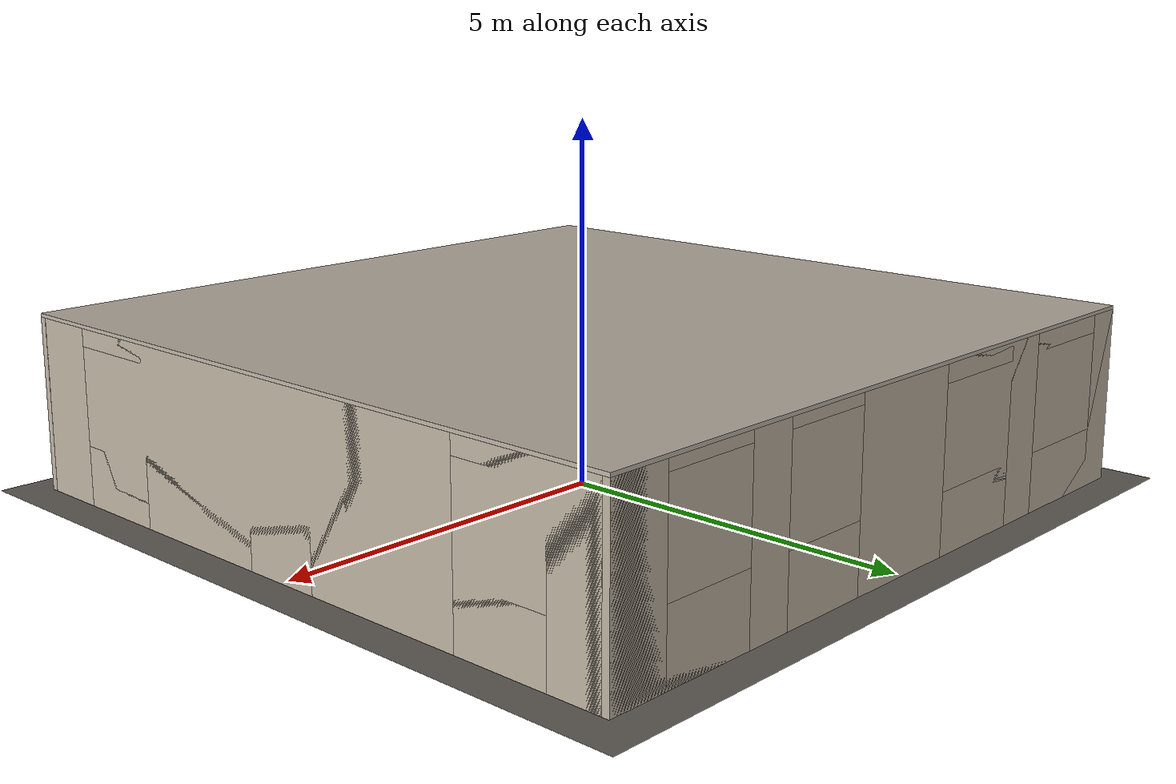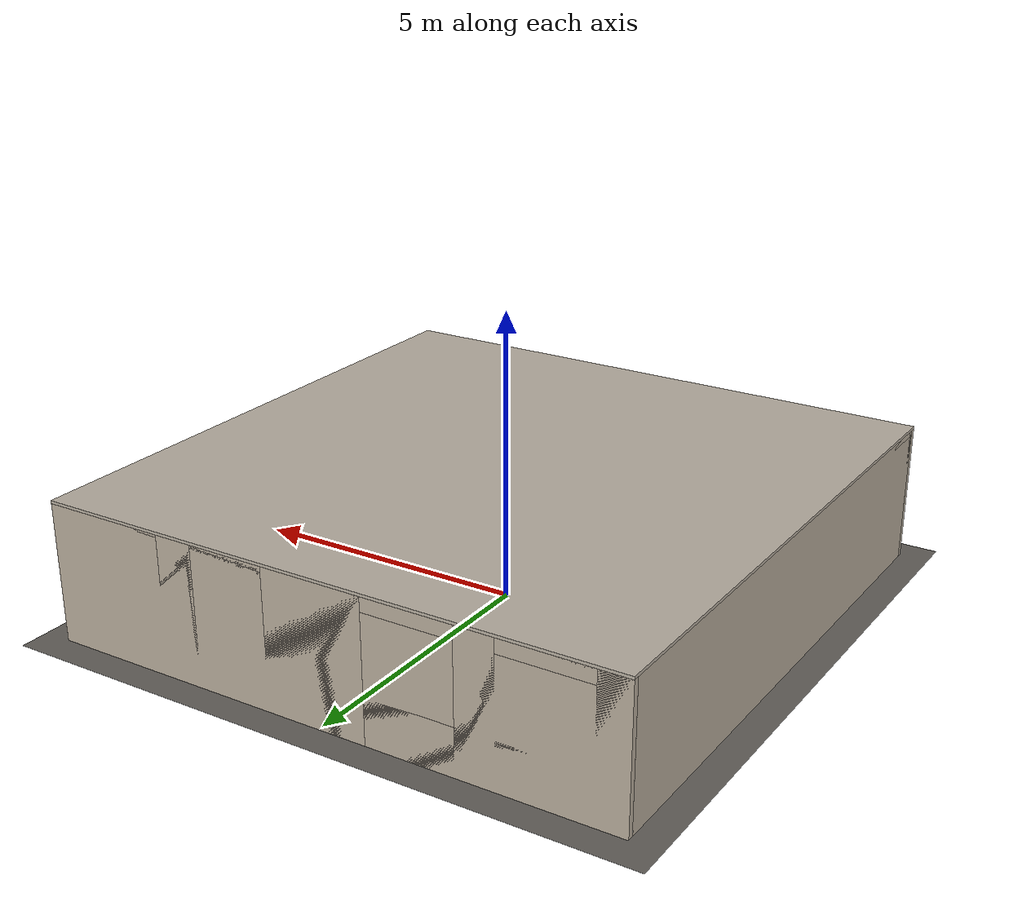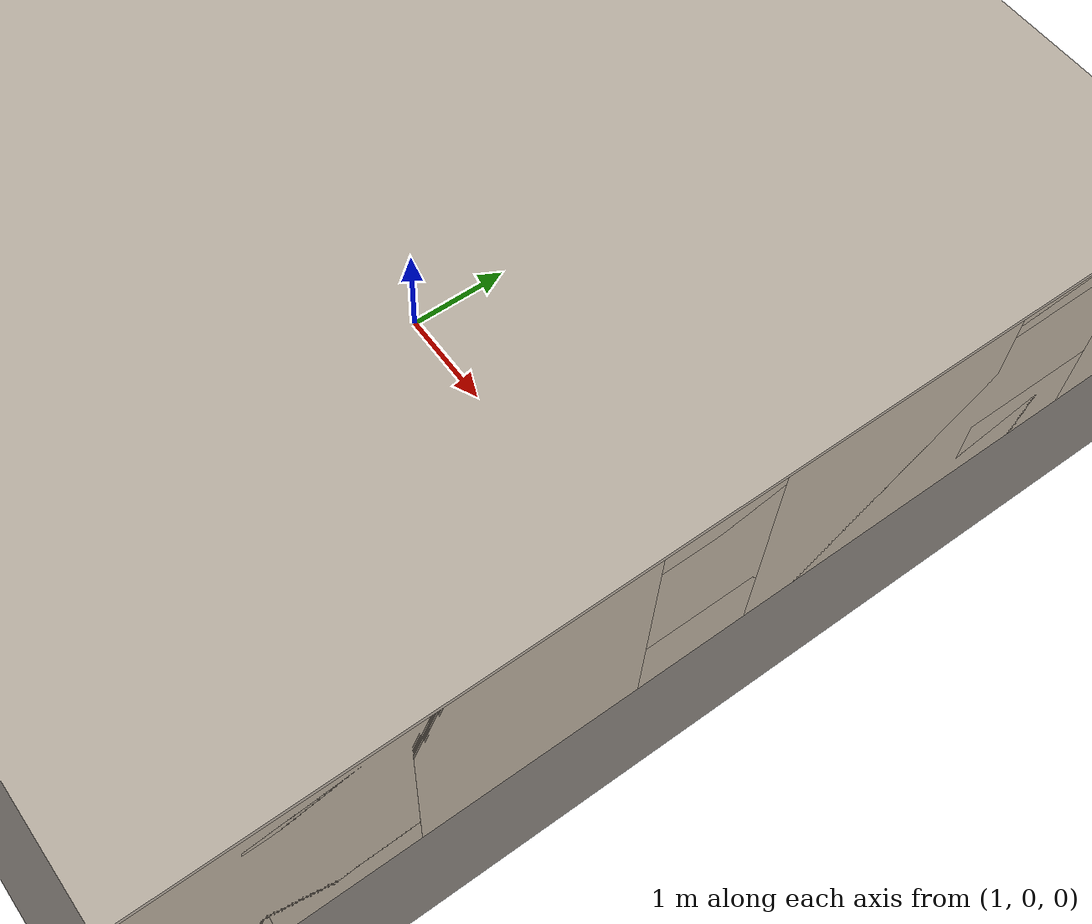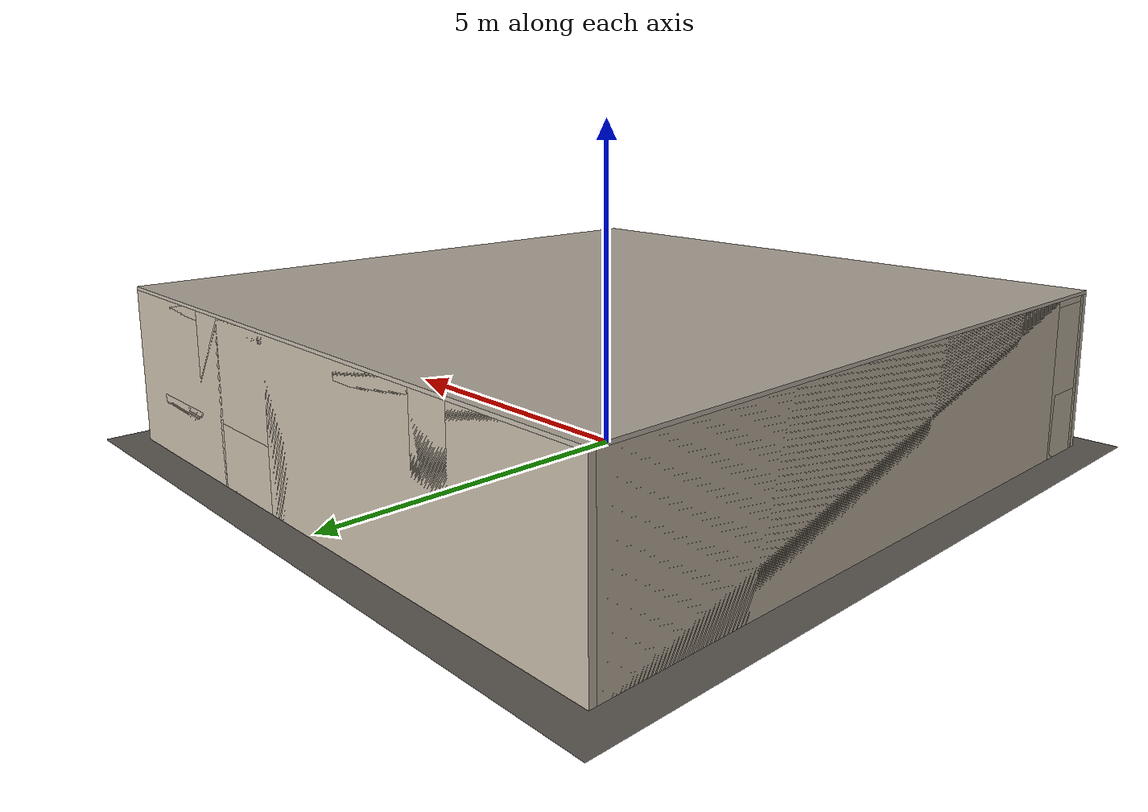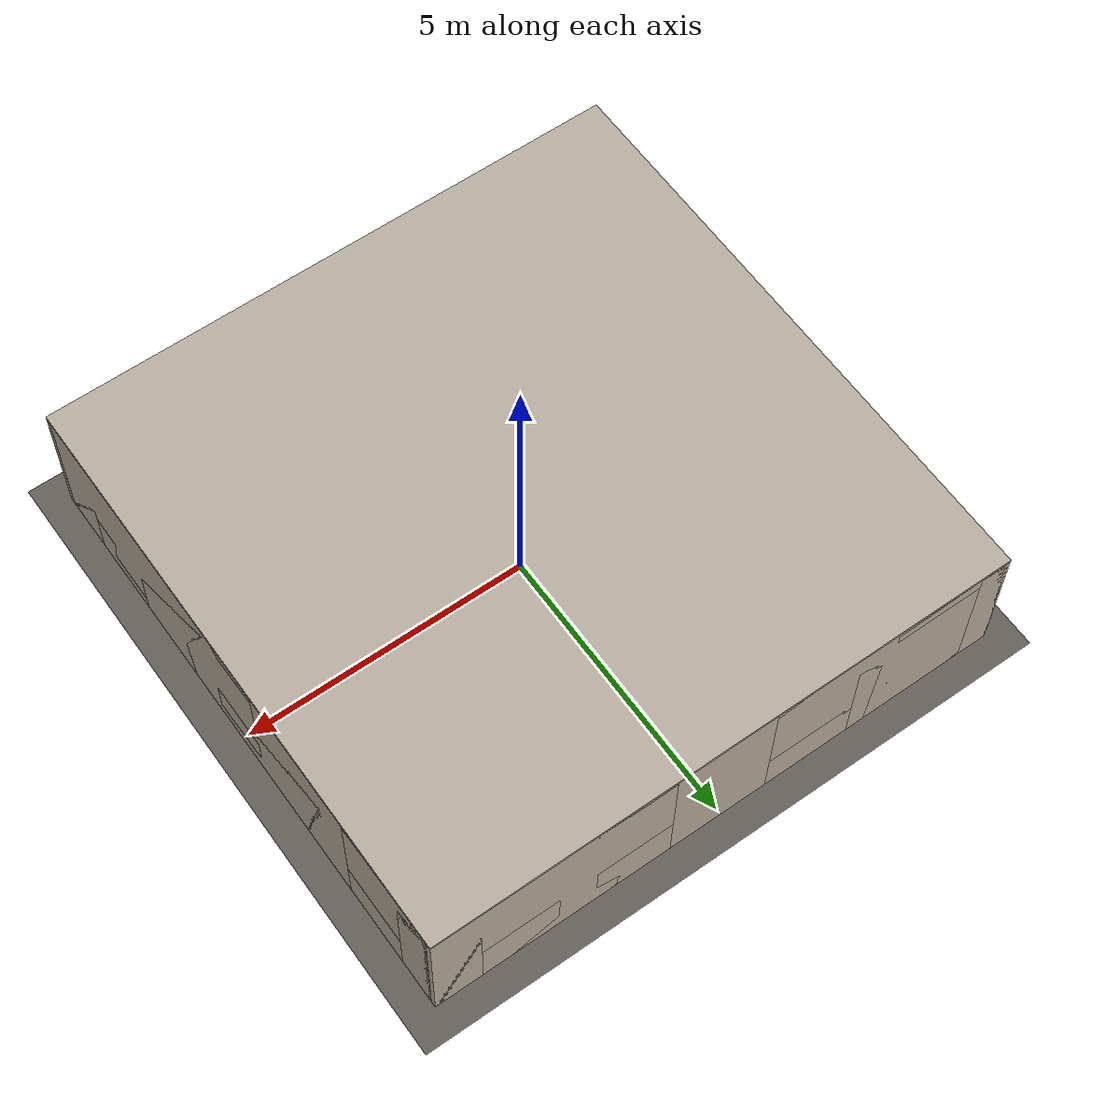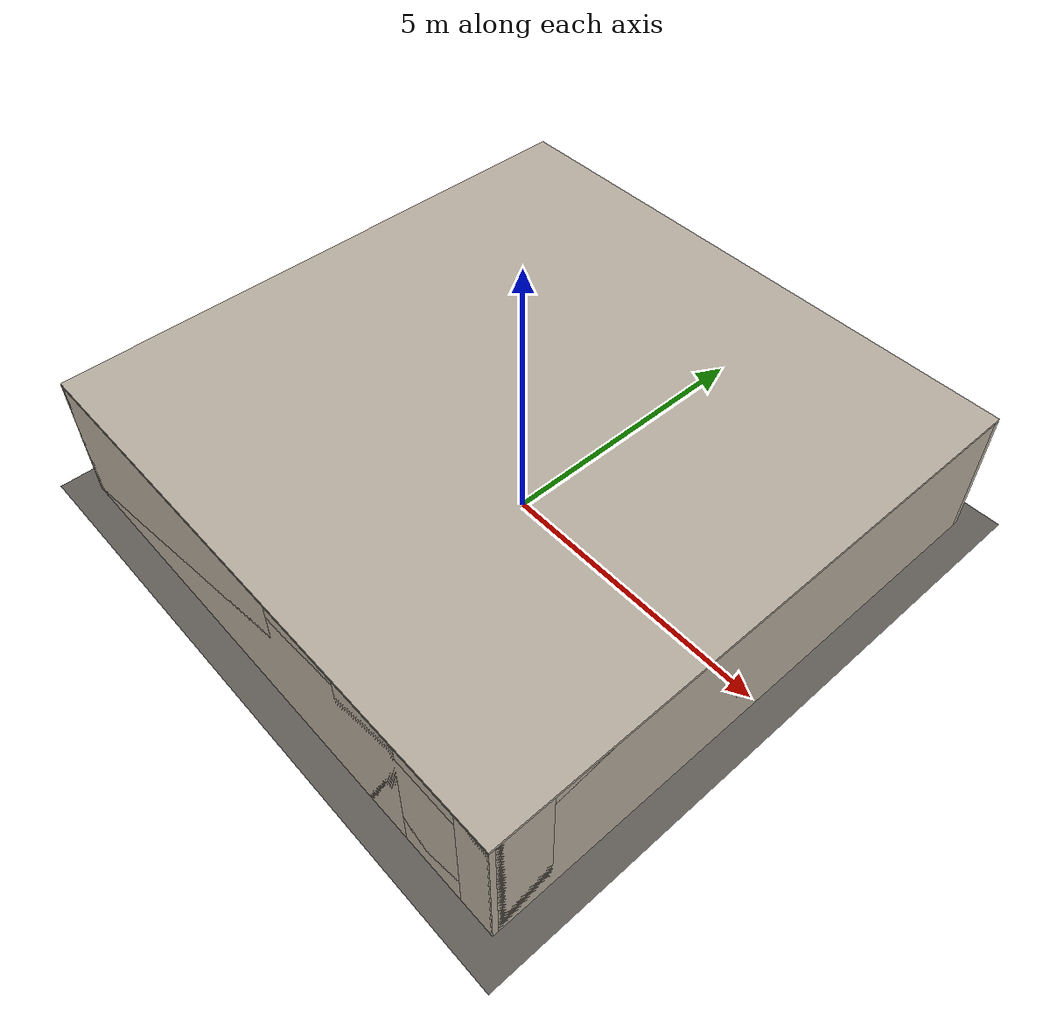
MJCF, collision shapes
<mujoco model="office_floor">
  <compiler angle="degree"/>
  <option timestep="0.0005" integrator="implicitfast" cone="elliptic" impratio="1"/>

  <visual>
    <global offwidth="2560" offheight="1440"/>
    <quality shadowsize="2048" offsamples="4"/>
    <headlight ambient="0.28 0.28 0.28" diffuse="0.03 0.03 0.03" specular="0.1 0.1 0.1"/>
    <!-- Clip planes are fractions of the model extent; znear keeps cameras from seeing
         through walls they are close to. -->
    <!-- fog (drawn where a view turns it on): a faint haze from 8 m to 40 m, in units of the
         model extent (20.6 m), so the corridor's far end softens as it does in a photograph -->
    <map znear="0.0005" zfar="3" shadowclip="1" shadowscale="1" fogstart="0.389" fogend="1.944"/>
    <rgba fog="0.6 0.6 0.6 1"/>
  </visual>

  <asset>
    <texture name="sky" type="skybox" builtin="flat" rgb1="0.86 0.87 0.88" rgb2="0.86 0.87 0.88" width="16" height="16"/>
    <texture name="wood_floor" type="2d" file="floor_wood.png"/>
    <texture name="tile" type="2d" file="floor_tile.png"/>
    <texture name="tile_dark" type="2d" file="floor_tile_dark.png"/>
    <texture name="carpet" type="2d" file="carpet.png"/>
    <texture name="plaster" type="2d" file="plaster.png"/>
    <texture name="door_wood" type="2d" file="door_wood.png"/>
    <!-- CC0 photo textures (tools/fetch_textures.py; sources and licences in assets/textures/*.json) -->
    <texture name="tx_plaster" type="2d" file="paint_roller.png"/>
    <texture name="tx_blind" type="2d" file="hessian_230.png"/>
    <texture name="tx_laminate" type="2d" file="laminate_floor_02.png"/>
    <texture name="tx_veneer" type="2d" file="white_oak_veneer.png"/>
    <texture name="tx_ceiling" type="2d" file="OfficeCeiling001.png"/>
    <texture name="tx_carpet" type="2d" file="Carpet012.png"/>
    <texture name="tx_porcelain" type="2d" file="Tiles040.png"/>
    <texture name="tx_concrete" type="2d" file="Concrete031.png"/>
    <texture name="sign_office" type="2d" file="label_office.png"/>
    <texture name="sign_lab" type="2d" file="label_lab.png"/>
    <texture name="sign_storage" type="2d" file="label_storage.png"/>
    <texture name="sign_reception" type="2d" file="label_reception.png"/>
    <texture name="rug_red" type="2d" file="rug_red.png"/>
    <texture name="rug_blue" type="2d" file="rug_blue.png"/>
    <!-- floors and walls at their real-world scales (texrepeat: repeats per metre) -->
    <!-- reflectance renders only on the first reflective geom in the model, the base plane (the lab and
         corridor floor); on every other material it does nothing under the classic renderer -->
    <material name="wood_floor" texture="tx_laminate" texrepeat="0.588 0.588" texuniform="true" emission="0" specular="0.3" shininess="0.3" reflectance="0.08" rgba="0.6 0.6 0.6 1"/>
    <material name="tile" texture="tx_porcelain" texrepeat="0.5 0.5" texuniform="true" specular="0.5" shininess="0.4" reflectance="0.22" rgba="0.52 0.52 0.52 1" emission="0"/>
    <material name="tile_dark" texture="tx_concrete" texrepeat="0.25 0.25" texuniform="true" emission="0" specular="0.2" shininess="0.2" reflectance="0.05" rgba="0.7 0.7 0.7 1"/>
    <material name="carpet" texture="tx_carpet" texrepeat="1 1" texuniform="true" emission="0" specular="0" shininess="0" rgba="0.6 0.6 0.6 1"/>
    <material name="plaster" texture="tx_plaster" texrepeat="1 1" texuniform="true" rgba="0.97 0.95 0.91 1" emission="0.33" specular="0.1" shininess="0.1"/>
    <material name="plaster_reveal" rgba="0.87 0.85 0.81 1" emission="0.33" specular="0.1" shininess="0.1"/>
    <material name="ceiling" texture="tx_ceiling" texrepeat="0.278 0.278" texuniform="true" rgba="0.97 0.96 0.94 1" emission="0.72"/>
    <material name="light_panel" rgba="1 0.98 0.92 1" emission="0.75"/>
    <material name="fitting_frame" rgba="0.95 0.95 0.94 1" emission="0.35" specular="0.3"/>
    <material name="skirting" rgba="1 1 0.98 1" emission="0.33" specular="0.25" shininess="0.5"/>
    <material name="skirting_bead" rgba="0.8 0.8 0.78 1" emission="0.3" specular="0.12" shininess="0.5"/>
    <material name="shadow_line" rgba="0.32 0.31 0.3 1" specular="0"/>
    <material name="threshold" rgba="0.72 0.73 0.74 1" emission="0.26" specular="0.8" shininess="0.7"/>
    <material name="kick_plate" rgba="0.62 0.63 0.65 1" emission="0.32" specular="0.9" shininess="0.8"/>
    <material name="kick_band" rgba="0.76 0.77 0.79 1" emission="0.36" specular="0.9" shininess="0.8"/>
    <material name="closer" rgba="0.62 0.63 0.65 1" emission="0.26" specular="0.6" shininess="0.6"/>
    <material name="frame" rgba="1 1 0.99 1" emission="0.3" specular="0.12" shininess="0.4"/>
    <material name="door" texture="tx_veneer" texrepeat="1 1" texuniform="false" specular="0.25" shininess="0.3"/>
    <material name="door_b" texture="tx_veneer" texrepeat="1.6 1" texuniform="false" specular="0.25" shininess="0.3"/>
    <material name="strike_plate" rgba="0.7 0.71 0.73 1" emission="0.26" specular="0.9" shininess="0.8"/>
    <material name="desk_wood" texture="door_wood" texrepeat="1 1" texuniform="true" specular="0.25"/>
    <material name="desk_body" rgba="0.55 0.56 0.58 1" specular="0.2"/>
    <material name="metal" rgba="0.62 0.64 0.67 1" specular="0.5" shininess="0.6"/>
    <material name="lab_white" rgba="0.9 0.91 0.92 1" specular="0.3"/>
    <material name="lab_top" rgba="0.24 0.26 0.28 1" specular="0.4"/>
    <material name="fabric" rgba="0.36 0.42 0.5 1"/>
    <material name="pot" rgba="0.82 0.8 0.76 1"/>
    <material name="leaves" rgba="0.2 0.42 0.2 1" specular="0.2"/>
    <material name="leaves_light" rgba="0.33 0.55 0.27 1" specular="0.2"/>
    <material name="stem" rgba="0.3 0.38 0.2 1"/>
    <material name="soil" rgba="0.25 0.18 0.12 1"/>
    <material name="metal_dark" rgba="0.36 0.38 0.41 1" specular="0.4"/>
    <material name="chair_base" rgba="0.12 0.12 0.13 1" specular="0.5" shininess="0.6"/>
    <material name="fabric_light" rgba="0.44 0.5 0.58 1"/>
    <material name="led_white" rgba="0.85 0.95 1 1" emission="1"/>
    <material name="sign_plate" rgba="0.72 0.73 0.74 1" specular="0.7" shininess="0.6"/>
    <material name="cardboard_dark" rgba="0.6 0.47 0.32 1"/>
    <material name="book_red" rgba="0.55 0.16 0.14 1"/>
    <material name="book_blue" rgba="0.16 0.26 0.46 1"/>
    <material name="book_green" rgba="0.16 0.36 0.24 1"/>
    <material name="book_cream" rgba="0.86 0.82 0.7 1"/>
    <material name="book_dark" rgba="0.14 0.14 0.16 1"/>
    <material name="cardboard" rgba="0.72 0.58 0.4 1"/>
    <material name="shelf_board" rgba="0.8 0.81 0.83 1" specular="0.4"/>
    <material name="bin_blue" rgba="0.25 0.4 0.62 1"/>
    <material name="bin_grey" rgba="0.5 0.52 0.55 1"/>
    <material name="seam" rgba="0.35 0.36 0.38 1"/>
    <material name="handle" rgba="0.7 0.71 0.73 1" emission="0.26" specular="0.8" shininess="0.7"/>
    <material name="window_frame" rgba="0.98 0.98 0.97 1" emission="0.27" specular="0.12" shininess="0.4"/>
    <material name="sill" rgba="0.8 0.8 0.79 1" emission="0.2" specular="0.08" shininess="0.45"/>
    <material name="blind" texture="tx_blind" texrepeat="14 14" texuniform="true" rgba="0.97 0.96 0.93 1" emission="0.56" specular="0"/>
    <material name="blind_rail" rgba="0.82 0.82 0.8 1" specular="0.5"/>
    <texture name="view_0" type="2d" file="view_0.png"/>
    <material name="view_0" texture="view_0" texuniform="false" emission="0.59" specular="0.3" shininess="0.9"/>
    <texture name="view_1" type="2d" file="view_1.png"/>
    <material name="view_1" texture="view_1" texuniform="false" emission="0.59" specular="0.3" shininess="0.9"/>
    <texture name="view_2" type="2d" file="view_2.png"/>
    <material name="view_2" texture="view_2" texuniform="false" emission="0.59" specular="0.3" shininess="0.9"/>
    <texture name="view_3" type="2d" file="view_3.png"/>
    <material name="view_3" texture="view_3" texuniform="false" emission="0.59" specular="0.3" shininess="0.9"/>
    <texture name="view_4" type="2d" file="view_4.png"/>
    <material name="view_4" texture="view_4" texuniform="false" emission="0.59" specular="0.3" shininess="0.9"/>
    <texture name="view_5" type="2d" file="view_5.png"/>
    <material name="view_5" texture="view_5" texuniform="false" emission="0.64" specular="0.3" shininess="0.9"/>
    <texture name="view_6" type="2d" file="view_6.png"/>
    <material name="view_6" texture="view_6" texuniform="false" emission="0.64" specular="0.3" shininess="0.9"/>
    <texture name="view_7" type="2d" file="view_7.png"/>
    <material name="view_7" texture="view_7" texuniform="false" emission="0.64" specular="0.3" shininess="0.9"/>
    <texture name="view_8" type="2d" file="view_8.png"/>
    <material name="view_8" texture="view_8" texuniform="false" emission="0.59" specular="0.3" shininess="0.9"/>
    <texture name="view_9" type="2d" file="view_9.png"/>
    <material name="view_9" texture="view_9" texuniform="false" emission="0.59" specular="0.3" shininess="0.9"/>
    <texture name="tx_rug_red" type="2d" file="rug_red_woven.png"/>
    <texture name="tx_rug_blue" type="2d" file="rug_blue_woven.png"/>
    <material name="rug_red" texture="tx_rug_red" emission="0" specular="0" shininess="0" rgba="0.7 0.7 0.7 1"/>
    <material name="rug_blue" texture="tx_rug_blue" emission="0" specular="0" shininess="0" rgba="0.7 0.7 0.7 1"/>
    <material name="rug_red_edge" rgba="0.119 0.028 0.025 1" specular="0"/>
    <material name="rug_blue_edge" rgba="0.028 0.042 0.091 1" specular="0"/>
    <material name="bin_dark" rgba="0.22 0.23 0.25 1" specular="0.3"/>
    <material name="pallet_wood" rgba="0.62 0.5 0.34 1"/>
    <material name="lamp_shade" rgba="0.96 0.92 0.82 1" emission="0.5"/>
    <material name="sign_office" texture="sign_office"/>
    <material name="sign_lab" texture="sign_lab"/>
    <material name="sign_storage" texture="sign_storage"/>
    <material name="sign_reception" texture="sign_reception"/>
    <material name="robot_body" rgba="0.2 0.21 0.23 1" specular="0.35" shininess="0.5"/>
    <material name="robot_cover" rgba="0.8 0.81 0.83 1" specular="0.4" shininess="0.6"/>
    <material name="robot_dark" rgba="0.08 0.08 0.09 1" specular="0.3"/>
    <material name="rubber" rgba="0.06 0.06 0.06 1" specular="0.05"/>
    <material name="hub" rgba="0.6 0.62 0.64 1" specular="0.7" shininess="0.8"/>
    <material name="lidar_window" rgba="0.1 0.25 0.3 1" specular="0.9" shininess="0.9"/>
    <material name="lens" rgba="0.05 0.1 0.2 1" specular="1" shininess="1"/>
    <material name="status_light" rgba="1 0.62 0.12 1" emission="0.9"/>
    <material name="robot_trim" rgba="0.32 0.33 0.36 1" specular="0.4" shininess="0.5"/>
    <material name="robot_panel" rgba="0.72 0.73 0.75 1" specular="0.3"/>
    <material name="vent" rgba="0.03 0.03 0.035 1"/>
    <material name="tire_wall" rgba="0.11 0.11 0.115 1" specular="0.08"/>
    <material name="tread" rgba="0.09 0.09 0.09 1" specular="0.02"/>
    <material name="lidar_body" rgba="0.1 0.1 0.11 1" specular="0.5" shininess="0.7"/>
    <material name="camera_body" rgba="0.14 0.14 0.15 1" specular="0.4"/>
    <texture name="metal_office_desk_t0" type="2d" file="metal_office_desk_0.png"/>
    <material name="metal_office_desk_m0" texture="metal_office_desk_t0" specular="0.367" shininess="0.538" reflectance="0.0"/>
    <mesh name="metal_office_desk_0" file="metal_office_desk_0.msh" inertia="shell"/>
    <material name="proc_desk_set_m0" rgba="0.050 0.050 0.050 1.000" specular="0.3" shininess="0.3" reflectance="0.0"/>
    <mesh name="proc_desk_set_0" file="proc_desk_set_0.msh" inertia="shell"/>
    <material name="proc_desk_set_m1" rgba="0.900 0.890 0.860 1.000" specular="0.55" shininess="0.7" reflectance="0.0"/>
    <mesh name="proc_desk_set_1" file="proc_desk_set_1.msh" inertia="shell"/>
    <material name="proc_desk_set_m2" rgba="0.160 0.090 0.050 1.000" specular="0.6" shininess="0.8" reflectance="0.0"/>
    <mesh name="proc_desk_set_2" file="proc_desk_set_2.msh" inertia="shell"/>
    <material name="proc_desk_set_m3" rgba="0.110 0.110 0.120 1.000" specular="0.3" shininess="0.35" reflectance="0.0"/>
    <mesh name="proc_desk_set_3" file="proc_desk_set_3.msh" inertia="shell"/>
    <texture name="proc_desk_set_t4" type="2d" file="proc_desk_set_4.png"/>
    <material name="proc_desk_set_m4" texture="proc_desk_set_t4" specular="0.25" shininess="0.3" reflectance="0.0"/>
    <mesh name="proc_desk_set_4" file="proc_desk_set_4.msh" inertia="shell"/>
    <material name="proc_desk_set_m5" rgba="0.070 0.070 0.075 1.000" specular="0.35" shininess="0.45" reflectance="0.0"/>
    <mesh name="proc_desk_set_5" file="proc_desk_set_5.msh" inertia="shell"/>
    <material name="proc_desk_set_m6" rgba="0.300 0.300 0.320 1.000" specular="0.6" shininess="0.6" reflectance="0.0"/>
    <mesh name="proc_desk_set_6" file="proc_desk_set_6.msh" inertia="shell"/>
    <material name="proc_desk_set_m7" rgba="0.160 0.160 0.170 1.000" specular="0.5" shininess="0.55" reflectance="0.0"/>
    <mesh name="proc_desk_set_7" file="proc_desk_set_7.msh" inertia="shell"/>
    <material name="proc_desk_set_m8" rgba="0.090 0.090 0.100 1.000" specular="0.45" shininess="0.6" reflectance="0.0"/>
    <mesh name="proc_desk_set_8" file="proc_desk_set_8.msh" inertia="shell"/>
    <material name="proc_desk_set_m9" rgba="0.120 0.130 0.150 1.000" specular="0.05" shininess="0.1" reflectance="0.0"/>
    <mesh name="proc_desk_set_9" file="proc_desk_set_9.msh" inertia="shell"/>
    <texture name="proc_desk_set_t10" type="2d" file="proc_desk_set_10.png"/>
    <material name="proc_desk_set_m10" texture="proc_desk_set_t10" specular="0.05" shininess="0.1" reflectance="0.0"/>
    <mesh name="proc_desk_set_10" file="proc_desk_set_10.msh" inertia="shell"/>
    <material name="proc_desk_set_m11" rgba="0.100 0.180 0.550 1.000" specular="0.5" shininess="0.6" reflectance="0.0"/>
    <mesh name="proc_desk_set_11" file="proc_desk_set_11.msh" inertia="shell"/>
    <material name="proc_desk_set_m12" rgba="0.050 0.100 0.350 1.000" specular="0.5" shininess="0.6" reflectance="0.0"/>
    <mesh name="proc_desk_set_12" file="proc_desk_set_12.msh" inertia="shell"/>
    <material name="proc_desk_set_m13" rgba="0.040 0.040 0.040 1.000" specular="0.6" shininess="0.6" reflectance="0.0"/>
    <mesh name="proc_desk_set_13" file="proc_desk_set_13.msh" inertia="shell"/>
    <texture name="proc_desk_set_t14" type="2d" file="proc_desk_set_14.png"/>
    <material name="proc_desk_set_m14" texture="proc_desk_set_t14" specular="0.7" shininess="0.9" reflectance="0.0"/>
    <mesh name="proc_desk_set_14" file="proc_desk_set_14.msh" inertia="shell"/>
    <material name="proc_office_chair_m0" rgba="0.720 0.730 0.750 1.000" specular="0.9" shininess="0.9" reflectance="0.15"/>
    <mesh name="proc_office_chair_0" file="proc_office_chair_0.msh" inertia="shell"/>
    <texture name="proc_office_chair_t1" type="2d" file="proc_office_chair_1.png"/>
    <material name="proc_office_chair_m1" texture="proc_office_chair_t1" specular="0.15" shininess="0.22" reflectance="0.0"/>
    <mesh name="proc_office_chair_1" file="proc_office_chair_1.msh" inertia="shell"/>
    <material name="proc_office_chair_m2" rgba="0.360 0.370 0.390 1.000" specular="0.15" shininess="0.22" reflectance="0.0"/>
    <mesh name="proc_office_chair_2" file="proc_office_chair_2.msh" inertia="shell"/>
    <texture name="proc_office_chair_t3" type="2d" file="proc_office_chair_3.png"/>
    <material name="proc_office_chair_m3" texture="proc_office_chair_t3" specular="0.35" shininess="0.4" reflectance="0.0"/>
    <mesh name="proc_office_chair_3" file="proc_office_chair_3.msh" inertia="shell"/>
    <texture name="proc_office_chair_t4" type="2d" file="proc_office_chair_4.png"/>
    <material name="proc_office_chair_m4" texture="proc_office_chair_t4" specular="0.3" shininess="0.3" reflectance="0.0"/>
    <mesh name="proc_office_chair_4" file="proc_office_chair_4.msh" inertia="shell"/>
    <material name="proc_shelf_feet_m0" rgba="0.720 0.730 0.750 1.000" specular="0.9" shininess="0.9" reflectance="0.15"/>
    <mesh name="proc_shelf_feet_0" file="proc_shelf_feet_0.msh" inertia="shell"/>
    <texture name="proc_shelf_feet_t1" type="2d" file="proc_shelf_feet_1.png"/>
    <material name="proc_shelf_feet_m1" texture="proc_shelf_feet_t1" specular="0.35" shininess="0.4" reflectance="0.0"/>
    <mesh name="proc_shelf_feet_1" file="proc_shelf_feet_1.msh" inertia="shell"/>
    <texture name="steel_frame_shelves_01_t0" type="2d" file="steel_frame_shelves_01_0.png"/>
    <material name="steel_frame_shelves_01_m0" texture="steel_frame_shelves_01_t0" specular="0.284" shininess="0.322" reflectance="0.0"/>
    <mesh name="steel_frame_shelves_01_0" file="steel_frame_shelves_01_0.msh" inertia="shell"/>
    <texture name="proc_shelf_books_11_t0" type="2d" file="proc_shelf_books_11_0.png"/>
    <material name="proc_shelf_books_11_m0" texture="proc_shelf_books_11_t0" specular="0.12" shininess="0.15" reflectance="0.0"/>
    <mesh name="proc_shelf_books_11_0" file="proc_shelf_books_11_0.msh" inertia="shell"/>
    <texture name="proc_shelf_books_11_t1" type="2d" file="proc_shelf_books_11_1.png"/>
    <material name="proc_shelf_books_11_m1" texture="proc_shelf_books_11_t1" specular="0.12" shininess="0.15" reflectance="0.0"/>
    <mesh name="proc_shelf_books_11_1" file="proc_shelf_books_11_1.msh" inertia="shell"/>
    <material name="proc_filing_cabinet_m0" rgba="0.720 0.730 0.750 1.000" specular="0.9" shininess="0.9" reflectance="0.15"/>
    <mesh name="proc_filing_cabinet_0" file="proc_filing_cabinet_0.msh" inertia="shell"/>
    <texture name="proc_filing_cabinet_t1" type="2d" file="proc_filing_cabinet_1.png"/>
    <material name="proc_filing_cabinet_m1" texture="proc_filing_cabinet_t1" specular="0.1" shininess="0.1" reflectance="0.0"/>
    <mesh name="proc_filing_cabinet_1" file="proc_filing_cabinet_1.msh" inertia="shell"/>
    <material name="proc_filing_cabinet_m2" rgba="0.030 0.030 0.030 1.000" specular="0.0" shininess="0.0" reflectance="0.0"/>
    <mesh name="proc_filing_cabinet_2" file="proc_filing_cabinet_2.msh" inertia="shell"/>
    <texture name="proc_filing_cabinet_t3" type="2d" file="proc_filing_cabinet_3.png"/>
    <material name="proc_filing_cabinet_m3" texture="proc_filing_cabinet_t3" specular="0.4" shininess="0.5" reflectance="0.02"/>
    <mesh name="proc_filing_cabinet_3" file="proc_filing_cabinet_3.msh" inertia="shell"/>
    <texture name="proc_filing_cabinet_t4" type="2d" file="proc_filing_cabinet_4.png"/>
    <material name="proc_filing_cabinet_m4" texture="proc_filing_cabinet_t4" specular="0.5" shininess="0.35" reflectance="0.02"/>
    <mesh name="proc_filing_cabinet_4" file="proc_filing_cabinet_4.msh" inertia="shell"/>
    <texture name="proc_plant_stand_t0" type="2d" file="proc_oak.png"/>
    <material name="proc_plant_stand_m0" texture="proc_plant_stand_t0" specular="0.2" shininess="0.25" reflectance="0.0"/>
    <mesh name="proc_plant_stand_0" file="proc_plant_stand_0.msh" inertia="shell"/>
    <material name="proc_plant_stand_m1" rgba="0.030 0.030 0.030 1.000" specular="0.0" shininess="0.0" reflectance="0.0"/>
    <mesh name="proc_plant_stand_1" file="proc_plant_stand_1.msh" inertia="shell"/>
    <texture name="proc_plant_stand_t2" type="2d" file="proc_plant_stand_2.png"/>
    <material name="proc_plant_stand_m2" texture="proc_plant_stand_t2" specular="0.4" shininess="0.5" reflectance="0.02"/>
    <mesh name="proc_plant_stand_2" file="proc_plant_stand_2.msh" inertia="shell"/>
    <texture name="potted_plant_01_t0" type="2d" file="potted_plant_01_0.png"/>
    <material name="potted_plant_01_m0" texture="potted_plant_01_t0" specular="0.0" shininess="0.0" reflectance="0.0"/>
    <mesh name="potted_plant_01_0" file="potted_plant_01_0.msh" inertia="shell"/>
    <texture name="potted_plant_01_t1" type="2d" file="potted_plant_01_1.png"/>
    <material name="potted_plant_01_m1" texture="potted_plant_01_t1" specular="0.0" shininess="0.0" reflectance="0.0"/>
    <mesh name="potted_plant_01_1" file="potted_plant_01_1.msh" inertia="shell"/>
    <material name="proc_wall_clock_m0" rgba="0.060 0.060 0.065 1.000" specular="0.45" shininess="0.55" reflectance="0.0"/>
    <mesh name="proc_wall_clock_0" file="proc_wall_clock_0.msh" inertia="shell"/>
    <texture name="proc_wall_clock_t1" type="2d" file="proc_wall_clock_1.png"/>
    <material name="proc_wall_clock_m1" texture="proc_wall_clock_t1" specular="0.15" shininess="0.2" reflectance="0.0"/>
    <mesh name="proc_wall_clock_1" file="proc_wall_clock_1.msh" inertia="shell"/>
    <material name="proc_wall_clock_m2" rgba="0.050 0.050 0.055 1.000" specular="0.3" shininess="0.4" reflectance="0.0"/>
    <mesh name="proc_wall_clock_2" file="proc_wall_clock_2.msh" inertia="shell"/>
    <material name="proc_wall_clock_m3" rgba="0.750 0.080 0.060 1.000" specular="0.3" shininess="0.4" reflectance="0.0"/>
    <mesh name="proc_wall_clock_3" file="proc_wall_clock_3.msh" inertia="shell"/>
    <material name="proc_lab_bench_long_m0" rgba="0.720 0.730 0.750 1.000" specular="0.9" shininess="0.9" reflectance="0.15"/>
    <mesh name="proc_lab_bench_long_0" file="proc_lab_bench_long_0.msh" inertia="shell"/>
    <texture name="proc_lab_bench_long_t1" type="2d" file="proc_lab_bench_long_1.png"/>
    <material name="proc_lab_bench_long_m1" texture="proc_lab_bench_long_t1" specular="0.3" shininess="0.3" reflectance="0.0"/>
    <mesh name="proc_lab_bench_long_1" file="proc_lab_bench_long_1.msh" inertia="shell"/>
    <texture name="proc_lab_bench_long_t2" type="2d" file="proc_lab_bench_long_2.png"/>
    <material name="proc_lab_bench_long_m2" texture="proc_lab_bench_long_t2" specular="0.2" shininess="0.3" reflectance="0.0"/>
    <mesh name="proc_lab_bench_long_2" file="proc_lab_bench_long_2.msh" inertia="shell"/>
    <material name="proc_lab_bench_long_m3" rgba="0.030 0.030 0.030 1.000" specular="0.0" shininess="0.0" reflectance="0.0"/>
    <mesh name="proc_lab_bench_long_3" file="proc_lab_bench_long_3.msh" inertia="shell"/>
    <texture name="proc_lab_bench_long_t4" type="2d" file="proc_lab_bench_long_4.png"/>
    <material name="proc_lab_bench_long_m4" texture="proc_lab_bench_long_t4" specular="0.4" shininess="0.45" reflectance="0.02"/>
    <mesh name="proc_lab_bench_long_4" file="proc_lab_bench_long_4.msh" inertia="shell"/>
    <texture name="proc_lab_bench_set_t0" type="2d" file="proc_lab_bench_set_0.png"/>
    <material name="proc_lab_bench_set_m0" texture="proc_lab_bench_set_t0" specular="0.4" shininess="0.5" reflectance="0.0" emission="0.5"/>
    <mesh name="proc_lab_bench_set_0" file="proc_lab_bench_set_0.msh" inertia="shell"/>
    <material name="proc_lab_bench_set_m1" rgba="0.820 0.900 0.950 0.320" specular="0.95" shininess="0.95" reflectance="0.0"/>
    <mesh name="proc_lab_bench_set_1" file="proc_lab_bench_set_1.msh" inertia="shell"/>
    <material name="proc_lab_bench_set_m2" rgba="0.070 0.070 0.080 1.000" specular="0.4" shininess="0.5" reflectance="0.0"/>
    <mesh name="proc_lab_bench_set_2" file="proc_lab_bench_set_2.msh" inertia="shell"/>
    <material name="proc_lab_bench_set_m3" rgba="0.900 0.900 0.880 1.000" specular="0.35" shininess="0.4" reflectance="0.0"/>
    <mesh name="proc_lab_bench_set_3" file="proc_lab_bench_set_3.msh" inertia="shell"/>
    <material name="proc_lab_bench_set_m4" rgba="0.700 0.710 0.730 1.000" specular="0.85" shininess="0.85" reflectance="0.08"/>
    <mesh name="proc_lab_bench_set_4" file="proc_lab_bench_set_4.msh" inertia="shell"/>
    <material name="proc_lab_bench_set_m5" rgba="0.850 0.550 0.150 0.700" specular="0.6" shininess="0.8" reflectance="0.0"/>
    <mesh name="proc_lab_bench_set_5" file="proc_lab_bench_set_5.msh" inertia="shell"/>
    <material name="proc_lab_bench_set_m6" rgba="0.200 0.450 0.850 0.700" specular="0.6" shininess="0.8" reflectance="0.0"/>
    <mesh name="proc_lab_bench_set_6" file="proc_lab_bench_set_6.msh" inertia="shell"/>
    <material name="proc_lab_bench_set_m7" rgba="0.850 0.850 0.820 1.000" specular="0.3" shininess="0.35" reflectance="0.0"/>
    <mesh name="proc_lab_bench_set_7" file="proc_lab_bench_set_7.msh" inertia="shell"/>
    <material name="proc_lab_bench_island_m0" rgba="0.720 0.730 0.750 1.000" specular="0.9" shininess="0.9" reflectance="0.15"/>
    <mesh name="proc_lab_bench_island_0" file="proc_lab_bench_island_0.msh" inertia="shell"/>
    <texture name="proc_lab_bench_island_t1" type="2d" file="proc_lab_bench_island_1.png"/>
    <material name="proc_lab_bench_island_m1" texture="proc_lab_bench_island_t1" specular="0.3" shininess="0.3" reflectance="0.0"/>
    <mesh name="proc_lab_bench_island_1" file="proc_lab_bench_island_1.msh" inertia="shell"/>
    <texture name="proc_lab_bench_island_t2" type="2d" file="proc_lab_bench_island_2.png"/>
    <material name="proc_lab_bench_island_m2" texture="proc_lab_bench_island_t2" specular="0.2" shininess="0.3" reflectance="0.0"/>
    <mesh name="proc_lab_bench_island_2" file="proc_lab_bench_island_2.msh" inertia="shell"/>
    <material name="proc_lab_bench_island_m3" rgba="0.030 0.030 0.030 1.000" specular="0.0" shininess="0.0" reflectance="0.0"/>
    <mesh name="proc_lab_bench_island_3" file="proc_lab_bench_island_3.msh" inertia="shell"/>
    <texture name="proc_lab_bench_island_t4" type="2d" file="proc_lab_bench_island_4.png"/>
    <material name="proc_lab_bench_island_m4" texture="proc_lab_bench_island_t4" specular="0.4" shininess="0.45" reflectance="0.02"/>
    <mesh name="proc_lab_bench_island_4" file="proc_lab_bench_island_4.msh" inertia="shell"/>
    <material name="proc_lab_island_set_m0" rgba="0.250 0.450 0.850 1.000" specular="0.25" shininess="0.35" reflectance="0.0"/>
    <mesh name="proc_lab_island_set_0" file="proc_lab_island_set_0.msh" inertia="shell"/>
    <texture name="proc_lab_island_set_t1" type="2d" file="proc_lab_island_set_1.png"/>
    <material name="proc_lab_island_set_m1" texture="proc_lab_island_set_t1" specular="0.15" shininess="0.2" reflectance="0.0"/>
    <mesh name="proc_lab_island_set_1" file="proc_lab_island_set_1.msh" inertia="shell"/>
    <texture name="proc_lab_island_set_t2" type="2d" file="proc_lab_island_set_2.png"/>
    <material name="proc_lab_island_set_m2" texture="proc_lab_island_set_t2" specular="0.05" shininess="0.1" reflectance="0.0"/>
    <mesh name="proc_lab_island_set_2" file="proc_lab_island_set_2.msh" inertia="shell"/>
    <texture name="proc_lab_rack_t0" type="2d" file="proc_lab_rack_0.png"/>
    <material name="proc_lab_rack_m0" texture="proc_lab_rack_t0" specular="0.1" shininess="0.15" reflectance="0.0"/>
    <mesh name="proc_lab_rack_0" file="proc_lab_rack_0.msh" inertia="shell"/>
    <texture name="proc_lab_rack_t1" type="2d" file="proc_lab_rack_1.png"/>
    <material name="proc_lab_rack_m1" texture="proc_lab_rack_t1" specular="0.4" shininess="0.5" reflectance="0.02"/>
    <mesh name="proc_lab_rack_1" file="proc_lab_rack_1.msh" inertia="shell"/>
    <texture name="proc_lab_rack_t2" type="2d" file="proc_lab_rack_2.png"/>
    <material name="proc_lab_rack_m2" texture="proc_lab_rack_t2" specular="0.5" shininess="0.35" reflectance="0.02"/>
    <mesh name="proc_lab_rack_2" file="proc_lab_rack_2.msh" inertia="shell"/>
    <material name="proc_lab_cabinet_m0" rgba="0.720 0.730 0.750 1.000" specular="0.9" shininess="0.9" reflectance="0.15"/>
    <mesh name="proc_lab_cabinet_0" file="proc_lab_cabinet_0.msh" inertia="shell"/>
    <texture name="proc_lab_cabinet_t1" type="2d" file="proc_lab_cabinet_1.png"/>
    <material name="proc_lab_cabinet_m1" texture="proc_lab_cabinet_t1" specular="0.3" shininess="0.3" reflectance="0.0"/>
    <mesh name="proc_lab_cabinet_1" file="proc_lab_cabinet_1.msh" inertia="shell"/>
    <texture name="proc_lab_cabinet_t2" type="2d" file="proc_lab_cabinet_2.png"/>
    <material name="proc_lab_cabinet_m2" texture="proc_lab_cabinet_t2" specular="0.2" shininess="0.3" reflectance="0.0"/>
    <mesh name="proc_lab_cabinet_2" file="proc_lab_cabinet_2.msh" inertia="shell"/>
    <material name="proc_lab_cabinet_m3" rgba="0.030 0.030 0.030 1.000" specular="0.0" shininess="0.0" reflectance="0.0"/>
    <mesh name="proc_lab_cabinet_3" file="proc_lab_cabinet_3.msh" inertia="shell"/>
    <texture name="proc_lab_cabinet_t4" type="2d" file="proc_lab_cabinet_4.png"/>
    <material name="proc_lab_cabinet_m4" texture="proc_lab_cabinet_t4" specular="0.4" shininess="0.45" reflectance="0.02"/>
    <mesh name="proc_lab_cabinet_4" file="proc_lab_cabinet_4.msh" inertia="shell"/>
    <texture name="proc_storage_rack_t0" type="2d" file="proc_storage_rack_0.png"/>
    <material name="proc_storage_rack_m0" texture="proc_storage_rack_t0" specular="0.1" shininess="0.15" reflectance="0.0"/>
    <mesh name="proc_storage_rack_0" file="proc_storage_rack_0.msh" inertia="shell"/>
    <texture name="proc_storage_rack_t1" type="2d" file="proc_storage_rack_1.png"/>
    <material name="proc_storage_rack_m1" texture="proc_storage_rack_t1" specular="0.45" shininess="0.4" reflectance="0.02"/>
    <mesh name="proc_storage_rack_1" file="proc_storage_rack_1.msh" inertia="shell"/>
    <texture name="proc_storage_rack_t2" type="2d" file="proc_storage_rack_2.png"/>
    <material name="proc_storage_rack_m2" texture="proc_storage_rack_t2" specular="0.45" shininess="0.4" reflectance="0.02"/>
    <mesh name="proc_storage_rack_2" file="proc_storage_rack_2.msh" inertia="shell"/>
    <texture name="proc_storage_rack_t3" type="2d" file="proc_storage_rack_3.png"/>
    <material name="proc_storage_rack_m3" texture="proc_storage_rack_t3" specular="0.4" shininess="0.5" reflectance="0.02"/>
    <mesh name="proc_storage_rack_3" file="proc_storage_rack_3.msh" inertia="shell"/>
    <texture name="proc_shelf_loads_t0" type="2d" file="proc_shelf_loads_0.png"/>
    <material name="proc_shelf_loads_m0" texture="proc_shelf_loads_t0" specular="0.06" shininess="0.1" reflectance="0.0"/>
    <mesh name="proc_shelf_loads_0" file="proc_shelf_loads_0.msh" inertia="shell"/>
    <material name="proc_shelf_loads_m1" rgba="0.180 0.420 0.780 1.000" specular="0.35" shininess="0.4" reflectance="0.0"/>
    <mesh name="proc_shelf_loads_1" file="proc_shelf_loads_1.msh" inertia="shell"/>
    <material name="proc_shelf_loads_m2" rgba="0.420 0.440 0.460 1.000" specular="0.35" shininess="0.4" reflectance="0.0"/>
    <mesh name="proc_shelf_loads_2" file="proc_shelf_loads_2.msh" inertia="shell"/>
    <material name="proc_shelf_loads_m3" rgba="0.040 0.040 0.050 1.000" specular="0.1" shininess="0.1" reflectance="0.0"/>
    <mesh name="proc_shelf_loads_3" file="proc_shelf_loads_3.msh" inertia="shell"/>
    <texture name="proc_storage_carton_t0" type="2d" file="proc_storage_carton_0.png"/>
    <material name="proc_storage_carton_m0" texture="proc_storage_carton_t0" specular="0.06" shininess="0.1" reflectance="0.0"/>
    <mesh name="proc_storage_carton_0" file="proc_storage_carton_0.msh" inertia="shell"/>
    <texture name="proc_storage_carton_top_t0" type="2d" file="proc_storage_carton_top_0.png"/>
    <material name="proc_storage_carton_top_m0" texture="proc_storage_carton_top_t0" specular="0.06" shininess="0.1" reflectance="0.0"/>
    <mesh name="proc_storage_carton_top_0" file="proc_storage_carton_top_0.msh" inertia="shell"/>
    <texture name="proc_reception_counter_t0" type="2d" file="proc_reception_counter_0.png"/>
    <material name="proc_reception_counter_m0" texture="proc_reception_counter_t0" specular="0.3" shininess="0.3" reflectance="0.0"/>
    <mesh name="proc_reception_counter_0" file="proc_reception_counter_0.msh" inertia="shell"/>
    <texture name="proc_reception_counter_t1" type="2d" file="proc_oak.png"/>
    <material name="proc_reception_counter_m1" texture="proc_reception_counter_t1" specular="0.2" shininess="0.25" reflectance="0.0"/>
    <mesh name="proc_reception_counter_1" file="proc_reception_counter_1.msh" inertia="shell"/>
    <texture name="proc_reception_counter_t2" type="2d" file="proc_reception_counter_2.png"/>
    <material name="proc_reception_counter_m2" texture="proc_reception_counter_t2" specular="0.2" shininess="0.3" reflectance="0.0"/>
    <mesh name="proc_reception_counter_2" file="proc_reception_counter_2.msh" inertia="shell"/>
    <texture name="proc_reception_counter_t3" type="2d" file="proc_reception_counter_3.png"/>
    <material name="proc_reception_counter_m3" texture="proc_reception_counter_t3" specular="0.35" shininess="0.4" reflectance="0.02"/>
    <mesh name="proc_reception_counter_3" file="proc_reception_counter_3.msh" inertia="shell"/>
    <material name="proc_reception_counter_m4" rgba="0.030 0.030 0.030 1.000" specular="0.0" shininess="0.0" reflectance="0.0"/>
    <mesh name="proc_reception_counter_4" file="proc_reception_counter_4.msh" inertia="shell"/>
    <material name="proc_sofa_m0" rgba="0.480 0.440 0.380 1.000" specular="0.1" shininess="0.2" reflectance="0.0"/>
    <mesh name="proc_sofa_0" file="proc_sofa_0.msh" inertia="shell"/>
    <texture name="proc_sofa_t1" type="2d" file="proc_sofa_1.png"/>
    <material name="proc_sofa_m1" texture="proc_sofa_t1" specular="0.2" shininess="0.3" reflectance="0.0"/>
    <mesh name="proc_sofa_1" file="proc_sofa_1.msh" inertia="shell"/>
    <texture name="proc_sofa_t2" type="2d" file="proc_sofa_2.png"/>
    <material name="proc_sofa_m2" texture="proc_sofa_t2" specular="0.1" shininess="0.2" reflectance="0.0"/>
    <mesh name="proc_sofa_2" file="proc_sofa_2.msh" inertia="shell"/>
    <texture name="proc_coffee_table_t0" type="2d" file="proc_oak.png"/>
    <material name="proc_coffee_table_m0" texture="proc_coffee_table_t0" specular="0.2" shininess="0.25" reflectance="0.0"/>
    <mesh name="proc_coffee_table_0" file="proc_coffee_table_0.msh" inertia="shell"/>
    <material name="proc_end_table_m0" rgba="0.720 0.560 0.300 1.000" specular="0.8" shininess="0.7" reflectance="0.1"/>
    <mesh name="proc_end_table_0" file="proc_end_table_0.msh" inertia="shell"/>
    <texture name="proc_end_table_t1" type="2d" file="proc_oak.png"/>
    <material name="proc_end_table_m1" texture="proc_end_table_t1" specular="0.2" shininess="0.25" reflectance="0.0"/>
    <mesh name="proc_end_table_1" file="proc_end_table_1.msh" inertia="shell"/>
    <material name="proc_end_table_m2" rgba="0.030 0.030 0.030 1.000" specular="0.0" shininess="0.0" reflectance="0.0"/>
    <mesh name="proc_end_table_2" file="proc_end_table_2.msh" inertia="shell"/>
    <texture name="proc_end_table_t3" type="2d" file="proc_end_table_3.png"/>
    <material name="proc_end_table_m3" texture="proc_end_table_t3" specular="0.4" shininess="0.5" reflectance="0.02"/>
    <mesh name="proc_end_table_3" file="proc_end_table_3.msh" inertia="shell"/>
    <material name="proc_armchair_m0" rgba="0.480 0.440 0.380 1.000" specular="0.1" shininess="0.2" reflectance="0.0"/>
    <mesh name="proc_armchair_0" file="proc_armchair_0.msh" inertia="shell"/>
    <texture name="proc_armchair_t1" type="2d" file="proc_armchair_1.png"/>
    <material name="proc_armchair_m1" texture="proc_armchair_t1" specular="0.2" shininess="0.3" reflectance="0.0"/>
    <mesh name="proc_armchair_1" file="proc_armchair_1.msh" inertia="shell"/>
    <texture name="proc_armchair_t2" type="2d" file="proc_armchair_2.png"/>
    <material name="proc_armchair_m2" texture="proc_armchair_t2" specular="0.1" shininess="0.2" reflectance="0.0"/>
    <mesh name="proc_armchair_2" file="proc_armchair_2.msh" inertia="shell"/>
    <material name="proc_ottoman_m0" rgba="0.480 0.440 0.380 1.000" specular="0.1" shininess="0.2" reflectance="0.0"/>
    <mesh name="proc_ottoman_0" file="proc_ottoman_0.msh" inertia="shell"/>
    <texture name="proc_ottoman_t1" type="2d" file="proc_ottoman_1.png"/>
    <material name="proc_ottoman_m1" texture="proc_ottoman_t1" specular="0.2" shininess="0.3" reflectance="0.0"/>
    <mesh name="proc_ottoman_1" file="proc_ottoman_1.msh" inertia="shell"/>
    <texture name="proc_ottoman_t2" type="2d" file="proc_ottoman_2.png"/>
    <material name="proc_ottoman_m2" texture="proc_ottoman_t2" specular="0.1" shininess="0.2" reflectance="0.0"/>
    <mesh name="proc_ottoman_2" file="proc_ottoman_2.msh" inertia="shell"/>
    <material name="proc_water_cooler_m0" rgba="0.550 0.720 0.920 0.380" specular="0.95" shininess="0.95" reflectance="0.0"/>
    <mesh name="proc_water_cooler_0" file="proc_water_cooler_0.msh" inertia="shell"/>
    <material name="proc_water_cooler_m1" rgba="0.150 0.400 0.800 1.000" specular="0.5" shininess="0.6" reflectance="0.0"/>
    <mesh name="proc_water_cooler_1" file="proc_water_cooler_1.msh" inertia="shell"/>
    <material name="proc_water_cooler_m2" rgba="0.300 0.310 0.330 1.000" specular="0.3" shininess="0.35" reflectance="0.0"/>
    <mesh name="proc_water_cooler_2" file="proc_water_cooler_2.msh" inertia="shell"/>
    <material name="proc_water_cooler_m3" rgba="0.800 0.150 0.120 1.000" specular="0.5" shininess="0.6" reflectance="0.0"/>
    <mesh name="proc_water_cooler_3" file="proc_water_cooler_3.msh" inertia="shell"/>
    <material name="proc_water_cooler_m4" rgba="0.350 0.600 0.900 0.300" specular="0.6" shininess="0.8" reflectance="0.0"/>
    <mesh name="proc_water_cooler_4" file="proc_water_cooler_4.msh" inertia="shell"/>
    <material name="proc_water_cooler_m5" rgba="0.920 0.920 0.900 1.000" specular="0.35" shininess="0.45" reflectance="0.0"/>
    <mesh name="proc_water_cooler_5" file="proc_water_cooler_5.msh" inertia="shell"/>
    <texture name="proc_snake_plant_t0" type="2d" file="proc_snake_plant_0.png"/>
    <material name="proc_snake_plant_m0" texture="proc_snake_plant_t0" specular="0.35" shininess="0.4" reflectance="0.02"/>
    <mesh name="proc_snake_plant_0" file="proc_snake_plant_0.msh" inertia="shell"/>
    <texture name="proc_snake_plant_t1" type="2d" file="proc_snake_plant_1.png"/>
    <material name="proc_snake_plant_m1" texture="proc_snake_plant_t1" specular="0.05" shininess="0.05" reflectance="0.0"/>
    <mesh name="proc_snake_plant_1" file="proc_snake_plant_1.msh" inertia="shell"/>
    <texture name="proc_snake_plant_t2" type="2d" file="proc_snake_plant_2.png"/>
    <material name="proc_snake_plant_m2" texture="proc_snake_plant_t2" specular="0.3" shininess="0.35" reflectance="0.0"/>
    <mesh name="proc_snake_plant_2" file="proc_snake_plant_2.msh" inertia="shell"/>
    <texture name="proc_waste_bin_t0" type="2d" file="proc_waste_bin_0.png"/>
    <material name="proc_waste_bin_m0" texture="proc_waste_bin_t0" specular="0.45" shininess="0.5" reflectance="0.02"/>
    <mesh name="proc_waste_bin_0" file="proc_waste_bin_0.msh" inertia="shell"/>
    <material name="proc_waste_bin_m1" rgba="0.720 0.730 0.750 1.000" specular="0.9" shininess="0.9" reflectance="0.15"/>
    <mesh name="proc_waste_bin_1" file="proc_waste_bin_1.msh" inertia="shell"/>
    <material name="proc_waste_bin_m2" rgba="0.035 0.035 0.040 1.000" specular="0.3" shininess="0.35" reflectance="0.0"/>
    <mesh name="proc_waste_bin_2" file="proc_waste_bin_2.msh" inertia="shell"/>
    <texture name="proc_waste_bin_t3" type="2d" file="proc_waste_bin_3.png"/>
    <material name="proc_waste_bin_m3" texture="proc_waste_bin_t3" specular="0.4" shininess="0.5" reflectance="0.02"/>
    <mesh name="proc_waste_bin_3" file="proc_waste_bin_3.msh" inertia="shell"/>
    <material name="proc_floor_lamp_m0" rgba="0.720 0.560 0.300 1.000" specular="0.8" shininess="0.7" reflectance="0.1"/>
    <mesh name="proc_floor_lamp_0" file="proc_floor_lamp_0.msh" inertia="shell"/>
    <material name="proc_floor_lamp_m1" rgba="0.720 0.730 0.750 1.000" specular="0.9" shininess="0.9" reflectance="0.15"/>
    <mesh name="proc_floor_lamp_1" file="proc_floor_lamp_1.msh" inertia="shell"/>
    <texture name="proc_floor_lamp_t2" type="2d" file="proc_floor_lamp_2.png"/>
    <material name="proc_floor_lamp_m2" texture="proc_floor_lamp_t2" specular="0.25" shininess="0.3" reflectance="0.0"/>
    <mesh name="proc_floor_lamp_2" file="proc_floor_lamp_2.msh" inertia="shell"/>
    <texture name="proc_floor_lamp_t3" type="2d" file="proc_floor_lamp_3.png"/>
    <material name="proc_floor_lamp_m3" texture="proc_floor_lamp_t3" specular="0.05" shininess="0.05" reflectance="0.0"/>
    <mesh name="proc_floor_lamp_3" file="proc_floor_lamp_3.msh" inertia="shell"/>
    <material name="proc_lab_stool_m0" rgba="0.720 0.730 0.750 1.000" specular="0.9" shininess="0.9" reflectance="0.15"/>
    <mesh name="proc_lab_stool_0" file="proc_lab_stool_0.msh" inertia="shell"/>
    <texture name="proc_lab_stool_t1" type="2d" file="proc_lab_stool_1.png"/>
    <material name="proc_lab_stool_m1" texture="proc_lab_stool_t1" specular="0.35" shininess="0.4" reflectance="0.0"/>
    <mesh name="proc_lab_stool_1" file="proc_lab_stool_1.msh" inertia="shell"/>
    <texture name="proc_lab_stool_t2" type="2d" file="proc_lab_stool_2.png"/>
    <material name="proc_lab_stool_m2" texture="proc_lab_stool_t2" specular="0.15" shininess="0.2" reflectance="0.0"/>
    <mesh name="proc_lab_stool_2" file="proc_lab_stool_2.msh" inertia="shell"/>
    <texture name="proc_lab_stool_t3" type="2d" file="proc_lab_stool_3.png"/>
    <material name="proc_lab_stool_m3" texture="proc_lab_stool_t3" specular="0.35" shininess="0.4" reflectance="0.0"/>
    <mesh name="proc_lab_stool_3" file="proc_lab_stool_3.msh" inertia="shell"/>
    <texture name="proc_storage_pallet_t0" type="2d" file="proc_storage_pallet_0.png"/>
    <material name="proc_storage_pallet_m0" texture="proc_storage_pallet_t0" specular="0.06" shininess="0.1" reflectance="0.0"/>
    <mesh name="proc_storage_pallet_0" file="proc_storage_pallet_0.msh" inertia="shell"/>
    <material name="proc_storage_pallet_m1" rgba="0.240 0.240 0.250 1.000" specular="0.4" shininess="0.4" reflectance="0.0"/>
    <mesh name="proc_storage_pallet_1" file="proc_storage_pallet_1.msh" inertia="shell"/>
    <texture name="proc_storage_pallet_t2" type="2d" file="proc_storage_pallet_2.png"/>
    <material name="proc_storage_pallet_m2" texture="proc_storage_pallet_t2" specular="0.08" shininess="0.12" reflectance="0.0"/>
    <mesh name="proc_storage_pallet_2" file="proc_storage_pallet_2.msh" inertia="shell"/>
    <texture name="proc_switch_t0" type="2d" file="proc_switch_0.png"/>
    <material name="proc_switch_m0" texture="proc_switch_t0" specular="0.3" shininess="0.35" reflectance="0.0"/>
    <mesh name="proc_switch_0" file="proc_switch_0.msh" inertia="shell"/>
    <texture name="proc_socket_t0" type="2d" file="proc_socket_0.png"/>
    <material name="proc_socket_m0" texture="proc_socket_t0" specular="0.3" shininess="0.35" reflectance="0.0"/>
    <mesh name="proc_socket_0" file="proc_socket_0.msh" inertia="shell"/>
    <texture name="proc_thermostat_t0" type="2d" file="proc_thermostat_0.png"/>
    <material name="proc_thermostat_m0" texture="proc_thermostat_t0" specular="0.3" shininess="0.35" reflectance="0.0"/>
    <mesh name="proc_thermostat_0" file="proc_thermostat_0.msh" inertia="shell"/>
    <texture name="proc_exit_sign_t0" type="2d" file="proc_exit_sign_0.png"/>
    <material name="proc_exit_sign_m0" texture="proc_exit_sign_t0" specular="0.3" shininess="0.35" reflectance="0.0" emission="0.25"/>
    <mesh name="proc_exit_sign_0" file="proc_exit_sign_0.msh" inertia="shell"/>
    <texture name="proc_notice_board_t0" type="2d" file="proc_notice_board_0.png"/>
    <material name="proc_notice_board_m0" texture="proc_notice_board_t0" specular="0.3" shininess="0.35" reflectance="0.0"/>
    <mesh name="proc_notice_board_0" file="proc_notice_board_0.msh" inertia="shell"/>
    <texture name="proc_first_aid_t0" type="2d" file="proc_first_aid_0.png"/>
    <material name="proc_first_aid_m0" texture="proc_first_aid_t0" specular="0.3" shininess="0.35" reflectance="0.0"/>
    <mesh name="proc_first_aid_0" file="proc_first_aid_0.msh" inertia="shell"/>
    <texture name="proc_safety_poster_t0" type="2d" file="proc_safety_poster_0.png"/>
    <material name="proc_safety_poster_m0" texture="proc_safety_poster_t0" specular="0.3" shininess="0.35" reflectance="0.0"/>
    <mesh name="proc_safety_poster_0" file="proc_safety_poster_0.msh" inertia="shell"/>
    <texture name="proc_trunking_t0" type="2d" file="proc_trunking_0.png"/>
    <material name="proc_trunking_m0" texture="proc_trunking_t0" specular="0.3" shininess="0.35" reflectance="0.0"/>
    <mesh name="proc_trunking_0" file="proc_trunking_0.msh" inertia="shell"/>
    <texture name="proc_smoke_detector_t0" type="2d" file="proc_smoke_detector_0.png"/>
    <material name="proc_smoke_detector_m0" texture="proc_smoke_detector_t0" specular="0.3" shininess="0.35" reflectance="0.0"/>
    <mesh name="proc_smoke_detector_0" file="proc_smoke_detector_0.msh" inertia="shell"/>
    <texture name="proc_print_a_t0" type="2d" file="proc_print_a_0.png"/>
    <material name="proc_print_a_m0" texture="proc_print_a_t0" specular="0.25" shininess="0.3" reflectance="0.0"/>
    <mesh name="proc_print_a_0" file="proc_print_a_0.msh" inertia="shell"/>
    <texture name="proc_print_a_t1" type="2d" file="proc_print_a_1.png"/>
    <material name="proc_print_a_m1" texture="proc_print_a_t1" specular="0.15" shininess="0.2" reflectance="0.0"/>
    <mesh name="proc_print_a_1" file="proc_print_a_1.msh" inertia="shell"/>
    <texture name="proc_print_b_t0" type="2d" file="proc_print_b_0.png"/>
    <material name="proc_print_b_m0" texture="proc_print_b_t0" specular="0.25" shininess="0.3" reflectance="0.0"/>
    <mesh name="proc_print_b_0" file="proc_print_b_0.msh" inertia="shell"/>
    <texture name="proc_print_b_t1" type="2d" file="proc_print_b_1.png"/>
    <material name="proc_print_b_m1" texture="proc_print_b_t1" specular="0.15" shininess="0.2" reflectance="0.0"/>
    <mesh name="proc_print_b_1" file="proc_print_b_1.msh" inertia="shell"/>
    <texture name="proc_print_c_t0" type="2d" file="proc_print_c_0.png"/>
    <material name="proc_print_c_m0" texture="proc_print_c_t0" specular="0.25" shininess="0.3" reflectance="0.0"/>
    <mesh name="proc_print_c_0" file="proc_print_c_0.msh" inertia="shell"/>
    <texture name="proc_print_c_t1" type="2d" file="proc_print_c_1.png"/>
    <material name="proc_print_c_m1" texture="proc_print_c_t1" specular="0.15" shininess="0.2" reflectance="0.0"/>
    <mesh name="proc_print_c_1" file="proc_print_c_1.msh" inertia="shell"/>
    <material name="proc_whiteboard_m0" rgba="0.620 0.630 0.640 1.000" specular="0.7" shininess="0.7" reflectance="0.02"/>
    <mesh name="proc_whiteboard_0" file="proc_whiteboard_0.msh" inertia="shell"/>
    <texture name="proc_whiteboard_t1" type="2d" file="proc_whiteboard_1.png"/>
    <material name="proc_whiteboard_m1" texture="proc_whiteboard_t1" specular="0.45" shininess="0.6" reflectance="0.0"/>
    <mesh name="proc_whiteboard_1" file="proc_whiteboard_1.msh" inertia="shell"/>
    <material name="proc_whiteboard_m2" rgba="0.200 0.200 0.210 1.000" specular="0.3" shininess="0.35" reflectance="0.0"/>
    <mesh name="proc_whiteboard_2" file="proc_whiteboard_2.msh" inertia="shell"/>
    <material name="proc_whiteboard_m3" rgba="0.250 0.420 0.700 1.000" specular="0.3" shininess="0.35" reflectance="0.0"/>
    <mesh name="proc_whiteboard_3" file="proc_whiteboard_3.msh" inertia="shell"/>
    <material name="proc_whiteboard_m4" rgba="0.180 0.180 0.200 1.000" specular="0.05" shininess="0.1" reflectance="0.0"/>
    <mesh name="proc_whiteboard_4" file="proc_whiteboard_4.msh" inertia="shell"/>
    <material name="proc_whiteboard_m5" rgba="0.060 0.060 0.070 1.000" specular="0.4" shininess="0.5" reflectance="0.0"/>
    <mesh name="proc_whiteboard_5" file="proc_whiteboard_5.msh" inertia="shell"/>
    <material name="proc_whiteboard_m6" rgba="0.020 0.020 0.020 1.000" specular="0.4" shininess="0.5" reflectance="0.0"/>
    <mesh name="proc_whiteboard_6" file="proc_whiteboard_6.msh" inertia="shell"/>
    <material name="proc_whiteboard_m7" rgba="0.100 0.220 0.600 1.000" specular="0.4" shininess="0.5" reflectance="0.0"/>
    <mesh name="proc_whiteboard_7" file="proc_whiteboard_7.msh" inertia="shell"/>
    <material name="proc_whiteboard_m8" rgba="0.050 0.120 0.380 1.000" specular="0.4" shininess="0.5" reflectance="0.0"/>
    <mesh name="proc_whiteboard_8" file="proc_whiteboard_8.msh" inertia="shell"/>
    <material name="proc_whiteboard_m9" rgba="0.700 0.100 0.080 1.000" specular="0.4" shininess="0.5" reflectance="0.0"/>
    <mesh name="proc_whiteboard_9" file="proc_whiteboard_9.msh" inertia="shell"/>
    <material name="proc_whiteboard_m10" rgba="0.450 0.050 0.040 1.000" specular="0.4" shininess="0.5" reflectance="0.0"/>
    <mesh name="proc_whiteboard_10" file="proc_whiteboard_10.msh" inertia="shell"/>
    <material name="proc_tv_m0" rgba="0.620 0.630 0.640 1.000" specular="0.8" shininess="0.8" reflectance="0.05"/>
    <mesh name="proc_tv_0" file="proc_tv_0.msh" inertia="shell"/>
    <material name="proc_tv_m1" rgba="0.300 0.300 0.320 1.000" specular="0.6" shininess="0.6" reflectance="0.0"/>
    <mesh name="proc_tv_1" file="proc_tv_1.msh" inertia="shell"/>
    <texture name="proc_tv_t2" type="2d" file="proc_tv_2.png"/>
    <material name="proc_tv_m2" texture="proc_tv_t2" specular="0.7" shininess="0.9" reflectance="0.0"/>
    <mesh name="proc_tv_2" file="proc_tv_2.msh" inertia="shell"/>
    <material name="proc_tv_m3" rgba="0.050 0.050 0.055 1.000" specular="0.4" shininess="0.5" reflectance="0.0"/>
    <mesh name="proc_tv_3" file="proc_tv_3.msh" inertia="shell"/>
    <material name="proc_extinguisher_m0" rgba="0.050 0.050 0.050 1.000" specular="0.4" shininess="0.45" reflectance="0.0"/>
    <mesh name="proc_extinguisher_0" file="proc_extinguisher_0.msh" inertia="shell"/>
    <texture name="proc_extinguisher_t1" type="2d" file="proc_extinguisher_1.png"/>
    <material name="proc_extinguisher_m1" texture="proc_extinguisher_t1" specular="0.2" shininess="0.3" reflectance="0.0"/>
    <mesh name="proc_extinguisher_1" file="proc_extinguisher_1.msh" inertia="shell"/>
    <material name="proc_extinguisher_m2" rgba="0.720 0.060 0.050 1.000" specular="0.6" shininess="0.7" reflectance="0.0"/>
    <mesh name="proc_extinguisher_2" file="proc_extinguisher_2.msh" inertia="shell"/>
    <material name="proc_extinguisher_m3" rgba="0.620 0.630 0.640 1.000" specular="0.8" shininess="0.8" reflectance="0.05"/>
    <mesh name="proc_extinguisher_3" file="proc_extinguisher_3.msh" inertia="shell"/>
    <texture name="proc_fire_sign_t0" type="2d" file="proc_fire_sign_0.png"/>
    <material name="proc_fire_sign_m0" texture="proc_fire_sign_t0" specular="0.3" shininess="0.35" reflectance="0.0"/>
    <mesh name="proc_fire_sign_0" file="proc_fire_sign_0.msh" inertia="shell"/>
    <texture name="proc_call_point_t0" type="2d" file="proc_call_point_0.png"/>
    <material name="proc_call_point_m0" texture="proc_call_point_t0" specular="0.3" shininess="0.35" reflectance="0.0"/>
    <mesh name="proc_call_point_0" file="proc_call_point_0.msh" inertia="shell"/>
    <material name="proc_dome_camera_m0" rgba="0.120 0.120 0.130 1.000" specular="0.8" shininess="0.9" reflectance="0.0"/>
    <mesh name="proc_dome_camera_0" file="proc_dome_camera_0.msh" inertia="shell"/>
    <texture name="proc_dome_camera_t1" type="2d" file="proc_dome_camera_1.png"/>
    <material name="proc_dome_camera_m1" texture="proc_dome_camera_t1" specular="0.3" shininess="0.35" reflectance="0.0"/>
    <mesh name="proc_dome_camera_1" file="proc_dome_camera_1.msh" inertia="shell"/>
  </asset>

  <default>
    <default class="visual">
      <geom contype="0" conaffinity="0" group="2" mass="0"/>
    </default>
    <default class="ceiling">
      <geom contype="0" conaffinity="0" group="3" mass="0"/>
    </default>
  </default>

  <worldbody>

    <!-- Base floor (physics). Room floors on top are visual only. -->
    <geom name="floor" type="plane" size="5.6 5.6 0.1" material="tile"/>
    <geom name="floor_office" type="box" pos="-2.5250 2.9000 0.0006" size="2.4750 2.1000 0.0005" material="carpet" class="visual"/>
    <geom name="floor_storage" type="box" pos="-2.5250 -2.9000 0.0006" size="2.4750 2.1000 0.0005" material="tile_dark" class="visual"/>
    <geom name="floor_reception" type="box" pos="2.5250 -2.9000 0.0006" size="2.4750 2.1000 0.0005" material="wood_floor" class="visual"/>

    <!-- Outer walls (inner faces at +/-5 m) -->
    <geom name="wall_north_0" type="box" pos="0.0000 5.0500 1.2000" size="5.1000 0.0500 1.2000" material="plaster" group="4"/>
    <geom type="box" pos="-4.8350 5.0500 1.2000" size="0.2650 0.0500 1.2000" material="plaster" class="visual"/>
    <geom class="visual" type="box" pos="-4.8350 4.9990 1.2000" size="0.2650 1.2000 0.0005" xyaxes="1 0 0 0 0 1" material="plaster"/>
    <geom type="box" pos="-3.8000 5.0500 0.4100" size="0.7700 0.0500 0.4100" material="plaster" class="visual"/>
    <geom class="visual" type="box" pos="-3.8000 4.9990 0.4100" size="0.7700 0.4100 0.0005" xyaxes="1 0 0 0 0 1" material="plaster"/>
    <geom type="box" pos="-3.8000 5.0500 2.2800" size="0.7700 0.0500 0.1200" material="plaster" class="visual"/>
    <geom class="visual" type="box" pos="-3.8000 4.9990 2.2800" size="0.7700 0.1200 0.0005" xyaxes="1 0 0 0 0 1" material="plaster"/>
    <geom type="box" pos="-2.7000 5.0500 1.2000" size="0.3300 0.0500 1.2000" material="plaster" class="visual"/>
    <geom class="visual" type="box" pos="-2.7000 4.9990 1.2000" size="0.3300 1.2000 0.0005" xyaxes="1 0 0 0 0 1" material="plaster"/>
    <geom type="box" pos="-1.6000 5.0500 0.4100" size="0.7700 0.0500 0.4100" material="plaster" class="visual"/>
    <geom class="visual" type="box" pos="-1.6000 4.9990 0.4100" size="0.7700 0.4100 0.0005" xyaxes="1 0 0 0 0 1" material="plaster"/>
    <geom type="box" pos="-1.6000 5.0500 2.2800" size="0.7700 0.0500 0.1200" material="plaster" class="visual"/>
    <geom class="visual" type="box" pos="-1.6000 4.9990 2.2800" size="0.7700 0.1200 0.0005" xyaxes="1 0 0 0 0 1" material="plaster"/>
    <geom type="box" pos="0.0500 5.0500 1.2000" size="0.8800 0.0500 1.2000" material="plaster" class="visual"/>
    <geom class="visual" type="box" pos="0.0500 4.9990 1.2000" size="0.8800 1.2000 0.0005" xyaxes="1 0 0 0 0 1" material="plaster"/>
    <geom type="box" pos="1.6000 5.0500 0.4600" size="0.6700 0.0500 0.4600" material="plaster" class="visual"/>
    <geom class="visual" type="box" pos="1.6000 4.9990 0.4600" size="0.6700 0.4600 0.0005" xyaxes="1 0 0 0 0 1" material="plaster"/>
    <geom type="box" pos="1.6000 5.0500 2.3300" size="0.6700 0.0500 0.0700" material="plaster" class="visual"/>
    <geom class="visual" type="box" pos="1.6000 4.9990 2.3300" size="0.6700 0.0700 0.0005" xyaxes="1 0 0 0 0 1" material="plaster"/>
    <geom type="box" pos="2.6000 5.0500 1.2000" size="0.3300 0.0500 1.2000" material="plaster" class="visual"/>
    <geom class="visual" type="box" pos="2.6000 4.9990 1.2000" size="0.3300 1.2000 0.0005" xyaxes="1 0 0 0 0 1" material="plaster"/>
    <geom type="box" pos="3.6000 5.0500 0.4600" size="0.6700 0.0500 0.4600" material="plaster" class="visual"/>
    <geom class="visual" type="box" pos="3.6000 4.9990 0.4600" size="0.6700 0.4600 0.0005" xyaxes="1 0 0 0 0 1" material="plaster"/>
    <geom type="box" pos="3.6000 5.0500 2.3300" size="0.6700 0.0500 0.0700" material="plaster" class="visual"/>
    <geom class="visual" type="box" pos="3.6000 4.9990 2.3300" size="0.6700 0.0700 0.0005" xyaxes="1 0 0 0 0 1" material="plaster"/>
    <geom type="box" pos="4.6850 5.0500 1.2000" size="0.4150 0.0500 1.2000" material="plaster" class="visual"/>
    <geom class="visual" type="box" pos="4.6850 4.9990 1.2000" size="0.4150 1.2000 0.0005" xyaxes="1 0 0 0 0 1" material="plaster"/>
    <geom type="box" pos="0.0000 4.9940 0.0400" size="5.1000 0.0060 0.0400" material="skirting"/>
    <geom type="box" pos="0.0000 4.9950 0.0900" size="5.1000 0.0050 0.0100" material="skirting_bead" class="visual"/>
    <geom type="box" pos="0.0000 4.9982 0.1015" size="5.1000 0.0015 0.0015" material="shadow_line" class="visual"/>
    <geom name="wall_south_0" type="box" pos="0.0000 -5.0500 1.2000" size="5.1000 0.0500 1.2000" material="plaster" group="4"/>
    <geom type="box" pos="-2.2850 -5.0500 1.2000" size="2.8150 0.0500 1.2000" material="plaster" class="visual"/>
    <geom class="visual" type="box" pos="-2.2850 -4.9990 1.2000" size="2.8150 1.2000 0.0005" xyaxes="-1 0 0 0 0 1" material="plaster"/>
    <geom type="box" pos="1.3000 -5.0500 0.4100" size="0.7700 0.0500 0.4100" material="plaster" class="visual"/>
    <geom class="visual" type="box" pos="1.3000 -4.9990 0.4100" size="0.7700 0.4100 0.0005" xyaxes="-1 0 0 0 0 1" material="plaster"/>
    <geom type="box" pos="1.3000 -5.0500 2.2800" size="0.7700 0.0500 0.1200" material="plaster" class="visual"/>
    <geom class="visual" type="box" pos="1.3000 -4.9990 2.2800" size="0.7700 0.1200 0.0005" xyaxes="-1 0 0 0 0 1" material="plaster"/>
    <geom type="box" pos="2.7000 -5.0500 1.2000" size="0.6300 0.0500 1.2000" material="plaster" class="visual"/>
    <geom class="visual" type="box" pos="2.7000 -4.9990 1.2000" size="0.6300 1.2000 0.0005" xyaxes="-1 0 0 0 0 1" material="plaster"/>
    <geom type="box" pos="3.9000 -5.0500 0.4100" size="0.5700 0.0500 0.4100" material="plaster" class="visual"/>
    <geom class="visual" type="box" pos="3.9000 -4.9990 0.4100" size="0.5700 0.4100 0.0005" xyaxes="-1 0 0 0 0 1" material="plaster"/>
    <geom type="box" pos="3.9000 -5.0500 2.2800" size="0.5700 0.0500 0.1200" material="plaster" class="visual"/>
    <geom class="visual" type="box" pos="3.9000 -4.9990 2.2800" size="0.5700 0.1200 0.0005" xyaxes="-1 0 0 0 0 1" material="plaster"/>
    <geom type="box" pos="4.7850 -5.0500 1.2000" size="0.3150 0.0500 1.2000" material="plaster" class="visual"/>
    <geom class="visual" type="box" pos="4.7850 -4.9990 1.2000" size="0.3150 1.2000 0.0005" xyaxes="-1 0 0 0 0 1" material="plaster"/>
    <geom type="box" pos="0.0000 -4.9940 0.0400" size="5.1000 0.0060 0.0400" material="skirting"/>
    <geom type="box" pos="0.0000 -4.9950 0.0900" size="5.1000 0.0050 0.0100" material="skirting_bead" class="visual"/>
    <geom type="box" pos="0.0000 -4.9982 0.1015" size="5.1000 0.0015 0.0015" material="shadow_line" class="visual"/>
    <geom name="wall_east_0" type="box" pos="5.0500 0.0000 1.2000" size="0.0500 5.0000 1.2000" material="plaster" group="4"/>
    <geom type="box" pos="5.0500 -4.5350 1.2000" size="0.0500 0.4650 1.2000" material="plaster" class="visual"/>
    <geom class="visual" type="box" pos="4.9990 -4.5350 1.2000" size="0.4650 1.2000 0.0005" xyaxes="0 -1 0 0 0 1" material="plaster"/>
    <geom type="box" pos="5.0500 -3.4000 0.4100" size="0.0500 0.6700 0.4100" material="plaster" class="visual"/>
    <geom class="visual" type="box" pos="4.9990 -3.4000 0.4100" size="0.6700 0.4100 0.0005" xyaxes="0 -1 0 0 0 1" material="plaster"/>
    <geom type="box" pos="5.0500 -3.4000 2.2800" size="0.0500 0.6700 0.1200" material="plaster" class="visual"/>
    <geom class="visual" type="box" pos="4.9990 -3.4000 2.2800" size="0.6700 0.1200 0.0005" xyaxes="0 -1 0 0 0 1" material="plaster"/>
    <geom type="box" pos="5.0500 -1.6500 1.2000" size="0.0500 1.0800 1.2000" material="plaster" class="visual"/>
    <geom class="visual" type="box" pos="4.9990 -1.6500 1.2000" size="1.0800 1.2000 0.0005" xyaxes="0 -1 0 0 0 1" material="plaster"/>
    <geom type="box" pos="5.0500 0.0000 0.4100" size="0.0500 0.5700 0.4100" material="plaster" class="visual"/>
    <geom class="visual" type="box" pos="4.9990 0.0000 0.4100" size="0.5700 0.4100 0.0005" xyaxes="0 -1 0 0 0 1" material="plaster"/>
    <geom type="box" pos="5.0500 0.0000 2.2800" size="0.0500 0.5700 0.1200" material="plaster" class="visual"/>
    <geom class="visual" type="box" pos="4.9990 0.0000 2.2800" size="0.5700 0.1200 0.0005" xyaxes="0 -1 0 0 0 1" material="plaster"/>
    <geom type="box" pos="5.0500 1.7500 1.2000" size="0.0500 1.1800 1.2000" material="plaster" class="visual"/>
    <geom class="visual" type="box" pos="4.9990 1.7500 1.2000" size="1.1800 1.2000 0.0005" xyaxes="0 -1 0 0 0 1" material="plaster"/>
    <geom type="box" pos="5.0500 3.6000 0.4100" size="0.0500 0.6700 0.4100" material="plaster" class="visual"/>
    <geom class="visual" type="box" pos="4.9990 3.6000 0.4100" size="0.6700 0.4100 0.0005" xyaxes="0 -1 0 0 0 1" material="plaster"/>
    <geom type="box" pos="5.0500 3.6000 2.2800" size="0.0500 0.6700 0.1200" material="plaster" class="visual"/>
    <geom class="visual" type="box" pos="4.9990 3.6000 2.2800" size="0.6700 0.1200 0.0005" xyaxes="0 -1 0 0 0 1" material="plaster"/>
    <geom type="box" pos="5.0500 4.6350 1.2000" size="0.0500 0.3650 1.2000" material="plaster" class="visual"/>
    <geom class="visual" type="box" pos="4.9990 4.6350 1.2000" size="0.3650 1.2000 0.0005" xyaxes="0 -1 0 0 0 1" material="plaster"/>
    <geom type="box" pos="4.9940 0.0000 0.0400" size="0.0060 5.0000 0.0400" material="skirting"/>
    <geom type="box" pos="4.9950 0.0000 0.0900" size="0.0050 5.0000 0.0100" material="skirting_bead" class="visual"/>
    <geom type="box" pos="4.9982 0.0000 0.1015" size="0.0015 5.0000 0.0015" material="shadow_line" class="visual"/>
    <geom name="wall_west_0" type="box" pos="-5.0500 0.0000 1.2000" size="0.0500 5.0000 1.2000" material="plaster" group="4"/>
    <geom type="box" pos="-5.0500 -4.9600 1.2000" size="0.0500 0.0400 1.2000" material="plaster" class="visual"/>
    <geom class="visual" type="box" pos="-4.9990 -4.9600 1.2000" size="0.0400 1.2000 0.0005" xyaxes="0 1 0 0 0 1" material="plaster"/>
    <geom type="box" pos="-5.0500 -4.5500 0.4850" size="0.0500 0.3700 0.4850" material="plaster" class="visual"/>
    <geom class="visual" type="box" pos="-4.9990 -4.5500 0.4850" size="0.3700 0.4850 0.0005" xyaxes="0 1 0 0 0 1" material="plaster"/>
    <geom type="box" pos="-5.0500 -4.5500 2.3550" size="0.0500 0.3700 0.0450" material="plaster" class="visual"/>
    <geom class="visual" type="box" pos="-4.9990 -4.5500 2.3550" size="0.3700 0.0450 0.0005" xyaxes="0 1 0 0 0 1" material="plaster"/>
    <geom type="box" pos="-5.0500 0.4100 1.2000" size="0.0500 4.5900 1.2000" material="plaster" class="visual"/>
    <geom class="visual" type="box" pos="-4.9990 0.4100 1.2000" size="4.5900 1.2000 0.0005" xyaxes="0 1 0 0 0 1" material="plaster"/>
    <geom type="box" pos="-4.9940 0.0000 0.0400" size="0.0060 5.0000 0.0400" material="skirting"/>
    <geom type="box" pos="-4.9950 0.0000 0.0900" size="0.0050 5.0000 0.0100" material="skirting_bead" class="visual"/>
    <geom type="box" pos="-4.9982 0.0000 0.1015" size="0.0015 5.0000 0.0015" material="shadow_line" class="visual"/>
    <!-- OBSTACLES: interior walls, doors, and furniture (removed for the empty test track) -->

    <!-- Corridor walls with doorways (clear width 0.9 m) -->
    <geom name="corridor_north_0" type="box" pos="-4.0000 0.7500 1.2000" size="1.0000 0.0500 1.2000" material="plaster"/>
    <geom class="visual" type="box" pos="-4.0000 0.6990 1.2000" size="1.0000 1.2000 0.0005" xyaxes="1 0 0 0 0 1" material="plaster"/>
    <geom class="visual" type="box" pos="-4.0000 0.8010 1.2000" size="1.0000 1.2000 0.0005" xyaxes="-1 0 0 0 0 1" material="plaster"/>
    <geom type="box" pos="-4.0000 0.6940 0.0400" size="1.0000 0.0060 0.0400" material="skirting"/>
    <geom type="box" pos="-4.0000 0.6950 0.0900" size="1.0000 0.0050 0.0100" material="skirting_bead" class="visual"/>
    <geom type="box" pos="-4.0000 0.6982 0.1015" size="1.0000 0.0015 0.0015" material="shadow_line" class="visual"/>
    <geom type="box" pos="-4.0000 0.8060 0.0400" size="1.0000 0.0060 0.0400" material="skirting"/>
    <geom type="box" pos="-4.0000 0.8050 0.0900" size="1.0000 0.0050 0.0100" material="skirting_bead" class="visual"/>
    <geom type="box" pos="-4.0000 0.8018 0.1015" size="1.0000 0.0015 0.0015" material="shadow_line" class="visual"/>
    <geom name="corridor_north_1" type="box" pos="0.0000 0.7500 1.2000" size="2.0000 0.0500 1.2000" material="plaster"/>
    <geom class="visual" type="box" pos="0.0000 0.6990 1.2000" size="2.0000 1.2000 0.0005" xyaxes="1 0 0 0 0 1" material="plaster"/>
    <geom class="visual" type="box" pos="0.0000 0.8010 1.2000" size="2.0000 1.2000 0.0005" xyaxes="-1 0 0 0 0 1" material="plaster"/>
    <geom type="box" pos="0.0000 0.6940 0.0400" size="2.0000 0.0060 0.0400" material="skirting"/>
    <geom type="box" pos="0.0000 0.6950 0.0900" size="2.0000 0.0050 0.0100" material="skirting_bead" class="visual"/>
    <geom type="box" pos="0.0000 0.6982 0.1015" size="2.0000 0.0015 0.0015" material="shadow_line" class="visual"/>
    <geom type="box" pos="0.0000 0.8060 0.0400" size="2.0000 0.0060 0.0400" material="skirting"/>
    <geom type="box" pos="0.0000 0.8050 0.0900" size="2.0000 0.0050 0.0100" material="skirting_bead" class="visual"/>
    <geom type="box" pos="0.0000 0.8018 0.1015" size="2.0000 0.0015 0.0015" material="shadow_line" class="visual"/>
    <geom name="corridor_north_2" type="box" pos="4.0000 0.7500 1.2000" size="1.0000 0.0500 1.2000" material="plaster"/>
    <geom class="visual" type="box" pos="4.0000 0.6990 1.2000" size="1.0000 1.2000 0.0005" xyaxes="1 0 0 0 0 1" material="plaster"/>
    <geom class="visual" type="box" pos="4.0000 0.8010 1.2000" size="1.0000 1.2000 0.0005" xyaxes="-1 0 0 0 0 1" material="plaster"/>
    <geom type="box" pos="4.0000 0.6940 0.0400" size="1.0000 0.0060 0.0400" material="skirting"/>
    <geom type="box" pos="4.0000 0.6950 0.0900" size="1.0000 0.0050 0.0100" material="skirting_bead" class="visual"/>
    <geom type="box" pos="4.0000 0.6982 0.1015" size="1.0000 0.0015 0.0015" material="shadow_line" class="visual"/>
    <geom type="box" pos="4.0000 0.8060 0.0400" size="1.0000 0.0060 0.0400" material="skirting"/>
    <geom type="box" pos="4.0000 0.8050 0.0900" size="1.0000 0.0050 0.0100" material="skirting_bead" class="visual"/>
    <geom type="box" pos="4.0000 0.8018 0.1015" size="1.0000 0.0015 0.0015" material="shadow_line" class="visual"/>
    <geom name="corridor_north_door0_jambL" type="box" pos="-2.9750 0.7500 1.0500" size="0.0250 0.0700 1.0500" material="frame"/>
    <geom name="corridor_north_door0_jambR" type="box" pos="-2.0250 0.7500 1.0500" size="0.0250 0.0700 1.0500" material="frame"/>
    <geom type="box" pos="-3.0350 0.6940 1.0850" size="0.0350 0.0060 1.0850" material="frame"/>
    <geom type="box" pos="-1.9650 0.6940 1.0850" size="0.0350 0.0060 1.0850" material="frame"/>
    <geom type="box" pos="-2.5000 0.6940 2.1350" size="0.5700 0.0060 0.0350" material="frame"/>
    <geom type="box" pos="-3.0350 0.6875 1.0850" size="0.0350 0.0125 1.0850" material="frame" class="visual"/>
    <geom type="box" pos="-3.0060 0.6720 1.0850" size="0.0060 0.0030 1.0850" material="frame" class="visual"/>
    <geom type="box" pos="-1.9650 0.6875 1.0850" size="0.0350 0.0125 1.0850" material="frame" class="visual"/>
    <geom type="box" pos="-1.9940 0.6720 1.0850" size="0.0060 0.0030 1.0850" material="frame" class="visual"/>
    <geom type="box" pos="-2.5000 0.6875 2.1350" size="0.5700 0.0125 0.0350" material="frame" class="visual"/>
    <geom type="box" pos="-2.5000 0.6720 2.1060" size="0.5000 0.0030 0.0060" material="frame" class="visual"/>
    <geom type="box" pos="-3.0350 0.8060 1.0850" size="0.0350 0.0060 1.0850" material="frame"/>
    <geom type="box" pos="-1.9650 0.8060 1.0850" size="0.0350 0.0060 1.0850" material="frame"/>
    <geom type="box" pos="-2.5000 0.8060 2.1350" size="0.5700 0.0060 0.0350" material="frame"/>
    <geom type="box" pos="-3.0350 0.8125 1.0850" size="0.0350 0.0125 1.0850" material="frame" class="visual"/>
    <geom type="box" pos="-3.0060 0.8280 1.0850" size="0.0060 0.0030 1.0850" material="frame" class="visual"/>
    <geom type="box" pos="-1.9650 0.8125 1.0850" size="0.0350 0.0125 1.0850" material="frame" class="visual"/>
    <geom type="box" pos="-1.9940 0.8280 1.0850" size="0.0060 0.0030 1.0850" material="frame" class="visual"/>
    <geom type="box" pos="-2.5000 0.8125 2.1350" size="0.5700 0.0125 0.0350" material="frame" class="visual"/>
    <geom type="box" pos="-2.5000 0.8280 2.1060" size="0.5000 0.0030 0.0060" material="frame" class="visual"/>
    <geom type="box" pos="-2.9440 0.7500 1.0500" size="0.0060 0.0125 1.0500" material="frame" class="visual"/>
    <geom type="box" pos="-2.0560 0.7500 1.0500" size="0.0060 0.0125 1.0500" material="frame" class="visual"/>
    <geom type="box" pos="-2.5000 0.7500 2.0940" size="0.4500 0.0125 0.0060" material="frame" class="visual"/>
    <geom type="box" pos="-2.0515 0.7800 1.0000" size="0.0015 0.0120 0.0600" material="strike_plate" class="visual"/>
    <geom type="box" pos="-2.5000 0.7500 0.0022" size="0.4500 0.0600 0.0010" material="threshold" class="visual"/>
    <geom name="corridor_north_door0_head" type="box" pos="-2.5000 0.7500 2.2500" size="0.5000 0.0500 0.1500" material="plaster"/>
    <geom class="visual" type="box" pos="-2.5000 0.6990 2.2500" size="0.5000 0.1500 0.0005" xyaxes="1 0 0 0 0 1" material="plaster"/>
    <geom class="visual" type="box" pos="-2.5000 0.8010 2.2500" size="0.5000 0.1500 0.0005" xyaxes="-1 0 0 0 0 1" material="plaster"/>
    <geom name="corridor_north_door1_jambL" type="box" pos="2.0250 0.7500 1.0500" size="0.0250 0.0700 1.0500" material="frame"/>
    <geom name="corridor_north_door1_jambR" type="box" pos="2.9750 0.7500 1.0500" size="0.0250 0.0700 1.0500" material="frame"/>
    <geom type="box" pos="1.9650 0.6940 1.0850" size="0.0350 0.0060 1.0850" material="frame"/>
    <geom type="box" pos="3.0350 0.6940 1.0850" size="0.0350 0.0060 1.0850" material="frame"/>
    <geom type="box" pos="2.5000 0.6940 2.1350" size="0.5700 0.0060 0.0350" material="frame"/>
    <geom type="box" pos="1.9650 0.6875 1.0850" size="0.0350 0.0125 1.0850" material="frame" class="visual"/>
    <geom type="box" pos="1.9940 0.6720 1.0850" size="0.0060 0.0030 1.0850" material="frame" class="visual"/>
    <geom type="box" pos="3.0350 0.6875 1.0850" size="0.0350 0.0125 1.0850" material="frame" class="visual"/>
    <geom type="box" pos="3.0060 0.6720 1.0850" size="0.0060 0.0030 1.0850" material="frame" class="visual"/>
    <geom type="box" pos="2.5000 0.6875 2.1350" size="0.5700 0.0125 0.0350" material="frame" class="visual"/>
    <geom type="box" pos="2.5000 0.6720 2.1060" size="0.5000 0.0030 0.0060" material="frame" class="visual"/>
    <geom type="box" pos="1.9650 0.8060 1.0850" size="0.0350 0.0060 1.0850" material="frame"/>
    <geom type="box" pos="3.0350 0.8060 1.0850" size="0.0350 0.0060 1.0850" material="frame"/>
    <geom type="box" pos="2.5000 0.8060 2.1350" size="0.5700 0.0060 0.0350" material="frame"/>
    <geom type="box" pos="1.9650 0.8125 1.0850" size="0.0350 0.0125 1.0850" material="frame" class="visual"/>
    <geom type="box" pos="1.9940 0.8280 1.0850" size="0.0060 0.0030 1.0850" material="frame" class="visual"/>
    <geom type="box" pos="3.0350 0.8125 1.0850" size="0.0350 0.0125 1.0850" material="frame" class="visual"/>
    <geom type="box" pos="3.0060 0.8280 1.0850" size="0.0060 0.0030 1.0850" material="frame" class="visual"/>
    <geom type="box" pos="2.5000 0.8125 2.1350" size="0.5700 0.0125 0.0350" material="frame" class="visual"/>
    <geom type="box" pos="2.5000 0.8280 2.1060" size="0.5000 0.0030 0.0060" material="frame" class="visual"/>
    <geom type="box" pos="2.0560 0.7500 1.0500" size="0.0060 0.0125 1.0500" material="frame" class="visual"/>
    <geom type="box" pos="2.9440 0.7500 1.0500" size="0.0060 0.0125 1.0500" material="frame" class="visual"/>
    <geom type="box" pos="2.5000 0.7500 2.0940" size="0.4500 0.0125 0.0060" material="frame" class="visual"/>
    <geom type="box" pos="2.9485 0.7800 1.0000" size="0.0015 0.0120 0.0600" material="strike_plate" class="visual"/>
    <geom type="box" pos="2.5000 0.7500 0.0022" size="0.4500 0.0600 0.0010" material="threshold" class="visual"/>
    <geom name="corridor_north_door1_head" type="box" pos="2.5000 0.7500 2.2500" size="0.5000 0.0500 0.1500" material="plaster"/>
    <geom class="visual" type="box" pos="2.5000 0.6990 2.2500" size="0.5000 0.1500 0.0005" xyaxes="1 0 0 0 0 1" material="plaster"/>
    <geom class="visual" type="box" pos="2.5000 0.8010 2.2500" size="0.5000 0.1500 0.0005" xyaxes="-1 0 0 0 0 1" material="plaster"/>
    <geom name="corridor_south_0" type="box" pos="-4.2500 -0.7500 1.2000" size="0.7500 0.0500 1.2000" material="plaster"/>
    <geom class="visual" type="box" pos="-4.2500 -0.8010 1.2000" size="0.7500 1.2000 0.0005" xyaxes="1 0 0 0 0 1" material="plaster"/>
    <geom class="visual" type="box" pos="-4.2500 -0.6990 1.2000" size="0.7500 1.2000 0.0005" xyaxes="-1 0 0 0 0 1" material="plaster"/>
    <geom type="box" pos="-4.2500 -0.8060 0.0400" size="0.7500 0.0060 0.0400" material="skirting"/>
    <geom type="box" pos="-4.2500 -0.8050 0.0900" size="0.7500 0.0050 0.0100" material="skirting_bead" class="visual"/>
    <geom type="box" pos="-4.2500 -0.8018 0.1015" size="0.7500 0.0015 0.0015" material="shadow_line" class="visual"/>
    <geom type="box" pos="-4.2500 -0.6940 0.0400" size="0.7500 0.0060 0.0400" material="skirting"/>
    <geom type="box" pos="-4.2500 -0.6950 0.0900" size="0.7500 0.0050 0.0100" material="skirting_bead" class="visual"/>
    <geom type="box" pos="-4.2500 -0.6982 0.1015" size="0.7500 0.0015 0.0015" material="shadow_line" class="visual"/>
    <geom name="corridor_south_1" type="box" pos="-0.5000 -0.7500 1.2000" size="2.0000 0.0500 1.2000" material="plaster"/>
    <geom class="visual" type="box" pos="-0.5000 -0.8010 1.2000" size="2.0000 1.2000 0.0005" xyaxes="1 0 0 0 0 1" material="plaster"/>
    <geom class="visual" type="box" pos="-0.5000 -0.6990 1.2000" size="2.0000 1.2000 0.0005" xyaxes="-1 0 0 0 0 1" material="plaster"/>
    <geom type="box" pos="-0.5000 -0.8060 0.0400" size="2.0000 0.0060 0.0400" material="skirting"/>
    <geom type="box" pos="-0.5000 -0.8050 0.0900" size="2.0000 0.0050 0.0100" material="skirting_bead" class="visual"/>
    <geom type="box" pos="-0.5000 -0.8018 0.1015" size="2.0000 0.0015 0.0015" material="shadow_line" class="visual"/>
    <geom type="box" pos="-0.5000 -0.6940 0.0400" size="2.0000 0.0060 0.0400" material="skirting"/>
    <geom type="box" pos="-0.5000 -0.6950 0.0900" size="2.0000 0.0050 0.0100" material="skirting_bead" class="visual"/>
    <geom type="box" pos="-0.5000 -0.6982 0.1015" size="2.0000 0.0015 0.0015" material="shadow_line" class="visual"/>
    <geom name="corridor_south_2" type="box" pos="3.7500 -0.7500 1.2000" size="1.2500 0.0500 1.2000" material="plaster"/>
    <geom class="visual" type="box" pos="3.7500 -0.8010 1.2000" size="1.2500 1.2000 0.0005" xyaxes="1 0 0 0 0 1" material="plaster"/>
    <geom class="visual" type="box" pos="3.7500 -0.6990 1.2000" size="1.2500 1.2000 0.0005" xyaxes="-1 0 0 0 0 1" material="plaster"/>
    <geom type="box" pos="3.7500 -0.8060 0.0400" size="1.2500 0.0060 0.0400" material="skirting"/>
    <geom type="box" pos="3.7500 -0.8050 0.0900" size="1.2500 0.0050 0.0100" material="skirting_bead" class="visual"/>
    <geom type="box" pos="3.7500 -0.8018 0.1015" size="1.2500 0.0015 0.0015" material="shadow_line" class="visual"/>
    <geom type="box" pos="3.7500 -0.6940 0.0400" size="1.2500 0.0060 0.0400" material="skirting"/>
    <geom type="box" pos="3.7500 -0.6950 0.0900" size="1.2500 0.0050 0.0100" material="skirting_bead" class="visual"/>
    <geom type="box" pos="3.7500 -0.6982 0.1015" size="1.2500 0.0015 0.0015" material="shadow_line" class="visual"/>
    <geom name="corridor_south_door0_jambL" type="box" pos="-3.4750 -0.7500 1.0500" size="0.0250 0.0700 1.0500" material="frame"/>
    <geom name="corridor_south_door0_jambR" type="box" pos="-2.5250 -0.7500 1.0500" size="0.0250 0.0700 1.0500" material="frame"/>
    <geom type="box" pos="-3.5350 -0.8060 1.0850" size="0.0350 0.0060 1.0850" material="frame"/>
    <geom type="box" pos="-2.4650 -0.8060 1.0850" size="0.0350 0.0060 1.0850" material="frame"/>
    <geom type="box" pos="-3.0000 -0.8060 2.1350" size="0.5700 0.0060 0.0350" material="frame"/>
    <geom type="box" pos="-3.5350 -0.8125 1.0850" size="0.0350 0.0125 1.0850" material="frame" class="visual"/>
    <geom type="box" pos="-3.5060 -0.8280 1.0850" size="0.0060 0.0030 1.0850" material="frame" class="visual"/>
    <geom type="box" pos="-2.4650 -0.8125 1.0850" size="0.0350 0.0125 1.0850" material="frame" class="visual"/>
    <geom type="box" pos="-2.4940 -0.8280 1.0850" size="0.0060 0.0030 1.0850" material="frame" class="visual"/>
    <geom type="box" pos="-3.0000 -0.8125 2.1350" size="0.5700 0.0125 0.0350" material="frame" class="visual"/>
    <geom type="box" pos="-3.0000 -0.8280 2.1060" size="0.5000 0.0030 0.0060" material="frame" class="visual"/>
    <geom type="box" pos="-3.5350 -0.6940 1.0850" size="0.0350 0.0060 1.0850" material="frame"/>
    <geom type="box" pos="-2.4650 -0.6940 1.0850" size="0.0350 0.0060 1.0850" material="frame"/>
    <geom type="box" pos="-3.0000 -0.6940 2.1350" size="0.5700 0.0060 0.0350" material="frame"/>
    <geom type="box" pos="-3.5350 -0.6875 1.0850" size="0.0350 0.0125 1.0850" material="frame" class="visual"/>
    <geom type="box" pos="-3.5060 -0.6720 1.0850" size="0.0060 0.0030 1.0850" material="frame" class="visual"/>
    <geom type="box" pos="-2.4650 -0.6875 1.0850" size="0.0350 0.0125 1.0850" material="frame" class="visual"/>
    <geom type="box" pos="-2.4940 -0.6720 1.0850" size="0.0060 0.0030 1.0850" material="frame" class="visual"/>
    <geom type="box" pos="-3.0000 -0.6875 2.1350" size="0.5700 0.0125 0.0350" material="frame" class="visual"/>
    <geom type="box" pos="-3.0000 -0.6720 2.1060" size="0.5000 0.0030 0.0060" material="frame" class="visual"/>
    <geom type="box" pos="-3.4440 -0.7500 1.0500" size="0.0060 0.0125 1.0500" material="frame" class="visual"/>
    <geom type="box" pos="-2.5560 -0.7500 1.0500" size="0.0060 0.0125 1.0500" material="frame" class="visual"/>
    <geom type="box" pos="-3.0000 -0.7500 2.0940" size="0.4500 0.0125 0.0060" material="frame" class="visual"/>
    <geom type="box" pos="-2.5515 -0.7200 1.0000" size="0.0015 0.0120 0.0600" material="strike_plate" class="visual"/>
    <geom type="box" pos="-3.0000 -0.7500 0.0022" size="0.4500 0.0600 0.0010" material="threshold" class="visual"/>
    <geom name="corridor_south_door0_head" type="box" pos="-3.0000 -0.7500 2.2500" size="0.5000 0.0500 0.1500" material="plaster"/>
    <geom class="visual" type="box" pos="-3.0000 -0.8010 2.2500" size="0.5000 0.1500 0.0005" xyaxes="1 0 0 0 0 1" material="plaster"/>
    <geom class="visual" type="box" pos="-3.0000 -0.6990 2.2500" size="0.5000 0.1500 0.0005" xyaxes="-1 0 0 0 0 1" material="plaster"/>
    <geom name="corridor_south_door1_jambL" type="box" pos="1.5250 -0.7500 1.0500" size="0.0250 0.0700 1.0500" material="frame"/>
    <geom name="corridor_south_door1_jambR" type="box" pos="2.4750 -0.7500 1.0500" size="0.0250 0.0700 1.0500" material="frame"/>
    <geom type="box" pos="1.4650 -0.8060 1.0850" size="0.0350 0.0060 1.0850" material="frame"/>
    <geom type="box" pos="2.5350 -0.8060 1.0850" size="0.0350 0.0060 1.0850" material="frame"/>
    <geom type="box" pos="2.0000 -0.8060 2.1350" size="0.5700 0.0060 0.0350" material="frame"/>
    <geom type="box" pos="1.4650 -0.8125 1.0850" size="0.0350 0.0125 1.0850" material="frame" class="visual"/>
    <geom type="box" pos="1.4940 -0.8280 1.0850" size="0.0060 0.0030 1.0850" material="frame" class="visual"/>
    <geom type="box" pos="2.5350 -0.8125 1.0850" size="0.0350 0.0125 1.0850" material="frame" class="visual"/>
    <geom type="box" pos="2.5060 -0.8280 1.0850" size="0.0060 0.0030 1.0850" material="frame" class="visual"/>
    <geom type="box" pos="2.0000 -0.8125 2.1350" size="0.5700 0.0125 0.0350" material="frame" class="visual"/>
    <geom type="box" pos="2.0000 -0.8280 2.1060" size="0.5000 0.0030 0.0060" material="frame" class="visual"/>
    <geom type="box" pos="1.4650 -0.6940 1.0850" size="0.0350 0.0060 1.0850" material="frame"/>
    <geom type="box" pos="2.5350 -0.6940 1.0850" size="0.0350 0.0060 1.0850" material="frame"/>
    <geom type="box" pos="2.0000 -0.6940 2.1350" size="0.5700 0.0060 0.0350" material="frame"/>
    <geom type="box" pos="1.4650 -0.6875 1.0850" size="0.0350 0.0125 1.0850" material="frame" class="visual"/>
    <geom type="box" pos="1.4940 -0.6720 1.0850" size="0.0060 0.0030 1.0850" material="frame" class="visual"/>
    <geom type="box" pos="2.5350 -0.6875 1.0850" size="0.0350 0.0125 1.0850" material="frame" class="visual"/>
    <geom type="box" pos="2.5060 -0.6720 1.0850" size="0.0060 0.0030 1.0850" material="frame" class="visual"/>
    <geom type="box" pos="2.0000 -0.6875 2.1350" size="0.5700 0.0125 0.0350" material="frame" class="visual"/>
    <geom type="box" pos="2.0000 -0.6720 2.1060" size="0.5000 0.0030 0.0060" material="frame" class="visual"/>
    <geom type="box" pos="1.5560 -0.7500 1.0500" size="0.0060 0.0125 1.0500" material="frame" class="visual"/>
    <geom type="box" pos="2.4440 -0.7500 1.0500" size="0.0060 0.0125 1.0500" material="frame" class="visual"/>
    <geom type="box" pos="2.0000 -0.7500 2.0940" size="0.4500 0.0125 0.0060" material="frame" class="visual"/>
    <geom type="box" pos="2.4485 -0.7200 1.0000" size="0.0015 0.0120 0.0600" material="strike_plate" class="visual"/>
    <geom type="box" pos="2.0000 -0.7500 0.0022" size="0.4500 0.0600 0.0010" material="threshold" class="visual"/>
    <geom name="corridor_south_door1_head" type="box" pos="2.0000 -0.7500 2.2500" size="0.5000 0.0500 0.1500" material="plaster"/>
    <geom class="visual" type="box" pos="2.0000 -0.8010 2.2500" size="0.5000 0.1500 0.0005" xyaxes="1 0 0 0 0 1" material="plaster"/>
    <geom class="visual" type="box" pos="2.0000 -0.6990 2.2500" size="0.5000 0.1500 0.0005" xyaxes="-1 0 0 0 0 1" material="plaster"/>

    <!-- Dividers between rooms (office and lab connect through a door) -->
    <geom name="divider_north_0" type="box" pos="0.0000 1.9000 1.2000" size="0.0500 1.1000 1.2000" material="plaster"/>
    <geom class="visual" type="box" pos="-0.0510 1.9000 1.2000" size="1.1000 1.2000 0.0005" xyaxes="0 -1 0 0 0 1" material="plaster"/>
    <geom class="visual" type="box" pos="0.0510 1.9000 1.2000" size="1.1000 1.2000 0.0005" xyaxes="0 1 0 0 0 1" material="plaster"/>
    <geom type="box" pos="-0.0560 1.9000 0.0400" size="0.0060 1.1000 0.0400" material="skirting"/>
    <geom type="box" pos="-0.0550 1.9000 0.0900" size="0.0050 1.1000 0.0100" material="skirting_bead" class="visual"/>
    <geom type="box" pos="-0.0518 1.9000 0.1015" size="0.0015 1.1000 0.0015" material="shadow_line" class="visual"/>
    <geom type="box" pos="0.0560 1.9000 0.0400" size="0.0060 1.1000 0.0400" material="skirting"/>
    <geom type="box" pos="0.0550 1.9000 0.0900" size="0.0050 1.1000 0.0100" material="skirting_bead" class="visual"/>
    <geom type="box" pos="0.0518 1.9000 0.1015" size="0.0015 1.1000 0.0015" material="shadow_line" class="visual"/>
    <geom name="divider_north_1" type="box" pos="0.0000 4.5000 1.2000" size="0.0500 0.5000 1.2000" material="plaster"/>
    <geom class="visual" type="box" pos="-0.0510 4.5000 1.2000" size="0.5000 1.2000 0.0005" xyaxes="0 -1 0 0 0 1" material="plaster"/>
    <geom class="visual" type="box" pos="0.0510 4.5000 1.2000" size="0.5000 1.2000 0.0005" xyaxes="0 1 0 0 0 1" material="plaster"/>
    <geom type="box" pos="-0.0560 4.5000 0.0400" size="0.0060 0.5000 0.0400" material="skirting"/>
    <geom type="box" pos="-0.0550 4.5000 0.0900" size="0.0050 0.5000 0.0100" material="skirting_bead" class="visual"/>
    <geom type="box" pos="-0.0518 4.5000 0.1015" size="0.0015 0.5000 0.0015" material="shadow_line" class="visual"/>
    <geom type="box" pos="0.0560 4.5000 0.0400" size="0.0060 0.5000 0.0400" material="skirting"/>
    <geom type="box" pos="0.0550 4.5000 0.0900" size="0.0050 0.5000 0.0100" material="skirting_bead" class="visual"/>
    <geom type="box" pos="0.0518 4.5000 0.1015" size="0.0015 0.5000 0.0015" material="shadow_line" class="visual"/>
    <geom name="divider_north_door0_jambL" type="box" pos="0.0000 3.0250 1.0500" size="0.0700 0.0250 1.0500" material="frame"/>
    <geom name="divider_north_door0_jambR" type="box" pos="0.0000 3.9750 1.0500" size="0.0700 0.0250 1.0500" material="frame"/>
    <geom type="box" pos="-0.0560 2.9650 1.0850" size="0.0060 0.0350 1.0850" material="frame"/>
    <geom type="box" pos="-0.0560 4.0350 1.0850" size="0.0060 0.0350 1.0850" material="frame"/>
    <geom type="box" pos="-0.0560 3.5000 2.1350" size="0.0060 0.5700 0.0350" material="frame"/>
    <geom type="box" pos="-0.0625 2.9650 1.0850" size="0.0125 0.0350 1.0850" material="frame" class="visual"/>
    <geom type="box" pos="-0.0780 2.9940 1.0850" size="0.0030 0.0060 1.0850" material="frame" class="visual"/>
    <geom type="box" pos="-0.0625 4.0350 1.0850" size="0.0125 0.0350 1.0850" material="frame" class="visual"/>
    <geom type="box" pos="-0.0780 4.0060 1.0850" size="0.0030 0.0060 1.0850" material="frame" class="visual"/>
    <geom type="box" pos="-0.0625 3.5000 2.1350" size="0.0125 0.5700 0.0350" material="frame" class="visual"/>
    <geom type="box" pos="-0.0780 3.5000 2.1060" size="0.0030 0.5000 0.0060" material="frame" class="visual"/>
    <geom type="box" pos="0.0560 2.9650 1.0850" size="0.0060 0.0350 1.0850" material="frame"/>
    <geom type="box" pos="0.0560 4.0350 1.0850" size="0.0060 0.0350 1.0850" material="frame"/>
    <geom type="box" pos="0.0560 3.5000 2.1350" size="0.0060 0.5700 0.0350" material="frame"/>
    <geom type="box" pos="0.0625 2.9650 1.0850" size="0.0125 0.0350 1.0850" material="frame" class="visual"/>
    <geom type="box" pos="0.0780 2.9940 1.0850" size="0.0030 0.0060 1.0850" material="frame" class="visual"/>
    <geom type="box" pos="0.0625 4.0350 1.0850" size="0.0125 0.0350 1.0850" material="frame" class="visual"/>
    <geom type="box" pos="0.0780 4.0060 1.0850" size="0.0030 0.0060 1.0850" material="frame" class="visual"/>
    <geom type="box" pos="0.0625 3.5000 2.1350" size="0.0125 0.5700 0.0350" material="frame" class="visual"/>
    <geom type="box" pos="0.0780 3.5000 2.1060" size="0.0030 0.5000 0.0060" material="frame" class="visual"/>
    <geom type="box" pos="0.0000 3.0560 1.0500" size="0.0125 0.0060 1.0500" material="frame" class="visual"/>
    <geom type="box" pos="0.0000 3.9440 1.0500" size="0.0125 0.0060 1.0500" material="frame" class="visual"/>
    <geom type="box" pos="0.0000 3.5000 2.0940" size="0.0125 0.4500 0.0060" material="frame" class="visual"/>
    <geom type="box" pos="0.0300 3.9485 1.0000" size="0.0120 0.0015 0.0600" material="strike_plate" class="visual"/>
    <geom type="box" pos="0.0000 3.5000 0.0022" size="0.0600 0.4500 0.0010" material="threshold" class="visual"/>
    <geom name="divider_north_door0_head" type="box" pos="0.0000 3.5000 2.2500" size="0.0500 0.5000 0.1500" material="plaster"/>
    <geom class="visual" type="box" pos="-0.0510 3.5000 2.2500" size="0.5000 0.1500 0.0005" xyaxes="0 -1 0 0 0 1" material="plaster"/>
    <geom class="visual" type="box" pos="0.0510 3.5000 2.2500" size="0.5000 0.1500 0.0005" xyaxes="0 1 0 0 0 1" material="plaster"/>
    <geom name="divider_south_0" type="box" pos="0.0000 -2.9000 1.2000" size="0.0500 2.1000 1.2000" material="plaster"/>
    <geom class="visual" type="box" pos="-0.0510 -2.9000 1.2000" size="2.1000 1.2000 0.0005" xyaxes="0 -1 0 0 0 1" material="plaster"/>
    <geom class="visual" type="box" pos="0.0510 -2.9000 1.2000" size="2.1000 1.2000 0.0005" xyaxes="0 1 0 0 0 1" material="plaster"/>
    <geom type="box" pos="-0.0560 -2.9000 0.0400" size="0.0060 2.1000 0.0400" material="skirting"/>
    <geom type="box" pos="-0.0550 -2.9000 0.0900" size="0.0050 2.1000 0.0100" material="skirting_bead" class="visual"/>
    <geom type="box" pos="-0.0518 -2.9000 0.1015" size="0.0015 2.1000 0.0015" material="shadow_line" class="visual"/>
    <geom type="box" pos="0.0560 -2.9000 0.0400" size="0.0060 2.1000 0.0400" material="skirting"/>
    <geom type="box" pos="0.0550 -2.9000 0.0900" size="0.0050 2.1000 0.0100" material="skirting_bead" class="visual"/>
    <geom type="box" pos="0.0518 -2.9000 0.1015" size="0.0015 2.1000 0.0015" material="shadow_line" class="visual"/>

    <!-- Doors fixed open (static) -->
    <geom name="door_office" type="box" pos="-2.9300 1.2600 1.0350" size="0.0200 0.4400 1.0250" material="door"/>
    <geom class="visual" type="box" pos="-2.9510 1.2600 1.0350" size="0.4400 1.0250 0.0005" xyaxes="0 -1 0 0 0 1" material="door"/>
    <geom class="visual" type="box" pos="-2.9090 1.2600 1.0350" size="0.4400 1.0250 0.0005" xyaxes="0 1 0 0 0 1" material="door"/>
    <geom type="cylinder" pos="-2.9300 0.8320 0.2500" size="0.0080 0.0450" material="handle" class="visual"/>
    <geom type="cylinder" pos="-2.9300 0.8320 1.0000" size="0.0080 0.0450" material="handle" class="visual"/>
    <geom type="cylinder" pos="-2.9300 0.8320 1.8000" size="0.0080 0.0450" material="handle" class="visual"/>
    <geom class="visual" type="box" pos="-2.9515 1.2600 0.0900" size="0.4200 0.0750 0.0005" xyaxes="0 -1 0 0 0 1" material="kick_plate"/>
    <geom class="visual" type="box" pos="-2.9515 1.2600 0.2150" size="0.4200 0.0500 0.0005" xyaxes="0 -1 0 0 0 1" material="kick_band"/>
    <geom class="visual" type="box" pos="-2.9085 1.2600 0.0900" size="0.4200 0.0750 0.0005" xyaxes="0 1 0 0 0 1" material="kick_plate"/>
    <geom class="visual" type="box" pos="-2.9085 1.2600 0.2150" size="0.4200 0.0500 0.0005" xyaxes="0 1 0 0 0 1" material="kick_band"/>
    <geom type="box" pos="-2.9750 1.0000 1.9800" size="0.0250 0.1300 0.0300" material="closer" class="visual"/>
    <geom class="visual" type="cylinder" pos="-2.9540 1.6300 1.0" size="0.025 0.004" zaxis="1 0 0" material="handle"/>
    <geom type="box" pos="-2.9740 1.5800 1.0000" size="0.0080 0.0600 0.0080" material="handle" class="visual"/>
    <geom class="visual" type="cylinder" pos="-2.9060 1.6300 1.0" size="0.025 0.004" zaxis="1 0 0" material="handle"/>
    <geom type="box" pos="-2.8860 1.5800 1.0000" size="0.0080 0.0600 0.0080" material="handle" class="visual"/>
    <geom name="door_lab" type="box" pos="2.0700 1.2600 1.0350" size="0.0200 0.4400 1.0250" material="door"/>
    <geom class="visual" type="box" pos="2.0490 1.2600 1.0350" size="0.4400 1.0250 0.0005" xyaxes="0 -1 0 0 0 1" material="door_b"/>
    <geom class="visual" type="box" pos="2.0910 1.2600 1.0350" size="0.4400 1.0250 0.0005" xyaxes="0 1 0 0 0 1" material="door_b"/>
    <geom type="cylinder" pos="2.0700 0.8320 0.2500" size="0.0080 0.0450" material="handle" class="visual"/>
    <geom type="cylinder" pos="2.0700 0.8320 1.0000" size="0.0080 0.0450" material="handle" class="visual"/>
    <geom type="cylinder" pos="2.0700 0.8320 1.8000" size="0.0080 0.0450" material="handle" class="visual"/>
    <geom class="visual" type="box" pos="2.0485 1.2600 0.0900" size="0.4200 0.0750 0.0005" xyaxes="0 -1 0 0 0 1" material="kick_plate"/>
    <geom class="visual" type="box" pos="2.0485 1.2600 0.2150" size="0.4200 0.0500 0.0005" xyaxes="0 -1 0 0 0 1" material="kick_band"/>
    <geom class="visual" type="box" pos="2.0915 1.2600 0.0900" size="0.4200 0.0750 0.0005" xyaxes="0 1 0 0 0 1" material="kick_plate"/>
    <geom class="visual" type="box" pos="2.0915 1.2600 0.2150" size="0.4200 0.0500 0.0005" xyaxes="0 1 0 0 0 1" material="kick_band"/>
    <geom type="box" pos="2.0250 1.0000 1.9800" size="0.0250 0.1300 0.0300" material="closer" class="visual"/>
    <geom class="visual" type="cylinder" pos="2.0460 1.6300 1.0" size="0.025 0.004" zaxis="1 0 0" material="handle"/>
    <geom type="box" pos="2.0260 1.5800 1.0000" size="0.0080 0.0600 0.0080" material="handle" class="visual"/>
    <geom class="visual" type="cylinder" pos="2.0940 1.6300 1.0" size="0.025 0.004" zaxis="1 0 0" material="handle"/>
    <geom type="box" pos="2.1140 1.5800 1.0000" size="0.0080 0.0600 0.0080" material="handle" class="visual"/>
    <geom name="door_storage" type="box" pos="-3.4300 -1.2600 1.0350" size="0.0200 0.4400 1.0250" material="door"/>
    <geom class="visual" type="box" pos="-3.4510 -1.2600 1.0350" size="0.4400 1.0250 0.0005" xyaxes="0 -1 0 0 0 1" material="door"/>
    <geom class="visual" type="box" pos="-3.4090 -1.2600 1.0350" size="0.4400 1.0250 0.0005" xyaxes="0 1 0 0 0 1" material="door"/>
    <geom type="cylinder" pos="-3.4300 -0.8320 0.2500" size="0.0080 0.0450" material="handle" class="visual"/>
    <geom type="cylinder" pos="-3.4300 -0.8320 1.0000" size="0.0080 0.0450" material="handle" class="visual"/>
    <geom type="cylinder" pos="-3.4300 -0.8320 1.8000" size="0.0080 0.0450" material="handle" class="visual"/>
    <geom class="visual" type="box" pos="-3.4515 -1.2600 0.0900" size="0.4200 0.0750 0.0005" xyaxes="0 -1 0 0 0 1" material="kick_plate"/>
    <geom class="visual" type="box" pos="-3.4515 -1.2600 0.2150" size="0.4200 0.0500 0.0005" xyaxes="0 -1 0 0 0 1" material="kick_band"/>
    <geom class="visual" type="box" pos="-3.4085 -1.2600 0.0900" size="0.4200 0.0750 0.0005" xyaxes="0 1 0 0 0 1" material="kick_plate"/>
    <geom class="visual" type="box" pos="-3.4085 -1.2600 0.2150" size="0.4200 0.0500 0.0005" xyaxes="0 1 0 0 0 1" material="kick_band"/>
    <geom type="box" pos="-3.3850 -1.0000 1.9800" size="0.0250 0.1300 0.0300" material="closer" class="visual"/>
    <geom class="visual" type="cylinder" pos="-3.4540 -1.6300 1.0" size="0.025 0.004" zaxis="1 0 0" material="handle"/>
    <geom type="box" pos="-3.4740 -1.5800 1.0000" size="0.0080 0.0600 0.0080" material="handle" class="visual"/>
    <geom class="visual" type="cylinder" pos="-3.4060 -1.6300 1.0" size="0.025 0.004" zaxis="1 0 0" material="handle"/>
    <geom type="box" pos="-3.3860 -1.5800 1.0000" size="0.0080 0.0600 0.0080" material="handle" class="visual"/>
    <geom name="door_reception" type="box" pos="1.5700 -1.2600 1.0350" size="0.0200 0.4400 1.0250" material="door"/>
    <geom class="visual" type="box" pos="1.5490 -1.2600 1.0350" size="0.4400 1.0250 0.0005" xyaxes="0 -1 0 0 0 1" material="door_b"/>
    <geom class="visual" type="box" pos="1.5910 -1.2600 1.0350" size="0.4400 1.0250 0.0005" xyaxes="0 1 0 0 0 1" material="door_b"/>
    <geom type="cylinder" pos="1.5700 -0.8320 0.2500" size="0.0080 0.0450" material="handle" class="visual"/>
    <geom type="cylinder" pos="1.5700 -0.8320 1.0000" size="0.0080 0.0450" material="handle" class="visual"/>
    <geom type="cylinder" pos="1.5700 -0.8320 1.8000" size="0.0080 0.0450" material="handle" class="visual"/>
    <geom class="visual" type="box" pos="1.5485 -1.2600 0.0900" size="0.4200 0.0750 0.0005" xyaxes="0 -1 0 0 0 1" material="kick_plate"/>
    <geom class="visual" type="box" pos="1.5485 -1.2600 0.2150" size="0.4200 0.0500 0.0005" xyaxes="0 -1 0 0 0 1" material="kick_band"/>
    <geom class="visual" type="box" pos="1.5915 -1.2600 0.0900" size="0.4200 0.0750 0.0005" xyaxes="0 1 0 0 0 1" material="kick_plate"/>
    <geom class="visual" type="box" pos="1.5915 -1.2600 0.2150" size="0.4200 0.0500 0.0005" xyaxes="0 1 0 0 0 1" material="kick_band"/>
    <geom type="box" pos="1.6150 -1.0000 1.9800" size="0.0250 0.1300 0.0300" material="closer" class="visual"/>
    <geom class="visual" type="cylinder" pos="1.5460 -1.6300 1.0" size="0.025 0.004" zaxis="1 0 0" material="handle"/>
    <geom type="box" pos="1.5260 -1.5800 1.0000" size="0.0080 0.0600 0.0080" material="handle" class="visual"/>
    <geom class="visual" type="cylinder" pos="1.5940 -1.6300 1.0" size="0.025 0.004" zaxis="1 0 0" material="handle"/>
    <geom type="box" pos="1.6140 -1.5800 1.0000" size="0.0080 0.0600 0.0080" material="handle" class="visual"/>
    <geom name="door_office_lab" type="box" pos="0.5100 3.0700 1.0350" size="0.4400 0.0200 1.0250" material="door"/>
    <geom class="visual" type="box" pos="0.5100 3.0490 1.0350" size="0.4400 1.0250 0.0005" xyaxes="1 0 0 0 0 1" material="door"/>
    <geom class="visual" type="box" pos="0.5100 3.0910 1.0350" size="0.4400 1.0250 0.0005" xyaxes="-1 0 0 0 0 1" material="door"/>
    <geom type="cylinder" pos="0.0820 3.0700 0.2500" size="0.0080 0.0450" material="handle" class="visual"/>
    <geom type="cylinder" pos="0.0820 3.0700 1.0000" size="0.0080 0.0450" material="handle" class="visual"/>
    <geom type="cylinder" pos="0.0820 3.0700 1.8000" size="0.0080 0.0450" material="handle" class="visual"/>
    <geom class="visual" type="box" pos="0.5100 3.0485 0.0900" size="0.4200 0.0750 0.0005" xyaxes="1 0 0 0 0 1" material="kick_plate"/>
    <geom class="visual" type="box" pos="0.5100 3.0485 0.2150" size="0.4200 0.0500 0.0005" xyaxes="1 0 0 0 0 1" material="kick_band"/>
    <geom class="visual" type="box" pos="0.5100 3.0915 0.0900" size="0.4200 0.0750 0.0005" xyaxes="-1 0 0 0 0 1" material="kick_plate"/>
    <geom class="visual" type="box" pos="0.5100 3.0915 0.2150" size="0.4200 0.0500 0.0005" xyaxes="-1 0 0 0 0 1" material="kick_band"/>
    <geom type="box" pos="0.2500 3.0250 1.9800" size="0.1300 0.0250 0.0300" material="closer" class="visual"/>
    <geom class="visual" type="cylinder" pos="0.8800 3.0460 1.0" size="0.025 0.004" zaxis="0 1 0" material="handle"/>
    <geom type="box" pos="0.8300 3.0260 1.0000" size="0.0600 0.0080 0.0080" material="handle" class="visual"/>
    <geom class="visual" type="cylinder" pos="0.8800 3.0940 1.0" size="0.025 0.004" zaxis="0 1 0" material="handle"/>
    <geom type="box" pos="0.8300 3.1140 1.0000" size="0.0600 0.0080 0.0080" material="handle" class="visual"/>

    <!-- Room signs (visual only) -->
    <geom class="visual" type="cylinder" pos="-1.9350 0.6960 1.5450" size="0.006 0.004" zaxis="0 1 0" material="handle"/>
    <geom class="visual" type="cylinder" pos="-1.9350 0.6960 1.6550" size="0.006 0.004" zaxis="0 1 0" material="handle"/>
    <geom class="visual" type="cylinder" pos="-1.4650 0.6960 1.5450" size="0.006 0.004" zaxis="0 1 0" material="handle"/>
    <geom class="visual" type="cylinder" pos="-1.4650 0.6960 1.6550" size="0.006 0.004" zaxis="0 1 0" material="handle"/>
    <geom type="box" pos="-1.7000 0.6905 1.6000" size="0.2620 0.0015 0.0745" material="sign_plate" class="visual"/>
    <geom name="sign_office" type="box" pos="-1.7000 0.6865 1.6000" size="0.2500 0.0025 0.0625" material="sign_office" class="visual"/>
    <geom class="visual" type="cylinder" pos="3.0650 0.6960 1.5450" size="0.006 0.004" zaxis="0 1 0" material="handle"/>
    <geom class="visual" type="cylinder" pos="3.0650 0.6960 1.6550" size="0.006 0.004" zaxis="0 1 0" material="handle"/>
    <geom class="visual" type="cylinder" pos="3.5350 0.6960 1.5450" size="0.006 0.004" zaxis="0 1 0" material="handle"/>
    <geom class="visual" type="cylinder" pos="3.5350 0.6960 1.6550" size="0.006 0.004" zaxis="0 1 0" material="handle"/>
    <geom type="box" pos="3.3000 0.6905 1.6000" size="0.2620 0.0015 0.0745" material="sign_plate" class="visual"/>
    <geom name="sign_lab" type="box" pos="3.3000 0.6865 1.6000" size="0.2500 0.0025 0.0625" material="sign_lab" class="visual"/>
    <geom class="visual" type="cylinder" pos="-2.4350 -0.6960 1.5450" size="0.006 0.004" zaxis="0 1 0" material="handle"/>
    <geom class="visual" type="cylinder" pos="-2.4350 -0.6960 1.6550" size="0.006 0.004" zaxis="0 1 0" material="handle"/>
    <geom class="visual" type="cylinder" pos="-1.9650 -0.6960 1.5450" size="0.006 0.004" zaxis="0 1 0" material="handle"/>
    <geom class="visual" type="cylinder" pos="-1.9650 -0.6960 1.6550" size="0.006 0.004" zaxis="0 1 0" material="handle"/>
    <geom type="box" pos="-2.2000 -0.6905 1.6000" size="0.2620 0.0015 0.0745" material="sign_plate" class="visual"/>
    <geom name="sign_storage" type="box" pos="-2.2000 -0.6865 1.6000" size="0.2500 0.0025 0.0625" euler="0 0 180" material="sign_storage" class="visual"/>
    <geom class="visual" type="cylinder" pos="2.5650 -0.6960 1.5450" size="0.006 0.004" zaxis="0 1 0" material="handle"/>
    <geom class="visual" type="cylinder" pos="2.5650 -0.6960 1.6550" size="0.006 0.004" zaxis="0 1 0" material="handle"/>
    <geom class="visual" type="cylinder" pos="3.0350 -0.6960 1.5450" size="0.006 0.004" zaxis="0 1 0" material="handle"/>
    <geom class="visual" type="cylinder" pos="3.0350 -0.6960 1.6550" size="0.006 0.004" zaxis="0 1 0" material="handle"/>
    <geom type="box" pos="2.8000 -0.6905 1.6000" size="0.2620 0.0015 0.0745" material="sign_plate" class="visual"/>
    <geom name="sign_reception" type="box" pos="2.8000 -0.6865 1.6000" size="0.2500 0.0025 0.0625" euler="0 0 180" material="sign_reception" class="visual"/>

    <!-- Office furniture -->
    <geom name="office_desk_metal_office_desk_0" class="visual" type="mesh" mesh="metal_office_desk_0" material="metal_office_desk_m0" pos="-3.8000 4.5050 0.0000" euler="0 0 0.0"/>
    <geom name="office_desk_leg_0" type="box" pos="-4.5250 4.1610 0.0930" size="0.0250 0.0250 0.0930" material="desk_body" group="4"/>
    <geom name="office_desk_leg_1" type="box" pos="-3.0750 4.1610 0.0930" size="0.0250 0.0250 0.0930" material="desk_body" group="4"/>
    <geom name="office_desk_leg_2" type="box" pos="-4.5250 4.8560 0.0930" size="0.0250 0.0250 0.0930" material="desk_body" group="4"/>
    <geom name="office_desk_leg_3" type="box" pos="-3.0750 4.8560 0.0930" size="0.0250 0.0250 0.0930" material="desk_body" group="4"/>
    <geom name="office_desk_ped_l" type="box" pos="-4.5325 4.5100 0.4680" size="0.2525 0.4400 0.2820" material="desk_body" group="4"/>
    <geom name="office_desk_ped_r" type="box" pos="-3.0675 4.5100 0.4680" size="0.2525 0.4400 0.2820" material="desk_body" group="4"/>
    <geom name="office_desk_panel" type="box" pos="-3.8000 4.9400 0.4680" size="0.4800 0.0100 0.2820" material="desk_body" group="4"/>
    <geom name="office_desk_top" type="box" pos="-3.8000 4.5200 0.7690" size="1.0000 0.4600 0.0190" material="desk_body" group="4"/>
    <geom name="office_desk_handle_0" type="box" pos="-4.5175 4.0495 0.2935" size="0.0575 0.0185 0.0050" material="desk_body" group="4"/>
    <geom name="office_desk_handle_1" type="box" pos="-4.5175 4.0495 0.4555" size="0.0575 0.0185 0.0050" material="desk_body" group="4"/>
    <geom name="office_desk_handle_2" type="box" pos="-4.5175 4.0495 0.6185" size="0.0575 0.0185 0.0050" material="desk_body" group="4"/>
    <geom name="office_desk_handle_3" type="box" pos="-3.0825 4.0495 0.2935" size="0.0575 0.0185 0.0050" material="desk_body" group="4"/>
    <geom name="office_desk_handle_4" type="box" pos="-3.0825 4.0495 0.4585" size="0.0575 0.0185 0.0050" material="desk_body" group="4"/>
    <geom name="office_desk_handle_5" type="box" pos="-3.0825 4.0495 0.6215" size="0.0575 0.0185 0.0050" material="desk_body" group="4"/>
    <geom class="visual" type="mesh" mesh="proc_desk_set_0" material="proc_desk_set_m0" pos="-3.8000 4.5050 0.7885" euler="0 0 0.0"/>
    <geom class="visual" type="mesh" mesh="proc_desk_set_1" material="proc_desk_set_m1" pos="-3.8000 4.5050 0.7885" euler="0 0 0.0"/>
    <geom class="visual" type="mesh" mesh="proc_desk_set_2" material="proc_desk_set_m2" pos="-3.8000 4.5050 0.7885" euler="0 0 0.0"/>
    <geom class="visual" type="mesh" mesh="proc_desk_set_3" material="proc_desk_set_m3" pos="-3.8000 4.5050 0.7885" euler="0 0 0.0"/>
    <geom class="visual" type="mesh" mesh="proc_desk_set_4" material="proc_desk_set_m4" pos="-3.8000 4.5050 0.7885" euler="0 0 0.0"/>
    <geom class="visual" type="mesh" mesh="proc_desk_set_5" material="proc_desk_set_m5" pos="-3.8000 4.5050 0.7885" euler="0 0 0.0"/>
    <geom class="visual" type="mesh" mesh="proc_desk_set_6" material="proc_desk_set_m6" pos="-3.8000 4.5050 0.7885" euler="0 0 0.0"/>
    <geom class="visual" type="mesh" mesh="proc_desk_set_7" material="proc_desk_set_m7" pos="-3.8000 4.5050 0.7885" euler="0 0 0.0"/>
    <geom class="visual" type="mesh" mesh="proc_desk_set_8" material="proc_desk_set_m8" pos="-3.8000 4.5050 0.7885" euler="0 0 0.0"/>
    <geom class="visual" type="mesh" mesh="proc_desk_set_9" material="proc_desk_set_m9" pos="-3.8000 4.5050 0.7885" euler="0 0 0.0"/>
    <geom class="visual" type="mesh" mesh="proc_desk_set_10" material="proc_desk_set_m10" pos="-3.8000 4.5050 0.7885" euler="0 0 0.0"/>
    <geom class="visual" type="mesh" mesh="proc_desk_set_11" material="proc_desk_set_m11" pos="-3.8000 4.5050 0.7885" euler="0 0 0.0"/>
    <geom class="visual" type="mesh" mesh="proc_desk_set_12" material="proc_desk_set_m12" pos="-3.8000 4.5050 0.7885" euler="0 0 0.0"/>
    <geom class="visual" type="mesh" mesh="proc_desk_set_13" material="proc_desk_set_m13" pos="-3.8000 4.5050 0.7885" euler="0 0 0.0"/>
    <geom class="visual" type="mesh" mesh="proc_desk_set_14" material="proc_desk_set_m14" pos="-3.8000 4.5050 0.7885" euler="0 0 0.0"/>
    <geom type="box" pos="-3.5420 4.6592 0.8895" size="0.0012 0.0004 0.0012" material="led_white" class="visual"/>
    <geom name="office_chair_proc_office_chair_0" class="visual" type="mesh" mesh="proc_office_chair_0" material="proc_office_chair_m0" pos="-3.8000 3.6200 0.0000" euler="0 0 180.0"/>
    <geom name="office_chair_proc_office_chair_1" class="visual" type="mesh" mesh="proc_office_chair_1" material="proc_office_chair_m1" pos="-3.8000 3.6200 0.0000" euler="0 0 180.0"/>
    <geom name="office_chair_proc_office_chair_2" class="visual" type="mesh" mesh="proc_office_chair_2" material="proc_office_chair_m2" pos="-3.8000 3.6200 0.0000" euler="0 0 180.0"/>
    <geom name="office_chair_proc_office_chair_3" class="visual" type="mesh" mesh="proc_office_chair_3" material="proc_office_chair_m3" pos="-3.8000 3.6200 0.0000" euler="0 0 180.0"/>
    <geom name="office_chair_proc_office_chair_4" class="visual" type="mesh" mesh="proc_office_chair_4" material="proc_office_chair_m4" pos="-3.8000 3.6200 0.0000" euler="0 0 180.0"/>
    <geom name="office_chair_leg_front_l" type="box" pos="-3.5950 3.8150 0.1975" size="0.0125 0.0125 0.1975" euler="0 0 180.0" material="chair_base" group="4"/>
    <geom name="office_chair_leg_back_l" type="box" pos="-3.5950 3.4250 0.4750" size="0.0125 0.0125 0.4750" euler="0 0 180.0" material="chair_base" group="4"/>
    <geom name="office_chair_glide_front_l" type="cylinder" pos="-3.5950 3.8150 0.0040" size="0.0145 0.0040" group="4" material="chair_base"/>
    <geom name="office_chair_glide_back_l" type="cylinder" pos="-3.5950 3.4250 0.0040" size="0.0145 0.0040" group="4" material="chair_base"/>
    <geom name="office_chair_arm_rail_l" type="box" pos="-3.5950 3.6200 0.6200" size="0.0100 0.1950 0.0100" euler="0 0 180.0" material="chair_base" group="4"/>
    <geom name="office_chair_arm_post_l" type="box" pos="-3.5950 3.7950 0.5100" size="0.0100 0.0100 0.1100" euler="0 0 180.0" material="chair_base" group="4"/>
    <geom name="office_chair_arm_pad_l" type="box" pos="-3.5950 3.6400 0.6450" size="0.0280 0.1300 0.0130" euler="0 0 180.0" material="chair_base" group="4"/>
    <geom name="office_chair_leg_front_r" type="box" pos="-4.0050 3.8150 0.1975" size="0.0125 0.0125 0.1975" euler="0 0 180.0" material="chair_base" group="4"/>
    <geom name="office_chair_leg_back_r" type="box" pos="-4.0050 3.4250 0.4750" size="0.0125 0.0125 0.4750" euler="0 0 180.0" material="chair_base" group="4"/>
    <geom name="office_chair_glide_front_r" type="cylinder" pos="-4.0050 3.8150 0.0040" size="0.0145 0.0040" group="4" material="chair_base"/>
    <geom name="office_chair_glide_back_r" type="cylinder" pos="-4.0050 3.4250 0.0040" size="0.0145 0.0040" group="4" material="chair_base"/>
    <geom name="office_chair_arm_rail_r" type="box" pos="-4.0050 3.6200 0.6200" size="0.0100 0.1950 0.0100" euler="0 0 180.0" material="chair_base" group="4"/>
    <geom name="office_chair_arm_post_r" type="box" pos="-4.0050 3.7950 0.5100" size="0.0100 0.0100 0.1100" euler="0 0 180.0" material="chair_base" group="4"/>
    <geom name="office_chair_arm_pad_r" type="box" pos="-4.0050 3.6400 0.6450" size="0.0280 0.1300 0.0130" euler="0 0 180.0" material="chair_base" group="4"/>
    <geom name="office_chair_pan" type="box" pos="-3.8000 3.6200 0.3850" size="0.2300 0.2200 0.0050" euler="0 0 180.0" material="chair_base" group="4"/>
    <geom name="office_chair_seat" type="box" pos="-3.8000 3.6200 0.4365" size="0.2380 0.2280 0.0435" euler="0 0 180.0" material="chair_base" group="4"/>
    <geom name="office_chair_back_low" type="box" pos="-3.8000 3.4372 0.6640" size="0.1910 0.0448 0.0860" euler="0 0 180.0" material="chair_base" group="4"/>
    <geom name="office_chair_back_high" type="box" pos="-3.8000 3.4144 0.8360" size="0.1910 0.0453 0.0860" euler="0 0 180.0" material="chair_base" group="4"/>
    <geom name="office_bookshelf_proc_shelf_feet_0" class="visual" type="mesh" mesh="proc_shelf_feet_0" material="proc_shelf_feet_m0" pos="-4.7400 2.4000 0.0000" euler="0 0 90.0"/>
    <geom name="office_bookshelf_proc_shelf_feet_1" class="visual" type="mesh" mesh="proc_shelf_feet_1" material="proc_shelf_feet_m1" pos="-4.7400 2.4000 0.0000" euler="0 0 90.0"/>
    <geom name="office_bookshelf_foot_0" type="cylinder" pos="-4.5040 1.8660 0.0165" size="0.0170 0.0165" group="4" material="metal"/>
    <geom name="office_bookshelf_foot_1" type="cylinder" pos="-4.5040 2.9340 0.0165" size="0.0170 0.0165" group="4" material="metal"/>
    <geom name="office_bookshelf_foot_2" type="cylinder" pos="-4.9760 1.8660 0.0165" size="0.0170 0.0165" group="4" material="metal"/>
    <geom name="office_bookshelf_foot_3" type="cylinder" pos="-4.9760 2.9340 0.0165" size="0.0170 0.0165" group="4" material="metal"/>
    <geom name="office_bookshelf_steel_frame_shelves_01_0" class="visual" type="mesh" mesh="steel_frame_shelves_01_0" material="steel_frame_shelves_01_m0" pos="-4.7400 2.4000 0.0330" euler="0 0 90.0"/>
    <geom name="office_bookshelf_post_0" type="box" pos="-4.5040 1.8660 1.1030" size="0.0165 0.0165 1.0700" euler="0 0 90.0" material="metal" group="4"/>
    <geom name="office_bookshelf_post_1" type="box" pos="-4.5040 2.9340 1.1030" size="0.0165 0.0165 1.0700" euler="0 0 90.0" material="metal" group="4"/>
    <geom name="office_bookshelf_post_2" type="box" pos="-4.9760 1.8660 1.1030" size="0.0165 0.0165 1.0700" euler="0 0 90.0" material="metal" group="4"/>
    <geom name="office_bookshelf_post_3" type="box" pos="-4.9760 2.9340 1.1030" size="0.0165 0.0165 1.0700" euler="0 0 90.0" material="metal" group="4"/>
    <geom name="office_bookshelf_frame_0" type="box" pos="-4.7390 2.3985 0.1351" size="0.5475 0.2500 0.0123" euler="0 0 90.0" material="metal" group="4"/>
    <geom name="office_bookshelf_board_0" type="box" pos="-4.7390 2.3985 0.1572" size="0.5175 0.2500 0.0096" euler="0 0 90.0" material="metal" group="4"/>
    <geom name="office_bookshelf_frame_1" type="box" pos="-4.7390 2.3985 0.6404" size="0.5475 0.2500 0.0121" euler="0 0 90.0" material="metal" group="4"/>
    <geom name="office_bookshelf_board_1" type="box" pos="-4.7390 2.3985 0.6626" size="0.5175 0.2500 0.0100" euler="0 0 90.0" material="metal" group="4"/>
    <geom name="office_bookshelf_frame_2" type="box" pos="-4.7390 2.3985 1.1475" size="0.5475 0.2500 0.0125" euler="0 0 90.0" material="metal" group="4"/>
    <geom name="office_bookshelf_board_2" type="box" pos="-4.7390 2.3985 1.1695" size="0.5175 0.2500 0.0095" euler="0 0 90.0" material="metal" group="4"/>
    <geom name="office_bookshelf_frame_3" type="box" pos="-4.7390 2.3985 1.6542" size="0.5475 0.2500 0.0132" euler="0 0 90.0" material="metal" group="4"/>
    <geom name="office_bookshelf_board_3" type="box" pos="-4.7390 2.3985 1.6763" size="0.5175 0.2500 0.0088" euler="0 0 90.0" material="metal" group="4"/>
    <geom name="office_bookshelf_frame_4" type="box" pos="-4.7390 2.3985 2.1543" size="0.5475 0.2500 0.0095" euler="0 0 90.0" material="metal" group="4"/>
    <geom name="office_bookshelf_proc_shelf_books_11_0" class="visual" type="mesh" mesh="proc_shelf_books_11_0" material="proc_shelf_books_11_m0" pos="-4.7400 2.4000 0.0330" euler="0 0 90.0"/>
    <geom name="office_bookshelf_proc_shelf_books_11_1" class="visual" type="mesh" mesh="proc_shelf_books_11_1" material="proc_shelf_books_11_m1" pos="-4.7400 2.4000 0.0330" euler="0 0 90.0"/>
    <geom name="office_cabinet_proc_filing_cabinet_0" class="visual" type="mesh" mesh="proc_filing_cabinet_0" material="proc_filing_cabinet_m0" pos="-0.4500 4.6740 0.0000" euler="0 0 0.0"/>
    <geom name="office_cabinet_proc_filing_cabinet_1" class="visual" type="mesh" mesh="proc_filing_cabinet_1" material="proc_filing_cabinet_m1" pos="-0.4500 4.6740 0.0000" euler="0 0 0.0"/>
    <geom name="office_cabinet_proc_filing_cabinet_2" class="visual" type="mesh" mesh="proc_filing_cabinet_2" material="proc_filing_cabinet_m2" pos="-0.4500 4.6740 0.0000" euler="0 0 0.0"/>
    <geom name="office_cabinet_proc_filing_cabinet_3" class="visual" type="mesh" mesh="proc_filing_cabinet_3" material="proc_filing_cabinet_m3" pos="-0.4500 4.6740 0.0000" euler="0 0 0.0"/>
    <geom name="office_cabinet_proc_filing_cabinet_4" class="visual" type="mesh" mesh="proc_filing_cabinet_4" material="proc_filing_cabinet_m4" pos="-0.4500 4.6740 0.0000" euler="0 0 0.0"/>
    <geom name="office_cabinet_body" type="box" pos="-0.4500 4.6710 0.6600" size="0.2350 0.3070 0.6600" material="metal" group="4"/>
    <geom name="office_cabinet_handle_0" type="box" pos="-0.4500 4.3550 0.2650" size="0.0600 0.0090 0.0080" material="metal" group="4"/>
    <geom name="office_cabinet_handle_1" type="box" pos="-0.4500 4.3550 0.5750" size="0.0600 0.0090 0.0080" material="metal" group="4"/>
    <geom name="office_cabinet_handle_2" type="box" pos="-0.4500 4.3550 0.8850" size="0.0600 0.0090 0.0080" material="metal" group="4"/>
    <geom name="office_cabinet_handle_3" type="box" pos="-0.4500 4.3550 1.1950" size="0.0600 0.0090 0.0080" material="metal" group="4"/>
    <geom name="office_plant_proc_plant_stand_0" class="visual" type="mesh" mesh="proc_plant_stand_0" material="proc_plant_stand_m0" pos="-0.4500 1.2500 0.0000" euler="0 0 0.0"/>
    <geom name="office_plant_proc_plant_stand_1" class="visual" type="mesh" mesh="proc_plant_stand_1" material="proc_plant_stand_m1" pos="-0.4500 1.2500 0.0000" euler="0 0 0.0"/>
    <geom name="office_plant_proc_plant_stand_2" class="visual" type="mesh" mesh="proc_plant_stand_2" material="proc_plant_stand_m2" pos="-0.4500 1.2500 0.0000" euler="0 0 0.0"/>
    <geom name="office_plant_stand" type="box" pos="-0.4500 1.2500 0.1250" size="0.2200 0.2200 0.0950" material="desk_wood" group="4"/>
    <geom name="office_plant_stand_top" type="box" pos="-0.4500 1.2500 0.2100" size="0.2300 0.2300 0.0100" material="desk_wood" group="4"/>
    <geom name="office_plant_stand_plinth" type="box" pos="-0.4500 1.2500 0.0150" size="0.2050 0.2050 0.0150" material="desk_wood" group="4"/>
    <geom name="office_plant_potted_plant_01_0" class="visual" type="mesh" mesh="potted_plant_01_0" material="potted_plant_01_m0" pos="-0.4948 1.2982 0.2200" euler="0 0 0.0"/>
    <geom name="office_plant_potted_plant_01_1" class="visual" type="mesh" mesh="potted_plant_01_1" material="potted_plant_01_m1" pos="-0.4948 1.2982 0.2200" euler="0 0 0.0"/>
    <geom name="office_plant_pot_0" type="cylinder" pos="-0.4500 1.2500 0.2325" size="0.1991 0.0125" group="4" material="pot"/>
    <geom name="office_plant_pot_1" type="cylinder" pos="-0.4500 1.2500 0.2475" size="0.1935 0.0025" group="4" material="pot"/>
    <geom name="office_plant_pot_2" type="cylinder" pos="-0.4500 1.2500 0.2538" size="0.1861 0.0037" group="4" material="pot"/>
    <geom name="office_plant_pot_3" type="cylinder" pos="-0.4500 1.2500 0.2612" size="0.1775 0.0037" group="4" material="pot"/>
    <geom name="office_plant_pot_4" type="cylinder" pos="-0.4500 1.2500 0.2687" size="0.1690 0.0037" group="4" material="pot"/>
    <geom name="office_plant_pot_5" type="cylinder" pos="-0.4500 1.2500 0.2750" size="0.1617 0.0025" group="4" material="pot"/>
    <geom name="office_plant_pot_6" type="cylinder" pos="-0.4500 1.2500 0.2800" size="0.1557 0.0025" group="4" material="pot"/>
    <geom name="office_plant_pot_7" type="cylinder" pos="-0.4500 1.2500 0.2850" size="0.1506 0.0025" group="4" material="pot"/>
    <geom name="office_plant_pot_8" type="cylinder" pos="-0.4500 1.2500 0.2900" size="0.1456 0.0025" group="4" material="pot"/>
    <geom name="office_plant_pot_9" type="cylinder" pos="-0.4500 1.2500 0.2950" size="0.1395 0.0025" group="4" material="pot"/>
    <geom name="office_plant_pot_10" type="cylinder" pos="-0.4500 1.2500 0.3000" size="0.1350 0.0025" group="4" material="pot"/>
    <geom name="office_plant_pot_11" type="cylinder" pos="-0.4500 1.2500 0.3050" size="0.1289 0.0025" group="4" material="pot"/>
    <geom name="office_plant_pot_12" type="cylinder" pos="-0.4500 1.2500 0.3087" size="0.1256 0.0013" group="4" material="pot"/>
    <geom name="office_plant_pot_13" type="cylinder" pos="-0.4500 1.2500 0.3150" size="0.1233 0.0050" group="4" material="pot"/>
    <geom name="office_plant_pot_14" type="cylinder" pos="-0.4500 1.2500 0.3237" size="0.1160 0.0037" group="4" material="pot"/>
    <geom name="office_plant_pot_15" type="cylinder" pos="-0.4500 1.2500 0.3375" size="0.1156 0.0100" group="4" material="pot"/>
    <geom name="office_plant_pot_16" type="cylinder" pos="-0.4500 1.2500 0.3525" size="0.1188 0.0050" group="4" material="pot"/>
    <geom name="office_plant_pot_17" type="cylinder" pos="-0.4500 1.2500 0.3600" size="0.1290 0.0025" group="4" material="pot"/>
    <geom name="office_plant_pot_18" type="cylinder" pos="-0.4500 1.2500 0.3688" size="0.1309 0.0063" group="4" material="pot"/>
    <geom name="office_plant_pot_19" type="cylinder" pos="-0.4500 1.2500 0.3788" size="0.1358 0.0038" group="4" material="pot"/>
    <geom name="office_plant_pot_20" type="cylinder" pos="-0.4500 1.2500 0.3862" size="0.1409 0.0038" group="4" material="pot"/>
    <geom name="office_plant_pot_21" type="cylinder" pos="-0.4500 1.2500 0.3938" size="0.1456 0.0037" group="4" material="pot"/>
    <geom name="office_plant_pot_22" type="cylinder" pos="-0.4500 1.2500 0.3987" size="0.1495 0.0013" group="4" material="pot"/>
    <geom name="office_plant_pot_23" type="cylinder" pos="-0.4500 1.2500 0.4137" size="0.1586 0.0137" group="4" material="pot"/>
    <geom name="office_plant_pot_24" type="cylinder" pos="-0.4500 1.2500 0.4350" size="0.1650 0.0075" group="4" material="pot"/>
    <geom name="office_plant_pot_25" type="cylinder" pos="-0.4500 1.2500 0.4487" size="0.1699 0.0062" group="4" material="pot"/>
    <geom name="office_plant_pot_26" type="cylinder" pos="-0.4500 1.2500 0.4625" size="0.1759 0.0075" group="4" material="pot"/>
    <geom name="office_plant_pot_27" type="cylinder" pos="-0.4500 1.2500 0.4775" size="0.1813 0.0075" group="4" material="pot"/>
    <geom name="office_plant_pot_28" type="cylinder" pos="-0.4500 1.2500 0.4950" size="0.1869 0.0100" group="4" material="pot"/>
    <geom name="office_plant_pot_29" type="cylinder" pos="-0.4500 1.2500 0.5125" size="0.1915 0.0075" group="4" material="pot"/>
    <geom name="office_plant_pot_30" type="cylinder" pos="-0.4500 1.2500 0.5287" size="0.1962 0.0088" group="4" material="pot"/>
    <geom name="office_plant_pot_31" type="cylinder" pos="-0.4500 1.2500 0.5463" size="0.2015 0.0088" group="4" material="pot"/>
    <geom name="office_plant_pot_32" type="cylinder" pos="-0.4500 1.2500 0.5663" size="0.2067 0.0112" group="4" material="pot"/>
    <geom name="office_plant_pot_33" type="cylinder" pos="-0.4500 1.2500 0.5887" size="0.2115 0.0113" group="4" material="pot"/>
    <geom name="office_plant_pot_34" type="cylinder" pos="-0.4500 1.2500 0.6162" size="0.2172 0.0162" group="4" material="pot"/>
    <geom name="office_plant_pot_35" type="cylinder" pos="-0.4500 1.2500 0.6462" size="0.2218 0.0138" group="4" material="pot"/>
    <geom name="office_plant_pot_36" type="cylinder" pos="-0.4500 1.2500 0.6713" size="0.2270 0.0113" group="4" material="pot"/>
    <geom name="office_plant_pot_37" type="cylinder" pos="-0.4500 1.2500 0.6850" size="0.2326 0.0025" group="4" material="pot"/>
    <geom name="office_plant_pot_38" type="cylinder" pos="-0.4500 1.2500 0.6963" size="0.2384 0.0087" group="4" material="pot"/>
    <geom name="office_plant_pot_39" type="cylinder" pos="-0.4500 1.2500 0.7100" size="0.2345 0.0050" group="4" material="pot"/>
    <geom name="office_plant_pot_40" type="cylinder" pos="-0.4500 1.2500 0.7225" size="0.2359 0.0075" group="4" material="pot"/>
    <geom name="office_plant_pot_41" type="cylinder" pos="-0.4500 1.2500 0.7400" size="0.2393 0.0100" group="4" material="pot"/>
    <geom class="visual" type="mesh" mesh="proc_wall_clock_0" material="proc_wall_clock_m0" pos="-2.7000 4.9990 1.7500" euler="0 0 0.0"/>
    <geom class="visual" type="mesh" mesh="proc_wall_clock_1" material="proc_wall_clock_m1" pos="-2.7000 4.9990 1.7500" euler="0 0 0.0"/>
    <geom class="visual" type="mesh" mesh="proc_wall_clock_2" material="proc_wall_clock_m2" pos="-2.7000 4.9990 1.7500" euler="0 0 0.0"/>
    <geom class="visual" type="mesh" mesh="proc_wall_clock_3" material="proc_wall_clock_m3" pos="-2.7000 4.9990 1.7500" euler="0 0 0.0"/>

    <!-- Lab furniture -->
    <geom name="lab_bench_north_proc_lab_bench_long_0" class="visual" type="mesh" mesh="proc_lab_bench_long_0" material="proc_lab_bench_long_m0" pos="2.6000 4.5500 0.0000" euler="0 0 0.0"/>
    <geom name="lab_bench_north_proc_lab_bench_long_1" class="visual" type="mesh" mesh="proc_lab_bench_long_1" material="proc_lab_bench_long_m1" pos="2.6000 4.5500 0.0000" euler="0 0 0.0"/>
    <geom name="lab_bench_north_proc_lab_bench_long_2" class="visual" type="mesh" mesh="proc_lab_bench_long_2" material="proc_lab_bench_long_m2" pos="2.6000 4.5500 0.0000" euler="0 0 0.0"/>
    <geom name="lab_bench_north_proc_lab_bench_long_3" class="visual" type="mesh" mesh="proc_lab_bench_long_3" material="proc_lab_bench_long_m3" pos="2.6000 4.5500 0.0000" euler="0 0 0.0"/>
    <geom name="lab_bench_north_proc_lab_bench_long_4" class="visual" type="mesh" mesh="proc_lab_bench_long_4" material="proc_lab_bench_long_m4" pos="2.6000 4.5500 0.0000" euler="0 0 0.0"/>
    <geom name="lab_bench_north_plinth" type="box" pos="2.6000 4.5700 0.0400" size="1.1900 0.3700 0.0400" material="lab_white" group="4"/>
    <geom name="lab_bench_north_carcass" type="box" pos="2.6000 4.5500 0.4900" size="1.2000 0.4020 0.4100" material="lab_white" group="4"/>
    <geom name="lab_bench_north_top" type="box" pos="2.6000 4.5500 0.9150" size="1.2200 0.4200 0.0150" material="lab_white" group="4"/>
    <geom name="lab_bench_north_handle_s0" type="box" pos="1.7000 4.1380 0.3050" size="0.0700 0.0120 0.0060" material="lab_white" group="4"/>
    <geom name="lab_bench_north_handle_s3" type="box" pos="3.5000 4.1380 0.3050" size="0.0700 0.0120 0.0060" material="lab_white" group="4"/>
    <geom class="visual" type="mesh" mesh="proc_lab_bench_set_0" material="proc_lab_bench_set_m0" pos="2.6000 4.5500 0.9305" euler="0 0 0.0"/>
    <geom class="visual" type="mesh" mesh="proc_lab_bench_set_1" material="proc_lab_bench_set_m1" pos="2.6000 4.5500 0.9305" euler="0 0 0.0"/>
    <geom class="visual" type="mesh" mesh="proc_lab_bench_set_2" material="proc_lab_bench_set_m2" pos="2.6000 4.5500 0.9305" euler="0 0 0.0"/>
    <geom class="visual" type="mesh" mesh="proc_lab_bench_set_3" material="proc_lab_bench_set_m3" pos="2.6000 4.5500 0.9305" euler="0 0 0.0"/>
    <geom class="visual" type="mesh" mesh="proc_lab_bench_set_4" material="proc_lab_bench_set_m4" pos="2.6000 4.5500 0.9305" euler="0 0 0.0"/>
    <geom class="visual" type="mesh" mesh="proc_lab_bench_set_5" material="proc_lab_bench_set_m5" pos="2.6000 4.5500 0.9305" euler="0 0 0.0"/>
    <geom class="visual" type="mesh" mesh="proc_lab_bench_set_6" material="proc_lab_bench_set_m6" pos="2.6000 4.5500 0.9305" euler="0 0 0.0"/>
    <geom class="visual" type="mesh" mesh="proc_lab_bench_set_7" material="proc_lab_bench_set_m7" pos="2.6000 4.5500 0.9305" euler="0 0 0.0"/>
    <geom name="lab_bench_island_proc_lab_bench_island_0" class="visual" type="mesh" mesh="proc_lab_bench_island_0" material="proc_lab_bench_island_m0" pos="2.9000 2.5000 0.0000" euler="0 0 0.0"/>
    <geom name="lab_bench_island_proc_lab_bench_island_1" class="visual" type="mesh" mesh="proc_lab_bench_island_1" material="proc_lab_bench_island_m1" pos="2.9000 2.5000 0.0000" euler="0 0 0.0"/>
    <geom name="lab_bench_island_proc_lab_bench_island_2" class="visual" type="mesh" mesh="proc_lab_bench_island_2" material="proc_lab_bench_island_m2" pos="2.9000 2.5000 0.0000" euler="0 0 0.0"/>
    <geom name="lab_bench_island_proc_lab_bench_island_3" class="visual" type="mesh" mesh="proc_lab_bench_island_3" material="proc_lab_bench_island_m3" pos="2.9000 2.5000 0.0000" euler="0 0 0.0"/>
    <geom name="lab_bench_island_proc_lab_bench_island_4" class="visual" type="mesh" mesh="proc_lab_bench_island_4" material="proc_lab_bench_island_m4" pos="2.9000 2.5000 0.0000" euler="0 0 0.0"/>
    <geom name="lab_bench_island_plinth" type="box" pos="2.9000 2.5000 0.0400" size="0.8900 0.3500 0.0400" material="lab_white" group="4"/>
    <geom name="lab_bench_island_carcass" type="box" pos="2.9000 2.5000 0.4900" size="0.9000 0.4020 0.4100" material="lab_white" group="4"/>
    <geom name="lab_bench_island_top" type="box" pos="2.9000 2.5000 0.9150" size="0.9200 0.4200 0.0150" material="lab_white" group="4"/>
    <geom name="lab_bench_island_handle_s0" type="box" pos="2.3000 2.0880 0.3050" size="0.0700 0.0120 0.0060" material="lab_white" group="4"/>
    <geom name="lab_bench_island_handle_s2" type="box" pos="3.5000 2.0880 0.3050" size="0.0700 0.0120 0.0060" material="lab_white" group="4"/>
    <geom name="lab_bench_island_handle_n0" type="box" pos="2.3000 2.9120 0.3050" size="0.0700 0.0120 0.0060" material="lab_white" group="4"/>
    <geom name="lab_bench_island_handle_n2" type="box" pos="3.5000 2.9120 0.3050" size="0.0700 0.0120 0.0060" material="lab_white" group="4"/>
    <geom class="visual" type="mesh" mesh="proc_lab_island_set_0" material="proc_lab_island_set_m0" pos="2.9000 2.5000 0.9305" euler="0 0 0.0"/>
    <geom class="visual" type="mesh" mesh="proc_lab_island_set_1" material="proc_lab_island_set_m1" pos="2.9000 2.5000 0.9305" euler="0 0 0.0"/>
    <geom class="visual" type="mesh" mesh="proc_lab_island_set_2" material="proc_lab_island_set_m2" pos="2.9000 2.5000 0.9305" euler="0 0 0.0"/>
    <geom name="lab_shelving_proc_lab_rack_0" class="visual" type="mesh" mesh="proc_lab_rack_0" material="proc_lab_rack_m0" pos="4.7000 1.9000 0.0000" euler="0 0 90.0"/>
    <geom name="lab_shelving_proc_lab_rack_1" class="visual" type="mesh" mesh="proc_lab_rack_1" material="proc_lab_rack_m1" pos="4.7000 1.9000 0.0000" euler="0 0 90.0"/>
    <geom name="lab_shelving_proc_lab_rack_2" class="visual" type="mesh" mesh="proc_lab_rack_2" material="proc_lab_rack_m2" pos="4.7000 1.9000 0.0000" euler="0 0 90.0"/>
    <geom name="lab_shelving_plinth" type="box" pos="4.7000 1.9000 0.0800" size="0.2500 0.7000 0.0800" material="metal_dark" group="4"/>
    <geom name="lab_shelving_post_sw" type="box" pos="4.4650 1.2150 1.0000" size="0.0150 0.0150 1.0000" material="metal" group="4"/>
    <geom name="lab_shelving_post_nw" type="box" pos="4.4650 2.5850 1.0000" size="0.0150 0.0150 1.0000" material="metal" group="4"/>
    <geom name="lab_shelving_post_se" type="box" pos="4.9350 1.2150 1.0000" size="0.0150 0.0150 1.0000" material="metal" group="4"/>
    <geom name="lab_shelving_post_ne" type="box" pos="4.9350 2.5850 1.0000" size="0.0150 0.0150 1.0000" material="metal" group="4"/>
    <geom name="lab_shelving_board_1" type="box" pos="4.7000 1.9000 0.6000" size="0.2500 0.7000 0.0100" material="metal" group="4"/>
    <geom name="lab_shelving_board_2" type="box" pos="4.7000 1.9000 1.0500" size="0.2500 0.7000 0.0100" material="metal" group="4"/>
    <geom name="lab_shelving_board_3" type="box" pos="4.7000 1.9000 1.5000" size="0.2500 0.7000 0.0100" material="metal" group="4"/>
    <geom name="lab_shelving_board_4" type="box" pos="4.7000 1.9000 1.9500" size="0.2500 0.7000 0.0100" material="metal" group="4"/>
    <geom name="lab_cart_proc_lab_cabinet_0" class="visual" type="mesh" mesh="proc_lab_cabinet_0" material="proc_lab_cabinet_m0" pos="4.3000 4.0000 0.0000" euler="0 0 0.0"/>
    <geom name="lab_cart_proc_lab_cabinet_1" class="visual" type="mesh" mesh="proc_lab_cabinet_1" material="proc_lab_cabinet_m1" pos="4.3000 4.0000 0.0000" euler="0 0 0.0"/>
    <geom name="lab_cart_proc_lab_cabinet_2" class="visual" type="mesh" mesh="proc_lab_cabinet_2" material="proc_lab_cabinet_m2" pos="4.3000 4.0000 0.0000" euler="0 0 0.0"/>
    <geom name="lab_cart_proc_lab_cabinet_3" class="visual" type="mesh" mesh="proc_lab_cabinet_3" material="proc_lab_cabinet_m3" pos="4.3000 4.0000 0.0000" euler="0 0 0.0"/>
    <geom name="lab_cart_proc_lab_cabinet_4" class="visual" type="mesh" mesh="proc_lab_cabinet_4" material="proc_lab_cabinet_m4" pos="4.3000 4.0000 0.0000" euler="0 0 0.0"/>
    <geom name="lab_cart_plinth" type="box" pos="4.3000 4.0200 0.0400" size="0.2900 0.2200 0.0400" material="lab_white" group="4"/>
    <geom name="lab_cart_carcass" type="box" pos="4.3000 4.0000 0.4900" size="0.3000 0.2520 0.4100" material="lab_white" group="4"/>
    <geom name="lab_cart_top" type="box" pos="4.3000 4.0000 0.9150" size="0.3200 0.2700 0.0150" material="lab_white" group="4"/>
    <geom name="lab_cart_handle_s0" type="box" pos="4.3000 3.7380 0.3050" size="0.0700 0.0120 0.0060" material="lab_white" group="4"/>

    <!-- Storage furniture: shelving rows with 1.2 m aisles -->
    <geom name="storage_shelf_west_proc_storage_rack_0" class="visual" type="mesh" mesh="proc_storage_rack_0" material="proc_storage_rack_m0" pos="-4.7500 -3.0000 0.0000" euler="0 0 90.0"/>
    <geom name="storage_shelf_west_proc_storage_rack_1" class="visual" type="mesh" mesh="proc_storage_rack_1" material="proc_storage_rack_m1" pos="-4.7500 -3.0000 0.0000" euler="0 0 90.0"/>
    <geom name="storage_shelf_west_proc_storage_rack_2" class="visual" type="mesh" mesh="proc_storage_rack_2" material="proc_storage_rack_m2" pos="-4.7500 -3.0000 0.0000" euler="0 0 90.0"/>
    <geom name="storage_shelf_west_proc_storage_rack_3" class="visual" type="mesh" mesh="proc_storage_rack_3" material="proc_storage_rack_m3" pos="-4.7500 -3.0000 0.0000" euler="0 0 90.0"/>
    <geom name="storage_shelf_west_plinth" type="box" pos="-4.7500 -3.0000 0.0800" size="0.2500 1.2000 0.0800" material="metal_dark" group="4"/>
    <geom name="storage_shelf_west_post_sw" type="box" pos="-4.9850 -4.1850 1.0000" size="0.0150 0.0150 1.0000" material="metal" group="4"/>
    <geom name="storage_shelf_west_post_nw" type="box" pos="-4.9850 -1.8150 1.0000" size="0.0150 0.0150 1.0000" material="metal" group="4"/>
    <geom name="storage_shelf_west_post_se" type="box" pos="-4.5150 -4.1850 1.0000" size="0.0150 0.0150 1.0000" material="metal" group="4"/>
    <geom name="storage_shelf_west_post_ne" type="box" pos="-4.5150 -1.8150 1.0000" size="0.0150 0.0150 1.0000" material="metal" group="4"/>
    <geom name="storage_shelf_west_board_1" type="box" pos="-4.7500 -3.0000 0.6000" size="0.2500 1.2000 0.0100" material="metal" group="4"/>
    <geom name="storage_shelf_west_board_2" type="box" pos="-4.7500 -3.0000 1.0500" size="0.2500 1.2000 0.0100" material="metal" group="4"/>
    <geom name="storage_shelf_west_board_3" type="box" pos="-4.7500 -3.0000 1.5000" size="0.2500 1.2000 0.0100" material="metal" group="4"/>
    <geom name="storage_shelf_west_board_4" type="box" pos="-4.7500 -3.0000 1.9500" size="0.2500 1.2000 0.0100" material="metal" group="4"/>
    <geom name="storage_shelf_mid_proc_storage_rack_0" class="visual" type="mesh" mesh="proc_storage_rack_0" material="proc_storage_rack_m0" pos="-2.9000 -3.6000 0.0000" euler="0 0 90.0"/>
    <geom name="storage_shelf_mid_proc_storage_rack_1" class="visual" type="mesh" mesh="proc_storage_rack_1" material="proc_storage_rack_m1" pos="-2.9000 -3.6000 0.0000" euler="0 0 90.0"/>
    <geom name="storage_shelf_mid_proc_storage_rack_2" class="visual" type="mesh" mesh="proc_storage_rack_2" material="proc_storage_rack_m2" pos="-2.9000 -3.6000 0.0000" euler="0 0 90.0"/>
    <geom name="storage_shelf_mid_proc_storage_rack_3" class="visual" type="mesh" mesh="proc_storage_rack_3" material="proc_storage_rack_m3" pos="-2.9000 -3.6000 0.0000" euler="0 0 90.0"/>
    <geom name="storage_shelf_mid_plinth" type="box" pos="-2.9000 -3.6000 0.0800" size="0.2500 1.2000 0.0800" material="metal_dark" group="4"/>
    <geom name="storage_shelf_mid_post_sw" type="box" pos="-3.1350 -4.7850 1.0000" size="0.0150 0.0150 1.0000" material="metal" group="4"/>
    <geom name="storage_shelf_mid_post_nw" type="box" pos="-3.1350 -2.4150 1.0000" size="0.0150 0.0150 1.0000" material="metal" group="4"/>
    <geom name="storage_shelf_mid_post_se" type="box" pos="-2.6650 -4.7850 1.0000" size="0.0150 0.0150 1.0000" material="metal" group="4"/>
    <geom name="storage_shelf_mid_post_ne" type="box" pos="-2.6650 -2.4150 1.0000" size="0.0150 0.0150 1.0000" material="metal" group="4"/>
    <geom name="storage_shelf_mid_board_1" type="box" pos="-2.9000 -3.6000 0.6000" size="0.2500 1.2000 0.0100" material="metal" group="4"/>
    <geom name="storage_shelf_mid_board_2" type="box" pos="-2.9000 -3.6000 1.0500" size="0.2500 1.2000 0.0100" material="metal" group="4"/>
    <geom name="storage_shelf_mid_board_3" type="box" pos="-2.9000 -3.6000 1.5000" size="0.2500 1.2000 0.0100" material="metal" group="4"/>
    <geom name="storage_shelf_mid_board_4" type="box" pos="-2.9000 -3.6000 1.9500" size="0.2500 1.2000 0.0100" material="metal" group="4"/>
    <geom name="storage_shelf_east_proc_storage_rack_0" class="visual" type="mesh" mesh="proc_storage_rack_0" material="proc_storage_rack_m0" pos="-1.1500 -3.5000 0.0000" euler="0 0 90.0"/>
    <geom name="storage_shelf_east_proc_storage_rack_1" class="visual" type="mesh" mesh="proc_storage_rack_1" material="proc_storage_rack_m1" pos="-1.1500 -3.5000 0.0000" euler="0 0 90.0"/>
    <geom name="storage_shelf_east_proc_storage_rack_2" class="visual" type="mesh" mesh="proc_storage_rack_2" material="proc_storage_rack_m2" pos="-1.1500 -3.5000 0.0000" euler="0 0 90.0"/>
    <geom name="storage_shelf_east_proc_storage_rack_3" class="visual" type="mesh" mesh="proc_storage_rack_3" material="proc_storage_rack_m3" pos="-1.1500 -3.5000 0.0000" euler="0 0 90.0"/>
    <geom name="storage_shelf_east_plinth" type="box" pos="-1.1500 -3.5000 0.0800" size="0.2500 1.2000 0.0800" material="metal_dark" group="4"/>
    <geom name="storage_shelf_east_post_sw" type="box" pos="-1.3850 -4.6850 1.0000" size="0.0150 0.0150 1.0000" material="metal" group="4"/>
    <geom name="storage_shelf_east_post_nw" type="box" pos="-1.3850 -2.3150 1.0000" size="0.0150 0.0150 1.0000" material="metal" group="4"/>
    <geom name="storage_shelf_east_post_se" type="box" pos="-0.9150 -4.6850 1.0000" size="0.0150 0.0150 1.0000" material="metal" group="4"/>
    <geom name="storage_shelf_east_post_ne" type="box" pos="-0.9150 -2.3150 1.0000" size="0.0150 0.0150 1.0000" material="metal" group="4"/>
    <geom name="storage_shelf_east_board_1" type="box" pos="-1.1500 -3.5000 0.6000" size="0.2500 1.2000 0.0100" material="metal" group="4"/>
    <geom name="storage_shelf_east_board_2" type="box" pos="-1.1500 -3.5000 1.0500" size="0.2500 1.2000 0.0100" material="metal" group="4"/>
    <geom name="storage_shelf_east_board_3" type="box" pos="-1.1500 -3.5000 1.5000" size="0.2500 1.2000 0.0100" material="metal" group="4"/>
    <geom name="storage_shelf_east_board_4" type="box" pos="-1.1500 -3.5000 1.9500" size="0.2500 1.2000 0.0100" material="metal" group="4"/>
    <geom class="visual" type="mesh" mesh="proc_shelf_loads_0" material="proc_shelf_loads_m0" pos="0.0000 0.0000 0.0000" euler="0 0 0.0"/>
    <geom class="visual" type="mesh" mesh="proc_shelf_loads_1" material="proc_shelf_loads_m1" pos="0.0000 0.0000 0.0000" euler="0 0 0.0"/>
    <geom class="visual" type="mesh" mesh="proc_shelf_loads_2" material="proc_shelf_loads_m2" pos="0.0000 0.0000 0.0000" euler="0 0 0.0"/>
    <geom class="visual" type="mesh" mesh="proc_shelf_loads_3" material="proc_shelf_loads_m3" pos="0.0000 0.0000 0.0000" euler="0 0 0.0"/>
    <geom name="storage_boxes_proc_storage_carton_0" class="visual" type="mesh" mesh="proc_storage_carton_0" material="proc_storage_carton_m0" pos="-0.4500 -4.5500 0.0000" euler="0 0 0.0"/>
    <geom name="storage_boxes_base" type="box" pos="-0.4500 -4.5500 0.1600" size="0.3000 0.2900 0.1600" material="cardboard" group="4"/>
    <geom name="storage_boxes_proc_storage_carton_top_0" class="visual" type="mesh" mesh="proc_storage_carton_top_0" material="proc_storage_carton_top_m0" pos="-0.4400 -4.5600 0.3200" euler="0 0 94.0"/>
    <geom name="storage_boxes_top_box" type="box" pos="-0.4400 -4.5600 0.4700" size="0.2600 0.1950 0.1500" euler="0 0 94.0" material="cardboard" group="4"/>

    <!-- Reception furniture -->
    <geom name="reception_counter_proc_reception_counter_0" class="visual" type="mesh" mesh="proc_reception_counter_0" material="proc_reception_counter_m0" pos="3.5000 -2.2000 0.0000" euler="0 0 0.0"/>
    <geom name="reception_counter_proc_reception_counter_1" class="visual" type="mesh" mesh="proc_reception_counter_1" material="proc_reception_counter_m1" pos="3.5000 -2.2000 0.0000" euler="0 0 0.0"/>
    <geom name="reception_counter_proc_reception_counter_2" class="visual" type="mesh" mesh="proc_reception_counter_2" material="proc_reception_counter_m2" pos="3.5000 -2.2000 0.0000" euler="0 0 0.0"/>
    <geom name="reception_counter_proc_reception_counter_3" class="visual" type="mesh" mesh="proc_reception_counter_3" material="proc_reception_counter_m3" pos="3.5000 -2.2000 0.0000" euler="0 0 0.0"/>
    <geom name="reception_counter_proc_reception_counter_4" class="visual" type="mesh" mesh="proc_reception_counter_4" material="proc_reception_counter_m4" pos="3.5000 -2.2000 0.0000" euler="0 0 0.0"/>
    <geom name="reception_counter" type="box" pos="3.5000 -2.2000 0.5500" size="0.9000 0.3000 0.5500" material="desk_wood" group="4"/>
    <geom name="reception_counter_top" type="box" pos="3.5000 -2.2000 1.1150" size="0.9300 0.3200 0.0150" material="desk_wood" group="4"/>
    <geom name="reception_sofa_proc_sofa_0" class="visual" type="mesh" mesh="proc_sofa_0" material="proc_sofa_m0" pos="1.1240 -4.5600 0.0000" euler="0 0 180.0"/>
    <geom name="reception_sofa_proc_sofa_1" class="visual" type="mesh" mesh="proc_sofa_1" material="proc_sofa_m1" pos="1.1240 -4.5600 0.0000" euler="0 0 180.0"/>
    <geom name="reception_sofa_proc_sofa_2" class="visual" type="mesh" mesh="proc_sofa_2" material="proc_sofa_m2" pos="1.1240 -4.5600 0.0000" euler="0 0 180.0"/>
    <geom name="reception_sofa_plinth" type="box" pos="1.1240 -4.5600 0.0300" size="1.0300 0.4000 0.0300" euler="0 0 180.0" material="desk_wood" group="4"/>
    <geom name="reception_sofa_base" type="box" pos="1.1240 -4.5600 0.1800" size="1.0500 0.4200 0.1200" euler="0 0 180.0" material="desk_wood" group="4"/>
    <geom name="reception_sofa_back" type="box" pos="1.1240 -4.9015 0.4300" size="1.0530 0.0815 0.3700" euler="0 0 180.0" material="desk_wood" group="4"/>
    <geom name="reception_sofa_arm_l" type="box" pos="2.0955 -4.4785 0.3400" size="0.0815 0.3415 0.2800" euler="0 0 180.0" material="desk_wood" group="4"/>
    <geom name="reception_sofa_arm_r" type="box" pos="0.1525 -4.4785 0.3400" size="0.0815 0.3415 0.2800" euler="0 0 180.0" material="desk_wood" group="4"/>
    <geom name="reception_sofa_seat_0" type="box" pos="1.7173 -4.4850 0.3550" size="0.2917 0.3350 0.0750" euler="0 0 180.0" material="desk_wood" group="4"/>
    <geom name="reception_sofa_cushion_0" type="box" pos="1.7173 -4.7500 0.5900" size="0.2917 0.0870 0.1650" euler="0 0 180.0" material="desk_wood" group="4"/>
    <geom name="reception_sofa_seat_1" type="box" pos="1.1240 -4.4850 0.3550" size="0.2917 0.3350 0.0750" euler="0 0 180.0" material="desk_wood" group="4"/>
    <geom name="reception_sofa_cushion_1" type="box" pos="1.1240 -4.7500 0.5900" size="0.2917 0.0870 0.1650" euler="0 0 180.0" material="desk_wood" group="4"/>
    <geom name="reception_sofa_seat_2" type="box" pos="0.5307 -4.4850 0.3550" size="0.2917 0.3350 0.0750" euler="0 0 180.0" material="desk_wood" group="4"/>
    <geom name="reception_sofa_cushion_2" type="box" pos="0.5307 -4.7500 0.5900" size="0.2917 0.0870 0.1650" euler="0 0 180.0" material="desk_wood" group="4"/>
    <geom name="reception_table_proc_coffee_table_0" class="visual" type="mesh" mesh="proc_coffee_table_0" material="proc_coffee_table_m0" pos="1.1240 -3.4150 0.0000" euler="0 0 0.0"/>
    <geom name="reception_table_top" type="box" pos="1.1240 -3.4150 0.4050" size="0.5500 0.2750 0.0150" material="desk_wood" group="4"/>
    <geom name="reception_table_apron" type="box" pos="1.1240 -3.4150 0.3600" size="0.5150 0.2400 0.0300" material="desk_wood" group="4"/>
    <geom name="reception_table_leg_0" type="box" pos="0.6240 -3.6400 0.1950" size="0.0250 0.0250 0.1950" material="desk_wood" group="4"/>
    <geom name="reception_table_leg_1" type="box" pos="1.6240 -3.6400 0.1950" size="0.0250 0.0250 0.1950" material="desk_wood" group="4"/>
    <geom name="reception_table_leg_2" type="box" pos="0.6240 -3.1900 0.1950" size="0.0250 0.0250 0.1950" material="desk_wood" group="4"/>
    <geom name="reception_table_leg_3" type="box" pos="1.6240 -3.1900 0.1950" size="0.0250 0.0250 0.1950" material="desk_wood" group="4"/>
    <geom name="reception_side_table_proc_end_table_0" class="visual" type="mesh" mesh="proc_end_table_0" material="proc_end_table_m0" pos="2.4290 -4.7550 0.0000" euler="0 0 180.0"/>
    <geom name="reception_side_table_proc_end_table_1" class="visual" type="mesh" mesh="proc_end_table_1" material="proc_end_table_m1" pos="2.4290 -4.7550 0.0000" euler="0 0 180.0"/>
    <geom name="reception_side_table_proc_end_table_2" class="visual" type="mesh" mesh="proc_end_table_2" material="proc_end_table_m2" pos="2.4290 -4.7550 0.0000" euler="0 0 180.0"/>
    <geom name="reception_side_table_proc_end_table_3" class="visual" type="mesh" mesh="proc_end_table_3" material="proc_end_table_m3" pos="2.4290 -4.7550 0.0000" euler="0 0 180.0"/>
    <geom name="reception_side_table_plinth" type="box" pos="2.4290 -4.7550 0.0150" size="0.2050 0.2050 0.0150" euler="0 0 180.0" material="desk_wood" group="4"/>
    <geom name="reception_side_table_body" type="box" pos="2.4290 -4.7550 0.2800" size="0.2200 0.2200 0.2500" euler="0 0 180.0" material="desk_wood" group="4"/>
    <geom name="reception_side_table_top" type="box" pos="2.4290 -4.7550 0.5400" size="0.2300 0.2300 0.0100" euler="0 0 180.0" material="desk_wood" group="4"/>
    <geom name="reception_armchair_proc_armchair_0" class="visual" type="mesh" mesh="proc_armchair_0" material="proc_armchair_m0" pos="3.0940 -4.5600 0.0000" euler="0 0 180.0"/>
    <geom name="reception_armchair_proc_armchair_1" class="visual" type="mesh" mesh="proc_armchair_1" material="proc_armchair_m1" pos="3.0940 -4.5600 0.0000" euler="0 0 180.0"/>
    <geom name="reception_armchair_proc_armchair_2" class="visual" type="mesh" mesh="proc_armchair_2" material="proc_armchair_m2" pos="3.0940 -4.5600 0.0000" euler="0 0 180.0"/>
    <geom name="reception_armchair_plinth" type="box" pos="3.0940 -4.5600 0.0300" size="0.3900 0.4000 0.0300" euler="0 0 180.0" material="desk_wood" group="4"/>
    <geom name="reception_armchair_base" type="box" pos="3.0940 -4.5600 0.1800" size="0.4100 0.4200 0.1200" euler="0 0 180.0" material="desk_wood" group="4"/>
    <geom name="reception_armchair_back" type="box" pos="3.0940 -4.9015 0.4300" size="0.4130 0.0815 0.3700" euler="0 0 180.0" material="desk_wood" group="4"/>
    <geom name="reception_armchair_arm_l" type="box" pos="3.4255 -4.4785 0.3400" size="0.0815 0.3415 0.2800" euler="0 0 180.0" material="desk_wood" group="4"/>
    <geom name="reception_armchair_arm_r" type="box" pos="2.7625 -4.4785 0.3400" size="0.0815 0.3415 0.2800" euler="0 0 180.0" material="desk_wood" group="4"/>
    <geom name="reception_armchair_seat_0" type="box" pos="3.0940 -4.4850 0.3550" size="0.2450 0.3350 0.0750" euler="0 0 180.0" material="desk_wood" group="4"/>
    <geom name="reception_armchair_cushion_0" type="box" pos="3.0940 -4.7500 0.5900" size="0.2450 0.0870 0.1650" euler="0 0 180.0" material="desk_wood" group="4"/>
    <geom name="reception_ottoman_proc_ottoman_0" class="visual" type="mesh" mesh="proc_ottoman_0" material="proc_ottoman_m0" pos="3.8340 -4.6800 0.0000" euler="0 0 0.0"/>
    <geom name="reception_ottoman_proc_ottoman_1" class="visual" type="mesh" mesh="proc_ottoman_1" material="proc_ottoman_m1" pos="3.8340 -4.6800 0.0000" euler="0 0 0.0"/>
    <geom name="reception_ottoman_proc_ottoman_2" class="visual" type="mesh" mesh="proc_ottoman_2" material="proc_ottoman_m2" pos="3.8340 -4.6800 0.0000" euler="0 0 0.0"/>
    <geom name="reception_ottoman_plinth" type="box" pos="3.8340 -4.6800 0.0300" size="0.2800 0.2800 0.0300" material="desk_wood" group="4"/>
    <geom name="reception_ottoman_base" type="box" pos="3.8340 -4.6800 0.1800" size="0.3000 0.3000 0.1200" material="desk_wood" group="4"/>
    <geom name="reception_ottoman_cushion" type="box" pos="3.8340 -4.6800 0.3500" size="0.3000 0.3000 0.0700" material="desk_wood" group="4"/>
    <geom name="reception_plant_proc_plant_stand_0" class="visual" type="mesh" mesh="proc_plant_stand_0" material="proc_plant_stand_m0" pos="4.6000 -1.2000 0.0000" euler="0 0 0.0"/>
    <geom name="reception_plant_proc_plant_stand_1" class="visual" type="mesh" mesh="proc_plant_stand_1" material="proc_plant_stand_m1" pos="4.6000 -1.2000 0.0000" euler="0 0 0.0"/>
    <geom name="reception_plant_proc_plant_stand_2" class="visual" type="mesh" mesh="proc_plant_stand_2" material="proc_plant_stand_m2" pos="4.6000 -1.2000 0.0000" euler="0 0 0.0"/>
    <geom name="reception_plant_stand" type="box" pos="4.6000 -1.2000 0.1250" size="0.2200 0.2200 0.0950" material="desk_wood" group="4"/>
    <geom name="reception_plant_stand_top" type="box" pos="4.6000 -1.2000 0.2100" size="0.2300 0.2300 0.0100" material="desk_wood" group="4"/>
    <geom name="reception_plant_stand_plinth" type="box" pos="4.6000 -1.2000 0.0150" size="0.2050 0.2050 0.0150" material="desk_wood" group="4"/>
    <geom name="reception_plant_potted_plant_01_0" class="visual" type="mesh" mesh="potted_plant_01_0" material="potted_plant_01_m0" pos="4.5552 -1.1518 0.2200" euler="0 0 0.0"/>
    <geom name="reception_plant_potted_plant_01_1" class="visual" type="mesh" mesh="potted_plant_01_1" material="potted_plant_01_m1" pos="4.5552 -1.1518 0.2200" euler="0 0 0.0"/>
    <geom name="reception_plant_pot_0" type="cylinder" pos="4.6000 -1.2000 0.2325" size="0.1991 0.0125" group="4" material="pot"/>
    <geom name="reception_plant_pot_1" type="cylinder" pos="4.6000 -1.2000 0.2475" size="0.1935 0.0025" group="4" material="pot"/>
    <geom name="reception_plant_pot_2" type="cylinder" pos="4.6000 -1.2000 0.2538" size="0.1861 0.0037" group="4" material="pot"/>
    <geom name="reception_plant_pot_3" type="cylinder" pos="4.6000 -1.2000 0.2612" size="0.1775 0.0037" group="4" material="pot"/>
    <geom name="reception_plant_pot_4" type="cylinder" pos="4.6000 -1.2000 0.2687" size="0.1690 0.0037" group="4" material="pot"/>
    <geom name="reception_plant_pot_5" type="cylinder" pos="4.6000 -1.2000 0.2750" size="0.1617 0.0025" group="4" material="pot"/>
    <geom name="reception_plant_pot_6" type="cylinder" pos="4.6000 -1.2000 0.2800" size="0.1557 0.0025" group="4" material="pot"/>
    <geom name="reception_plant_pot_7" type="cylinder" pos="4.6000 -1.2000 0.2850" size="0.1506 0.0025" group="4" material="pot"/>
    <geom name="reception_plant_pot_8" type="cylinder" pos="4.6000 -1.2000 0.2900" size="0.1456 0.0025" group="4" material="pot"/>
    <geom name="reception_plant_pot_9" type="cylinder" pos="4.6000 -1.2000 0.2950" size="0.1395 0.0025" group="4" material="pot"/>
    <geom name="reception_plant_pot_10" type="cylinder" pos="4.6000 -1.2000 0.3000" size="0.1350 0.0025" group="4" material="pot"/>
    <geom name="reception_plant_pot_11" type="cylinder" pos="4.6000 -1.2000 0.3050" size="0.1289 0.0025" group="4" material="pot"/>
    <geom name="reception_plant_pot_12" type="cylinder" pos="4.6000 -1.2000 0.3087" size="0.1256 0.0013" group="4" material="pot"/>
    <geom name="reception_plant_pot_13" type="cylinder" pos="4.6000 -1.2000 0.3150" size="0.1233 0.0050" group="4" material="pot"/>
    <geom name="reception_plant_pot_14" type="cylinder" pos="4.6000 -1.2000 0.3237" size="0.1160 0.0037" group="4" material="pot"/>
    <geom name="reception_plant_pot_15" type="cylinder" pos="4.6000 -1.2000 0.3375" size="0.1156 0.0100" group="4" material="pot"/>
    <geom name="reception_plant_pot_16" type="cylinder" pos="4.6000 -1.2000 0.3525" size="0.1188 0.0050" group="4" material="pot"/>
    <geom name="reception_plant_pot_17" type="cylinder" pos="4.6000 -1.2000 0.3600" size="0.1290 0.0025" group="4" material="pot"/>
    <geom name="reception_plant_pot_18" type="cylinder" pos="4.6000 -1.2000 0.3688" size="0.1309 0.0063" group="4" material="pot"/>
    <geom name="reception_plant_pot_19" type="cylinder" pos="4.6000 -1.2000 0.3788" size="0.1358 0.0038" group="4" material="pot"/>
    <geom name="reception_plant_pot_20" type="cylinder" pos="4.6000 -1.2000 0.3862" size="0.1409 0.0038" group="4" material="pot"/>
    <geom name="reception_plant_pot_21" type="cylinder" pos="4.6000 -1.2000 0.3938" size="0.1456 0.0037" group="4" material="pot"/>
    <geom name="reception_plant_pot_22" type="cylinder" pos="4.6000 -1.2000 0.3987" size="0.1495 0.0013" group="4" material="pot"/>
    <geom name="reception_plant_pot_23" type="cylinder" pos="4.6000 -1.2000 0.4137" size="0.1586 0.0137" group="4" material="pot"/>
    <geom name="reception_plant_pot_24" type="cylinder" pos="4.6000 -1.2000 0.4350" size="0.1650 0.0075" group="4" material="pot"/>
    <geom name="reception_plant_pot_25" type="cylinder" pos="4.6000 -1.2000 0.4487" size="0.1699 0.0062" group="4" material="pot"/>
    <geom name="reception_plant_pot_26" type="cylinder" pos="4.6000 -1.2000 0.4625" size="0.1759 0.0075" group="4" material="pot"/>
    <geom name="reception_plant_pot_27" type="cylinder" pos="4.6000 -1.2000 0.4775" size="0.1813 0.0075" group="4" material="pot"/>
    <geom name="reception_plant_pot_28" type="cylinder" pos="4.6000 -1.2000 0.4950" size="0.1869 0.0100" group="4" material="pot"/>
    <geom name="reception_plant_pot_29" type="cylinder" pos="4.6000 -1.2000 0.5125" size="0.1915 0.0075" group="4" material="pot"/>
    <geom name="reception_plant_pot_30" type="cylinder" pos="4.6000 -1.2000 0.5287" size="0.1962 0.0088" group="4" material="pot"/>
    <geom name="reception_plant_pot_31" type="cylinder" pos="4.6000 -1.2000 0.5463" size="0.2015 0.0088" group="4" material="pot"/>
    <geom name="reception_plant_pot_32" type="cylinder" pos="4.6000 -1.2000 0.5663" size="0.2067 0.0112" group="4" material="pot"/>
    <geom name="reception_plant_pot_33" type="cylinder" pos="4.6000 -1.2000 0.5887" size="0.2115 0.0113" group="4" material="pot"/>
    <geom name="reception_plant_pot_34" type="cylinder" pos="4.6000 -1.2000 0.6162" size="0.2172 0.0162" group="4" material="pot"/>
    <geom name="reception_plant_pot_35" type="cylinder" pos="4.6000 -1.2000 0.6462" size="0.2218 0.0138" group="4" material="pot"/>
    <geom name="reception_plant_pot_36" type="cylinder" pos="4.6000 -1.2000 0.6713" size="0.2270 0.0113" group="4" material="pot"/>
    <geom name="reception_plant_pot_37" type="cylinder" pos="4.6000 -1.2000 0.6850" size="0.2326 0.0025" group="4" material="pot"/>
    <geom name="reception_plant_pot_38" type="cylinder" pos="4.6000 -1.2000 0.6963" size="0.2384 0.0087" group="4" material="pot"/>
    <geom name="reception_plant_pot_39" type="cylinder" pos="4.6000 -1.2000 0.7100" size="0.2345 0.0050" group="4" material="pot"/>
    <geom name="reception_plant_pot_40" type="cylinder" pos="4.6000 -1.2000 0.7225" size="0.2359 0.0075" group="4" material="pot"/>
    <geom name="reception_plant_pot_41" type="cylinder" pos="4.6000 -1.2000 0.7400" size="0.2393 0.0100" group="4" material="pot"/>

    <!-- Corridor -->
    <geom name="corridor_water_cooler_proc_water_cooler_0" class="visual" type="mesh" mesh="proc_water_cooler_0" material="proc_water_cooler_m0" pos="4.7800 0.4000 0.0000" euler="0 0 -90.0"/>
    <geom name="corridor_water_cooler_proc_water_cooler_1" class="visual" type="mesh" mesh="proc_water_cooler_1" material="proc_water_cooler_m1" pos="4.7800 0.4000 0.0000" euler="0 0 -90.0"/>
    <geom name="corridor_water_cooler_proc_water_cooler_2" class="visual" type="mesh" mesh="proc_water_cooler_2" material="proc_water_cooler_m2" pos="4.7800 0.4000 0.0000" euler="0 0 -90.0"/>
    <geom name="corridor_water_cooler_proc_water_cooler_3" class="visual" type="mesh" mesh="proc_water_cooler_3" material="proc_water_cooler_m3" pos="4.7800 0.4000 0.0000" euler="0 0 -90.0"/>
    <geom name="corridor_water_cooler_proc_water_cooler_4" class="visual" type="mesh" mesh="proc_water_cooler_4" material="proc_water_cooler_m4" pos="4.7800 0.4000 0.0000" euler="0 0 -90.0"/>
    <geom name="corridor_water_cooler_proc_water_cooler_5" class="visual" type="mesh" mesh="proc_water_cooler_5" material="proc_water_cooler_m5" pos="4.7800 0.4000 0.0000" euler="0 0 -90.0"/>
    <geom name="corridor_water_cooler_cabinet" type="box" pos="4.7800 0.4000 0.4700" size="0.1550 0.1550 0.4700" euler="0 0 270.0" material="lab_white" group="4"/>
    <geom name="corridor_water_cooler_bottle" type="cylinder" pos="4.7800 0.4000 1.1600" size="0.1350 0.2100" group="4" material="lab_white"/>
    <geom name="corridor_plant_proc_snake_plant_0" class="visual" type="mesh" mesh="proc_snake_plant_0" material="proc_snake_plant_m0" pos="-4.7500 -0.4200 0.0000" euler="0 0 0.0"/>
    <geom name="corridor_plant_proc_snake_plant_1" class="visual" type="mesh" mesh="proc_snake_plant_1" material="proc_snake_plant_m1" pos="-4.7500 -0.4200 0.0000" euler="0 0 0.0"/>
    <geom name="corridor_plant_proc_snake_plant_2" class="visual" type="mesh" mesh="proc_snake_plant_2" material="proc_snake_plant_m2" pos="-4.7500 -0.4200 0.0000" euler="0 0 0.0"/>
    <geom name="corridor_plant_pot_low" type="cylinder" pos="-4.7500 -0.4200 0.1000" size="0.1700 0.1000" group="4" material="pot"/>
    <geom name="corridor_plant_pot" type="cylinder" pos="-4.7500 -0.4200 0.3000" size="0.1800 0.1000" group="4" material="pot"/>
    <geom name="corridor_plant_leaves" type="cylinder" pos="-4.7500 -0.4200 0.8200" size="0.2000 0.4200" group="4" material="pot"/>

    <!-- Everyday clutter (solid, at least 0.2 m tall so the lidar sees it) -->
    <geom name="office_trash_bin_proc_waste_bin_0" class="visual" type="mesh" mesh="proc_waste_bin_0" material="proc_waste_bin_m0" pos="-2.6000 4.7500 0.0000" euler="0 0 0.0"/>
    <geom name="office_trash_bin_proc_waste_bin_1" class="visual" type="mesh" mesh="proc_waste_bin_1" material="proc_waste_bin_m1" pos="-2.6000 4.7500 0.0000" euler="0 0 0.0"/>
    <geom name="office_trash_bin_proc_waste_bin_2" class="visual" type="mesh" mesh="proc_waste_bin_2" material="proc_waste_bin_m2" pos="-2.6000 4.7500 0.0000" euler="0 0 0.0"/>
    <geom name="office_trash_bin_proc_waste_bin_3" class="visual" type="mesh" mesh="proc_waste_bin_3" material="proc_waste_bin_m3" pos="-2.6000 4.7500 0.0000" euler="0 0 0.0"/>
    <geom name="office_trash_bin_low" type="cylinder" pos="-2.6000 4.7500 0.0550" size="0.1320 0.0550" group="4" material="bin_dark"/>
    <geom name="office_trash_bin_mid" type="cylinder" pos="-2.6000 4.7500 0.1650" size="0.1390 0.0550" group="4" material="bin_dark"/>
    <geom name="office_trash_bin_top" type="cylinder" pos="-2.6000 4.7500 0.2860" size="0.1510 0.0660" group="4" material="bin_dark"/>
    <geom name="office_lamp_proc_floor_lamp_0" class="visual" type="mesh" mesh="proc_floor_lamp_0" material="proc_floor_lamp_m0" pos="-4.7800 3.8500 0.0000" euler="0 0 0.0"/>
    <geom name="office_lamp_proc_floor_lamp_1" class="visual" type="mesh" mesh="proc_floor_lamp_1" material="proc_floor_lamp_m1" pos="-4.7800 3.8500 0.0000" euler="0 0 0.0"/>
    <geom name="office_lamp_proc_floor_lamp_2" class="visual" type="mesh" mesh="proc_floor_lamp_2" material="proc_floor_lamp_m2" pos="-4.7800 3.8500 0.0000" euler="0 0 0.0"/>
    <geom name="office_lamp_proc_floor_lamp_3" class="visual" type="mesh" mesh="proc_floor_lamp_3" material="proc_floor_lamp_m3" pos="-4.7800 3.8500 0.0000" euler="0 0 0.0"/>
    <geom name="office_lamp_base" type="cylinder" pos="-4.7800 3.8500 0.0800" size="0.1300 0.0800" group="4" material="bin_dark"/>
    <geom name="office_lamp_collar" type="cylinder" pos="-4.7800 3.8500 0.1760" size="0.0240 0.0160" group="4" material="bin_dark"/>
    <geom name="office_lamp_pole" type="cylinder" pos="-4.7800 3.8500 0.8200" size="0.0120 0.6350" group="4" material="bin_dark"/>
    <geom name="office_lamp_shade" type="cylinder" pos="-4.7800 3.8500 1.5500" size="0.2000 0.1000" group="4" material="bin_dark"/>
    <geom name="lab_trash_bin_proc_waste_bin_0" class="visual" type="mesh" mesh="proc_waste_bin_0" material="proc_waste_bin_m0" pos="0.4000 4.6200 0.0000" euler="0 0 0.0"/>
    <geom name="lab_trash_bin_proc_waste_bin_1" class="visual" type="mesh" mesh="proc_waste_bin_1" material="proc_waste_bin_m1" pos="0.4000 4.6200 0.0000" euler="0 0 0.0"/>
    <geom name="lab_trash_bin_proc_waste_bin_2" class="visual" type="mesh" mesh="proc_waste_bin_2" material="proc_waste_bin_m2" pos="0.4000 4.6200 0.0000" euler="0 0 0.0"/>
    <geom name="lab_trash_bin_proc_waste_bin_3" class="visual" type="mesh" mesh="proc_waste_bin_3" material="proc_waste_bin_m3" pos="0.4000 4.6200 0.0000" euler="0 0 0.0"/>
    <geom name="lab_trash_bin_low" type="cylinder" pos="0.4000 4.6200 0.0550" size="0.1320 0.0550" group="4" material="bin_dark"/>
    <geom name="lab_trash_bin_mid" type="cylinder" pos="0.4000 4.6200 0.1650" size="0.1390 0.0550" group="4" material="bin_dark"/>
    <geom name="lab_trash_bin_top" type="cylinder" pos="0.4000 4.6200 0.2860" size="0.1510 0.0660" group="4" material="bin_dark"/>
    <geom name="lab_stool_1_proc_lab_stool_0" class="visual" type="mesh" mesh="proc_lab_stool_0" material="proc_lab_stool_m0" pos="3.3200 1.8300 0.0000" euler="0 0 0.0"/>
    <geom name="lab_stool_1_proc_lab_stool_1" class="visual" type="mesh" mesh="proc_lab_stool_1" material="proc_lab_stool_m1" pos="3.3200 1.8300 0.0000" euler="0 0 0.0"/>
    <geom name="lab_stool_1_proc_lab_stool_2" class="visual" type="mesh" mesh="proc_lab_stool_2" material="proc_lab_stool_m2" pos="3.3200 1.8300 0.0000" euler="0 0 0.0"/>
    <geom name="lab_stool_1_proc_lab_stool_3" class="visual" type="mesh" mesh="proc_lab_stool_3" material="proc_lab_stool_m3" pos="3.3200 1.8300 0.0000" euler="0 0 0.0"/>
    <geom name="lab_stool_1_base" type="cylinder" pos="3.3200 1.8300 0.0800" size="0.1700 0.0800" group="4" material="bin_dark"/>
    <geom name="lab_stool_1_column" type="cylinder" pos="3.3200 1.8300 0.3800" size="0.0250 0.2200" group="4" material="bin_dark"/>
    <geom name="lab_stool_1_seat" type="box" pos="3.3200 1.8300 0.6150" size="0.1700 0.1700 0.0400" material="bin_dark" group="4"/>
    <geom name="lab_stool_2_proc_lab_stool_0" class="visual" type="mesh" mesh="proc_lab_stool_0" material="proc_lab_stool_m0" pos="3.7200 1.8300 0.0000" euler="0 0 0.0"/>
    <geom name="lab_stool_2_proc_lab_stool_1" class="visual" type="mesh" mesh="proc_lab_stool_1" material="proc_lab_stool_m1" pos="3.7200 1.8300 0.0000" euler="0 0 0.0"/>
    <geom name="lab_stool_2_proc_lab_stool_2" class="visual" type="mesh" mesh="proc_lab_stool_2" material="proc_lab_stool_m2" pos="3.7200 1.8300 0.0000" euler="0 0 0.0"/>
    <geom name="lab_stool_2_proc_lab_stool_3" class="visual" type="mesh" mesh="proc_lab_stool_3" material="proc_lab_stool_m3" pos="3.7200 1.8300 0.0000" euler="0 0 0.0"/>
    <geom name="lab_stool_2_base" type="cylinder" pos="3.7200 1.8300 0.0800" size="0.1700 0.0800" group="4" material="bin_dark"/>
    <geom name="lab_stool_2_column" type="cylinder" pos="3.7200 1.8300 0.3800" size="0.0250 0.2200" group="4" material="bin_dark"/>
    <geom name="lab_stool_2_seat" type="box" pos="3.7200 1.8300 0.6150" size="0.1700 0.1700 0.0400" material="bin_dark" group="4"/>
    <geom name="reception_lamp_proc_floor_lamp_0" class="visual" type="mesh" mesh="proc_floor_lamp_0" material="proc_floor_lamp_m0" pos="4.7800 -4.7800 0.0000" euler="0 0 0.0"/>
    <geom name="reception_lamp_proc_floor_lamp_1" class="visual" type="mesh" mesh="proc_floor_lamp_1" material="proc_floor_lamp_m1" pos="4.7800 -4.7800 0.0000" euler="0 0 0.0"/>
    <geom name="reception_lamp_proc_floor_lamp_2" class="visual" type="mesh" mesh="proc_floor_lamp_2" material="proc_floor_lamp_m2" pos="4.7800 -4.7800 0.0000" euler="0 0 0.0"/>
    <geom name="reception_lamp_proc_floor_lamp_3" class="visual" type="mesh" mesh="proc_floor_lamp_3" material="proc_floor_lamp_m3" pos="4.7800 -4.7800 0.0000" euler="0 0 0.0"/>
    <geom name="reception_lamp_base" type="cylinder" pos="4.7800 -4.7800 0.0800" size="0.1300 0.0800" group="4" material="bin_dark"/>
    <geom name="reception_lamp_collar" type="cylinder" pos="4.7800 -4.7800 0.1760" size="0.0240 0.0160" group="4" material="bin_dark"/>
    <geom name="reception_lamp_pole" type="cylinder" pos="4.7800 -4.7800 0.8200" size="0.0120 0.6350" group="4" material="bin_dark"/>
    <geom name="reception_lamp_shade" type="cylinder" pos="4.7800 -4.7800 1.5500" size="0.2000 0.1000" group="4" material="bin_dark"/>
    <geom name="reception_trash_bin_proc_waste_bin_0" class="visual" type="mesh" mesh="proc_waste_bin_0" material="proc_waste_bin_m0" pos="4.7500 -3.0000 0.0000" euler="0 0 0.0"/>
    <geom name="reception_trash_bin_proc_waste_bin_1" class="visual" type="mesh" mesh="proc_waste_bin_1" material="proc_waste_bin_m1" pos="4.7500 -3.0000 0.0000" euler="0 0 0.0"/>
    <geom name="reception_trash_bin_proc_waste_bin_2" class="visual" type="mesh" mesh="proc_waste_bin_2" material="proc_waste_bin_m2" pos="4.7500 -3.0000 0.0000" euler="0 0 0.0"/>
    <geom name="reception_trash_bin_proc_waste_bin_3" class="visual" type="mesh" mesh="proc_waste_bin_3" material="proc_waste_bin_m3" pos="4.7500 -3.0000 0.0000" euler="0 0 0.0"/>
    <geom name="reception_trash_bin_low" type="cylinder" pos="4.7500 -3.0000 0.0550" size="0.1320 0.0550" group="4" material="bin_dark"/>
    <geom name="reception_trash_bin_mid" type="cylinder" pos="4.7500 -3.0000 0.1650" size="0.1390 0.0550" group="4" material="bin_dark"/>
    <geom name="reception_trash_bin_top" type="cylinder" pos="4.7500 -3.0000 0.2860" size="0.1510 0.0660" group="4" material="bin_dark"/>
    <geom name="storage_pallet_proc_storage_pallet_0" class="visual" type="mesh" mesh="proc_storage_pallet_0" material="proc_storage_pallet_m0" pos="-0.5000 -1.6000 0.0000" euler="0 0 0.0"/>
    <geom name="storage_pallet_proc_storage_pallet_1" class="visual" type="mesh" mesh="proc_storage_pallet_1" material="proc_storage_pallet_m1" pos="-0.5000 -1.6000 0.0000" euler="0 0 0.0"/>
    <geom name="storage_pallet_proc_storage_pallet_2" class="visual" type="mesh" mesh="proc_storage_pallet_2" material="proc_storage_pallet_m2" pos="-0.5000 -1.6000 0.0000" euler="0 0 0.0"/>
    <geom name="storage_pallet_bottom_0" type="box" pos="-0.5000 -1.9000 0.0110" size="0.4000 0.0500 0.0110" material="pallet_wood" group="4"/>
    <geom name="storage_pallet_bottom_1" type="box" pos="-0.5000 -1.6000 0.0110" size="0.4000 0.0500 0.0110" material="pallet_wood" group="4"/>
    <geom name="storage_pallet_bottom_2" type="box" pos="-0.5000 -1.3000 0.0110" size="0.4000 0.0500 0.0110" material="pallet_wood" group="4"/>
    <geom name="storage_pallet_block_0_0" type="box" pos="-0.8500 -1.9000 0.0610" size="0.0500 0.0500 0.0390" material="pallet_wood" group="4"/>
    <geom name="storage_pallet_block_0_1" type="box" pos="-0.8500 -1.6000 0.0610" size="0.0500 0.0500 0.0390" material="pallet_wood" group="4"/>
    <geom name="storage_pallet_block_0_2" type="box" pos="-0.8500 -1.3000 0.0610" size="0.0500 0.0500 0.0390" material="pallet_wood" group="4"/>
    <geom name="storage_pallet_block_1_0" type="box" pos="-0.5000 -1.9000 0.0610" size="0.0725 0.0500 0.0390" material="pallet_wood" group="4"/>
    <geom name="storage_pallet_block_1_1" type="box" pos="-0.5000 -1.6000 0.0610" size="0.0725 0.0500 0.0390" material="pallet_wood" group="4"/>
    <geom name="storage_pallet_block_1_2" type="box" pos="-0.5000 -1.3000 0.0610" size="0.0725 0.0500 0.0390" material="pallet_wood" group="4"/>
    <geom name="storage_pallet_block_2_0" type="box" pos="-0.1500 -1.9000 0.0610" size="0.0500 0.0500 0.0390" material="pallet_wood" group="4"/>
    <geom name="storage_pallet_block_2_1" type="box" pos="-0.1500 -1.6000 0.0610" size="0.0500 0.0500 0.0390" material="pallet_wood" group="4"/>
    <geom name="storage_pallet_block_2_2" type="box" pos="-0.1500 -1.3000 0.0610" size="0.0500 0.0500 0.0390" material="pallet_wood" group="4"/>
    <geom name="storage_pallet_stringer_0" type="box" pos="-0.5000 -1.9000 0.1110" size="0.4000 0.0500 0.0110" material="pallet_wood" group="4"/>
    <geom name="storage_pallet_stringer_1" type="box" pos="-0.5000 -1.6000 0.1110" size="0.4000 0.0500 0.0110" material="pallet_wood" group="4"/>
    <geom name="storage_pallet_stringer_2" type="box" pos="-0.5000 -1.3000 0.1110" size="0.4000 0.0500 0.0110" material="pallet_wood" group="4"/>
    <geom name="storage_pallet_load" type="box" pos="-0.5000 -1.6000 0.4230" size="0.4000 0.3500 0.3010" material="pallet_wood" group="4"/>

    <!-- Wall and ceiling items: switches, sockets, signs, boards (visual only) -->
    <geom class="visual" type="mesh" mesh="proc_switch_0" material="proc_switch_m0" pos="-1.8675 0.8010 1.0000" euler="0 0 180.0"/>
    <geom class="visual" type="mesh" mesh="proc_socket_0" material="proc_socket_m0" pos="-1.6100 0.8010 0.2600" euler="0 0 180.0"/>
    <geom class="visual" type="mesh" mesh="proc_switch_0" material="proc_switch_m0" pos="3.1325 0.8010 1.0000" euler="0 0 180.0"/>
    <geom class="visual" type="mesh" mesh="proc_socket_0" material="proc_socket_m0" pos="3.3900 0.8010 0.2600" euler="0 0 180.0"/>
    <geom class="visual" type="mesh" mesh="proc_switch_0" material="proc_switch_m0" pos="-2.3675 -0.8010 1.0000" euler="0 0 0.0"/>
    <geom class="visual" type="mesh" mesh="proc_socket_0" material="proc_socket_m0" pos="-2.1100 -0.8010 0.2600" euler="0 0 0.0"/>
    <geom class="visual" type="mesh" mesh="proc_switch_0" material="proc_switch_m0" pos="2.6325 -0.8010 1.0000" euler="0 0 0.0"/>
    <geom class="visual" type="mesh" mesh="proc_socket_0" material="proc_socket_m0" pos="2.8900 -0.8010 0.2600" euler="0 0 0.0"/>
    <geom class="visual" type="mesh" mesh="proc_switch_0" material="proc_switch_m0" pos="0.0510 4.1325 1.0000" euler="0 0 90.0"/>
    <geom class="visual" type="mesh" mesh="proc_socket_0" material="proc_socket_m0" pos="0.0510 4.3900 0.2600" euler="0 0 90.0"/>
    <geom class="visual" type="mesh" mesh="proc_thermostat_0" material="proc_thermostat_m0" pos="-1.8675 0.8010 1.4200" euler="0 0 180.0"/>
    <geom class="visual" type="mesh" mesh="proc_exit_sign_0" material="proc_exit_sign_m0" pos="-4.9990 0.0000 2.2000" euler="0 0 90.0"/>
    <geom class="visual" type="mesh" mesh="proc_exit_sign_0" material="proc_exit_sign_m0" pos="4.9990 0.0000 2.2000" euler="0 0 -90.0"/>
    <geom class="visual" type="mesh" mesh="proc_notice_board_0" material="proc_notice_board_m0" pos="-0.9000 0.6990 1.1500" euler="0 0 0.0"/>
    <geom class="visual" type="mesh" mesh="proc_first_aid_0" material="proc_first_aid_m0" pos="4.9990 4.6000 1.3000" euler="0 0 -90.0"/>
    <geom class="visual" type="mesh" mesh="proc_safety_poster_0" material="proc_safety_poster_m0" pos="0.0510 2.2000 1.3000" euler="0 0 90.0"/>
    <geom class="visual" type="mesh" mesh="proc_trunking_0" material="proc_trunking_m0" pos="-0.0510 2.2500 0.7000" euler="0 0 -90.0"/>
    <geom class="visual" type="mesh" mesh="proc_socket_0" material="proc_socket_m0" pos="-0.1015 1.8500 0.7100" euler="0 0 -90.0"/>
    <geom class="visual" type="mesh" mesh="proc_socket_0" material="proc_socket_m0" pos="-0.1015 2.6500 0.7100" euler="0 0 -90.0"/>
    <geom class="ceiling" type="mesh" mesh="proc_smoke_detector_0" material="proc_smoke_detector_m0" pos="-2.5000 2.0000 2.3640" euler="0 0 0.0"/>
    <geom class="ceiling" type="mesh" mesh="proc_smoke_detector_0" material="proc_smoke_detector_m0" pos="2.5000 2.0000 2.3640" euler="0 0 0.0"/>
    <geom class="ceiling" type="mesh" mesh="proc_smoke_detector_0" material="proc_smoke_detector_m0" pos="-2.5000 -2.0000 2.3640" euler="0 0 0.0"/>
    <geom class="ceiling" type="mesh" mesh="proc_smoke_detector_0" material="proc_smoke_detector_m0" pos="2.5000 -2.0000 2.3640" euler="0 0 0.0"/>
    <geom class="ceiling" type="mesh" mesh="proc_smoke_detector_0" material="proc_smoke_detector_m0" pos="0.0000 0.3500 2.3640" euler="0 0 0.0"/>

    <!-- Decor on the furnished floor (visual only): rugs, wall art, whiteboard, TV -->
    <geom type="box" pos="1.3000 -3.5500 0.0026" size="0.8500 0.6000 0.0024" material="rug_red_edge" class="visual"/>
    <geom type="box" pos="1.3000 -3.5500 0.0052" size="0.8460 0.5960 0.0001" material="rug_red" class="visual"/>
    <geom type="box" pos="-3.8000 3.9500 0.0026" size="0.9500 0.6500 0.0024" material="rug_blue_edge" class="visual"/>
    <geom type="box" pos="-3.8000 3.9500 0.0052" size="0.9460 0.6460 0.0001" material="rug_blue" class="visual"/>
    <geom class="visual" type="mesh" mesh="proc_print_a_0" material="proc_print_a_m0" pos="-0.5000 -0.6990 1.2000" euler="0 0 180.0"/>
    <geom class="visual" type="mesh" mesh="proc_print_a_1" material="proc_print_a_m1" pos="-0.5000 -0.6990 1.2000" euler="0 0 180.0"/>
    <geom class="visual" type="mesh" mesh="proc_print_b_0" material="proc_print_b_m0" pos="0.9000 0.6990 1.2000" euler="0 0 0.0"/>
    <geom class="visual" type="mesh" mesh="proc_print_b_1" material="proc_print_b_m1" pos="0.9000 0.6990 1.2000" euler="0 0 0.0"/>
    <geom class="visual" type="mesh" mesh="proc_print_c_0" material="proc_print_c_m0" pos="0.0510 -2.6000 1.2300" euler="0 0 90.0"/>
    <geom class="visual" type="mesh" mesh="proc_print_c_1" material="proc_print_c_m1" pos="0.0510 -2.6000 1.2300" euler="0 0 90.0"/>
    <geom class="visual" type="mesh" mesh="proc_whiteboard_0" material="proc_whiteboard_m0" pos="-0.0510 1.9000 0.9800" euler="0 0 -90.0"/>
    <geom class="visual" type="mesh" mesh="proc_whiteboard_1" material="proc_whiteboard_m1" pos="-0.0510 1.9000 0.9800" euler="0 0 -90.0"/>
    <geom class="visual" type="mesh" mesh="proc_whiteboard_2" material="proc_whiteboard_m2" pos="-0.0510 1.9000 0.9800" euler="0 0 -90.0"/>
    <geom class="visual" type="mesh" mesh="proc_whiteboard_3" material="proc_whiteboard_m3" pos="-0.0510 1.9000 0.9800" euler="0 0 -90.0"/>
    <geom class="visual" type="mesh" mesh="proc_whiteboard_4" material="proc_whiteboard_m4" pos="-0.0510 1.9000 0.9800" euler="0 0 -90.0"/>
    <geom class="visual" type="mesh" mesh="proc_whiteboard_5" material="proc_whiteboard_m5" pos="-0.0510 1.9000 0.9800" euler="0 0 -90.0"/>
    <geom class="visual" type="mesh" mesh="proc_whiteboard_6" material="proc_whiteboard_m6" pos="-0.0510 1.9000 0.9800" euler="0 0 -90.0"/>
    <geom class="visual" type="mesh" mesh="proc_whiteboard_7" material="proc_whiteboard_m7" pos="-0.0510 1.9000 0.9800" euler="0 0 -90.0"/>
    <geom class="visual" type="mesh" mesh="proc_whiteboard_8" material="proc_whiteboard_m8" pos="-0.0510 1.9000 0.9800" euler="0 0 -90.0"/>
    <geom class="visual" type="mesh" mesh="proc_whiteboard_9" material="proc_whiteboard_m9" pos="-0.0510 1.9000 0.9800" euler="0 0 -90.0"/>
    <geom class="visual" type="mesh" mesh="proc_whiteboard_10" material="proc_whiteboard_m10" pos="-0.0510 1.9000 0.9800" euler="0 0 -90.0"/>
    <geom class="visual" type="mesh" mesh="proc_tv_0" material="proc_tv_m0" pos="0.0510 -3.9000 0.9500" euler="0 0 90.0"/>
    <geom class="visual" type="mesh" mesh="proc_tv_1" material="proc_tv_m1" pos="0.0510 -3.9000 0.9500" euler="0 0 90.0"/>
    <geom class="visual" type="mesh" mesh="proc_tv_2" material="proc_tv_m2" pos="0.0510 -3.9000 0.9500" euler="0 0 90.0"/>
    <geom class="visual" type="mesh" mesh="proc_tv_3" material="proc_tv_m3" pos="0.0510 -3.9000 0.9500" euler="0 0 90.0"/>
    <!-- /OBSTACLES -->

    <!-- Windows set into the outer walls (visual: the wall's hidden solid stays whole, like glass to a robot) -->
    <geom class="visual" type="box" pos="-3.8000 5.0700 1.5000" size="0.7000 0.6000 0.0005" xyaxes="1 0 0 0 0 1" material="view_0"/>
    <geom type="box" pos="-4.5670 5.0350 1.4900" size="0.0030 0.0350 0.6700" material="plaster_reveal" class="visual"/>
    <geom type="box" pos="-3.0330 5.0350 1.4900" size="0.0030 0.0350 0.6700" material="plaster_reveal" class="visual"/>
    <geom type="box" pos="-3.8000 5.0350 2.1570" size="0.7700 0.0350 0.0030" material="plaster_reveal" class="visual"/>
    <geom type="box" pos="-3.8000 5.0575 0.8750" size="0.7700 0.0125 0.0350" material="window_frame" class="visual"/>
    <geom type="box" pos="-3.8000 5.0575 2.1250" size="0.7700 0.0125 0.0350" material="window_frame" class="visual"/>
    <geom type="box" pos="-4.5350 5.0575 1.5000" size="0.0350 0.0125 0.6000" material="window_frame" class="visual"/>
    <geom type="box" pos="-3.0650 5.0575 1.5000" size="0.0350 0.0125 0.6000" material="window_frame" class="visual"/>
    <geom type="box" pos="-3.8000 5.0330 1.5000" size="0.0175 0.0120 0.6000" material="window_frame" class="visual"/>
    <geom type="box" pos="-3.8000 5.0330 0.9175" size="0.7000 0.0120 0.0175" material="window_frame" class="visual"/>
    <geom type="box" pos="-3.8000 5.0330 2.0825" size="0.7000 0.0120 0.0175" material="window_frame" class="visual"/>
    <geom type="box" pos="-4.4825 5.0330 1.5000" size="0.0175 0.0120 0.6000" material="window_frame" class="visual"/>
    <geom type="box" pos="-3.1175 5.0330 1.5000" size="0.0175 0.0120 0.6000" material="window_frame" class="visual"/>
    <geom type="box" pos="-3.8000 4.9975 0.8400" size="0.8100 0.0475 0.0200" material="sill" class="visual"/>
    <geom class="visual" type="cylinder" pos="-3.8000 4.9500 0.8400" size="0.02 0.8100" zaxis="1 0 0" material="sill"/>
    <geom class="visual" type="cylinder" pos="-3.8000 5.0120 2.1400" size="0.018 0.7600" zaxis="1 0 0" material="blind"/>
    <geom class="visual" type="box" pos="-3.8000 5.0120 1.9720" size="0.7600 0.1680 0.0005" xyaxes="1 0 0 0 0 1" material="blind"/>
    <geom type="box" pos="-3.8000 5.0120 1.7940" size="0.7600 0.0080 0.0120" material="blind_rail" class="visual"/>
    <light pos="-3.800 4.900 1.800" dir="0.00 -1.00 -0.7" directional="false" cutoff="70" exponent="2" diffuse="0.15 0.17 0.21" specular="0 0 0" attenuation="1 0.2 0.05" castshadow="false"/>
    <geom class="visual" type="box" pos="-1.6000 5.0700 1.5000" size="0.7000 0.6000 0.0005" xyaxes="1 0 0 0 0 1" material="view_1"/>
    <geom type="box" pos="-2.3670 5.0350 1.4900" size="0.0030 0.0350 0.6700" material="plaster_reveal" class="visual"/>
    <geom type="box" pos="-0.8330 5.0350 1.4900" size="0.0030 0.0350 0.6700" material="plaster_reveal" class="visual"/>
    <geom type="box" pos="-1.6000 5.0350 2.1570" size="0.7700 0.0350 0.0030" material="plaster_reveal" class="visual"/>
    <geom type="box" pos="-1.6000 5.0575 0.8750" size="0.7700 0.0125 0.0350" material="window_frame" class="visual"/>
    <geom type="box" pos="-1.6000 5.0575 2.1250" size="0.7700 0.0125 0.0350" material="window_frame" class="visual"/>
    <geom type="box" pos="-2.3350 5.0575 1.5000" size="0.0350 0.0125 0.6000" material="window_frame" class="visual"/>
    <geom type="box" pos="-0.8650 5.0575 1.5000" size="0.0350 0.0125 0.6000" material="window_frame" class="visual"/>
    <geom type="box" pos="-1.6000 5.0330 1.5000" size="0.0175 0.0120 0.6000" material="window_frame" class="visual"/>
    <geom type="box" pos="-1.6000 5.0330 0.9175" size="0.7000 0.0120 0.0175" material="window_frame" class="visual"/>
    <geom type="box" pos="-1.6000 5.0330 2.0825" size="0.7000 0.0120 0.0175" material="window_frame" class="visual"/>
    <geom type="box" pos="-2.2825 5.0330 1.5000" size="0.0175 0.0120 0.6000" material="window_frame" class="visual"/>
    <geom type="box" pos="-0.9175 5.0330 1.5000" size="0.0175 0.0120 0.6000" material="window_frame" class="visual"/>
    <geom type="box" pos="-1.6000 4.9975 0.8400" size="0.8100 0.0475 0.0200" material="sill" class="visual"/>
    <geom class="visual" type="cylinder" pos="-1.6000 4.9500 0.8400" size="0.02 0.8100" zaxis="1 0 0" material="sill"/>
    <geom class="visual" type="cylinder" pos="-1.6000 5.0120 2.1400" size="0.018 0.7600" zaxis="1 0 0" material="blind"/>
    <geom class="visual" type="box" pos="-1.6000 5.0120 1.9720" size="0.7600 0.1680 0.0005" xyaxes="1 0 0 0 0 1" material="blind"/>
    <geom type="box" pos="-1.6000 5.0120 1.7940" size="0.7600 0.0080 0.0120" material="blind_rail" class="visual"/>
    <light pos="-1.600 4.900 1.800" dir="0.00 -1.00 -0.7" directional="false" cutoff="70" exponent="2" diffuse="0.15 0.17 0.21" specular="0 0 0" attenuation="1 0.2 0.05" castshadow="false"/>
    <geom class="visual" type="box" pos="1.6000 5.0700 1.6000" size="0.6000 0.6000 0.0005" xyaxes="1 0 0 0 0 1" material="view_2"/>
    <geom type="box" pos="0.9330 5.0350 1.5900" size="0.0030 0.0350 0.6700" material="plaster_reveal" class="visual"/>
    <geom type="box" pos="2.2670 5.0350 1.5900" size="0.0030 0.0350 0.6700" material="plaster_reveal" class="visual"/>
    <geom type="box" pos="1.6000 5.0350 2.2570" size="0.6700 0.0350 0.0030" material="plaster_reveal" class="visual"/>
    <geom type="box" pos="1.6000 5.0575 0.9750" size="0.6700 0.0125 0.0350" material="window_frame" class="visual"/>
    <geom type="box" pos="1.6000 5.0575 2.2250" size="0.6700 0.0125 0.0350" material="window_frame" class="visual"/>
    <geom type="box" pos="0.9650 5.0575 1.6000" size="0.0350 0.0125 0.6000" material="window_frame" class="visual"/>
    <geom type="box" pos="2.2350 5.0575 1.6000" size="0.0350 0.0125 0.6000" material="window_frame" class="visual"/>
    <geom type="box" pos="1.6000 5.0330 1.6000" size="0.0175 0.0120 0.6000" material="window_frame" class="visual"/>
    <geom type="box" pos="1.6000 5.0330 1.0175" size="0.6000 0.0120 0.0175" material="window_frame" class="visual"/>
    <geom type="box" pos="1.6000 5.0330 2.1825" size="0.6000 0.0120 0.0175" material="window_frame" class="visual"/>
    <geom type="box" pos="1.0175 5.0330 1.6000" size="0.0175 0.0120 0.6000" material="window_frame" class="visual"/>
    <geom type="box" pos="2.1825 5.0330 1.6000" size="0.0175 0.0120 0.6000" material="window_frame" class="visual"/>
    <geom type="box" pos="1.6000 4.9975 0.9400" size="0.7100 0.0475 0.0200" material="sill" class="visual"/>
    <geom class="visual" type="cylinder" pos="1.6000 4.9500 0.9400" size="0.02 0.7100" zaxis="1 0 0" material="sill"/>
    <geom class="visual" type="cylinder" pos="1.6000 5.0120 2.2400" size="0.018 0.6600" zaxis="1 0 0" material="blind"/>
    <geom class="visual" type="box" pos="1.6000 5.0120 2.0720" size="0.6600 0.1680 0.0005" xyaxes="1 0 0 0 0 1" material="blind"/>
    <geom type="box" pos="1.6000 5.0120 1.8940" size="0.6600 0.0080 0.0120" material="blind_rail" class="visual"/>
    <light pos="1.600 4.900 1.900" dir="0.00 -1.00 -0.7" directional="false" cutoff="70" exponent="2" diffuse="0.15 0.17 0.21" specular="0 0 0" attenuation="1 0.2 0.05" castshadow="false"/>
    <geom class="visual" type="box" pos="3.6000 5.0700 1.6000" size="0.6000 0.6000 0.0005" xyaxes="1 0 0 0 0 1" material="view_3"/>
    <geom type="box" pos="2.9330 5.0350 1.5900" size="0.0030 0.0350 0.6700" material="plaster_reveal" class="visual"/>
    <geom type="box" pos="4.2670 5.0350 1.5900" size="0.0030 0.0350 0.6700" material="plaster_reveal" class="visual"/>
    <geom type="box" pos="3.6000 5.0350 2.2570" size="0.6700 0.0350 0.0030" material="plaster_reveal" class="visual"/>
    <geom type="box" pos="3.6000 5.0575 0.9750" size="0.6700 0.0125 0.0350" material="window_frame" class="visual"/>
    <geom type="box" pos="3.6000 5.0575 2.2250" size="0.6700 0.0125 0.0350" material="window_frame" class="visual"/>
    <geom type="box" pos="2.9650 5.0575 1.6000" size="0.0350 0.0125 0.6000" material="window_frame" class="visual"/>
    <geom type="box" pos="4.2350 5.0575 1.6000" size="0.0350 0.0125 0.6000" material="window_frame" class="visual"/>
    <geom type="box" pos="3.6000 5.0330 1.6000" size="0.0175 0.0120 0.6000" material="window_frame" class="visual"/>
    <geom type="box" pos="3.6000 5.0330 1.0175" size="0.6000 0.0120 0.0175" material="window_frame" class="visual"/>
    <geom type="box" pos="3.6000 5.0330 2.1825" size="0.6000 0.0120 0.0175" material="window_frame" class="visual"/>
    <geom type="box" pos="3.0175 5.0330 1.6000" size="0.0175 0.0120 0.6000" material="window_frame" class="visual"/>
    <geom type="box" pos="4.1825 5.0330 1.6000" size="0.0175 0.0120 0.6000" material="window_frame" class="visual"/>
    <geom type="box" pos="3.6000 4.9975 0.9400" size="0.7100 0.0475 0.0200" material="sill" class="visual"/>
    <geom class="visual" type="cylinder" pos="3.6000 4.9500 0.9400" size="0.02 0.7100" zaxis="1 0 0" material="sill"/>
    <geom class="visual" type="cylinder" pos="3.6000 5.0120 2.2400" size="0.018 0.6600" zaxis="1 0 0" material="blind"/>
    <geom class="visual" type="box" pos="3.6000 5.0120 2.0720" size="0.6600 0.1680 0.0005" xyaxes="1 0 0 0 0 1" material="blind"/>
    <geom type="box" pos="3.6000 5.0120 1.8940" size="0.6600 0.0080 0.0120" material="blind_rail" class="visual"/>
    <light pos="3.600 4.900 1.900" dir="0.00 -1.00 -0.7" directional="false" cutoff="70" exponent="2" diffuse="0.15 0.17 0.21" specular="0 0 0" attenuation="1 0.2 0.05" castshadow="false"/>
    <geom class="visual" type="box" pos="5.0700 3.6000 1.5000" size="0.6000 0.6000 0.0005" xyaxes="0 -1 0 0 0 1" material="view_4"/>
    <geom type="box" pos="5.0350 2.9330 1.4900" size="0.0350 0.0030 0.6700" material="plaster_reveal" class="visual"/>
    <geom type="box" pos="5.0350 4.2670 1.4900" size="0.0350 0.0030 0.6700" material="plaster_reveal" class="visual"/>
    <geom type="box" pos="5.0350 3.6000 2.1570" size="0.0350 0.6700 0.0030" material="plaster_reveal" class="visual"/>
    <geom type="box" pos="5.0575 3.6000 0.8750" size="0.0125 0.6700 0.0350" material="window_frame" class="visual"/>
    <geom type="box" pos="5.0575 3.6000 2.1250" size="0.0125 0.6700 0.0350" material="window_frame" class="visual"/>
    <geom type="box" pos="5.0575 2.9650 1.5000" size="0.0125 0.0350 0.6000" material="window_frame" class="visual"/>
    <geom type="box" pos="5.0575 4.2350 1.5000" size="0.0125 0.0350 0.6000" material="window_frame" class="visual"/>
    <geom type="box" pos="5.0330 3.6000 1.5000" size="0.0120 0.0175 0.6000" material="window_frame" class="visual"/>
    <geom type="box" pos="5.0330 3.6000 0.9175" size="0.0120 0.6000 0.0175" material="window_frame" class="visual"/>
    <geom type="box" pos="5.0330 3.6000 2.0825" size="0.0120 0.6000 0.0175" material="window_frame" class="visual"/>
    <geom type="box" pos="5.0330 3.0175 1.5000" size="0.0120 0.0175 0.6000" material="window_frame" class="visual"/>
    <geom type="box" pos="5.0330 4.1825 1.5000" size="0.0120 0.0175 0.6000" material="window_frame" class="visual"/>
    <geom type="box" pos="4.9975 3.6000 0.8400" size="0.0475 0.7100 0.0200" material="sill" class="visual"/>
    <geom class="visual" type="cylinder" pos="4.9500 3.6000 0.8400" size="0.02 0.7100" zaxis="0 1 0" material="sill"/>
    <geom class="visual" type="cylinder" pos="5.0120 3.6000 2.1400" size="0.018 0.6600" zaxis="0 1 0" material="blind"/>
    <geom class="visual" type="box" pos="5.0120 3.6000 1.9720" size="0.6600 0.1680 0.0005" xyaxes="0 -1 0 0 0 1" material="blind"/>
    <geom type="box" pos="5.0120 3.6000 1.7940" size="0.0080 0.6600 0.0120" material="blind_rail" class="visual"/>
    <light pos="4.900 3.600 1.800" dir="-1.00 0.00 -0.7" directional="false" cutoff="70" exponent="2" diffuse="0.15 0.17 0.21" specular="0 0 0" attenuation="1 0.2 0.05" castshadow="false"/>
    <geom class="visual" type="box" pos="1.3000 -5.0700 1.5000" size="0.7000 0.6000 0.0005" xyaxes="-1 0 0 0 0 1" material="view_5"/>
    <geom type="box" pos="0.5330 -5.0350 1.4900" size="0.0030 0.0350 0.6700" material="plaster_reveal" class="visual"/>
    <geom type="box" pos="2.0670 -5.0350 1.4900" size="0.0030 0.0350 0.6700" material="plaster_reveal" class="visual"/>
    <geom type="box" pos="1.3000 -5.0350 2.1570" size="0.7700 0.0350 0.0030" material="plaster_reveal" class="visual"/>
    <geom type="box" pos="1.3000 -5.0575 0.8750" size="0.7700 0.0125 0.0350" material="window_frame" class="visual"/>
    <geom type="box" pos="1.3000 -5.0575 2.1250" size="0.7700 0.0125 0.0350" material="window_frame" class="visual"/>
    <geom type="box" pos="0.5650 -5.0575 1.5000" size="0.0350 0.0125 0.6000" material="window_frame" class="visual"/>
    <geom type="box" pos="2.0350 -5.0575 1.5000" size="0.0350 0.0125 0.6000" material="window_frame" class="visual"/>
    <geom type="box" pos="1.3000 -5.0330 1.5000" size="0.0175 0.0120 0.6000" material="window_frame" class="visual"/>
    <geom type="box" pos="1.3000 -5.0330 0.9175" size="0.7000 0.0120 0.0175" material="window_frame" class="visual"/>
    <geom type="box" pos="1.3000 -5.0330 2.0825" size="0.7000 0.0120 0.0175" material="window_frame" class="visual"/>
    <geom type="box" pos="0.6175 -5.0330 1.5000" size="0.0175 0.0120 0.6000" material="window_frame" class="visual"/>
    <geom type="box" pos="1.9825 -5.0330 1.5000" size="0.0175 0.0120 0.6000" material="window_frame" class="visual"/>
    <geom type="box" pos="1.3000 -4.9975 0.8400" size="0.8100 0.0475 0.0200" material="sill" class="visual"/>
    <geom class="visual" type="cylinder" pos="1.3000 -4.9500 0.8400" size="0.02 0.8100" zaxis="1 0 0" material="sill"/>
    <geom class="visual" type="cylinder" pos="1.3000 -5.0120 2.1400" size="0.018 0.7600" zaxis="1 0 0" material="blind"/>
    <geom class="visual" type="box" pos="1.3000 -5.0120 1.9720" size="0.7600 0.1680 0.0005" xyaxes="-1 0 0 0 0 1" material="blind"/>
    <geom type="box" pos="1.3000 -5.0120 1.7940" size="0.7600 0.0080 0.0120" material="blind_rail" class="visual"/>
    <light pos="1.300 -4.900 1.800" dir="0.00 1.00 -0.7" directional="false" cutoff="70" exponent="2" diffuse="0.15 0.17 0.21" specular="0 0 0" attenuation="1 0.2 0.05" castshadow="false"/>
    <geom class="visual" type="box" pos="3.9000 -5.0700 1.5000" size="0.5000 0.6000 0.0005" xyaxes="-1 0 0 0 0 1" material="view_6"/>
    <geom type="box" pos="3.3330 -5.0350 1.4900" size="0.0030 0.0350 0.6700" material="plaster_reveal" class="visual"/>
    <geom type="box" pos="4.4670 -5.0350 1.4900" size="0.0030 0.0350 0.6700" material="plaster_reveal" class="visual"/>
    <geom type="box" pos="3.9000 -5.0350 2.1570" size="0.5700 0.0350 0.0030" material="plaster_reveal" class="visual"/>
    <geom type="box" pos="3.9000 -5.0575 0.8750" size="0.5700 0.0125 0.0350" material="window_frame" class="visual"/>
    <geom type="box" pos="3.9000 -5.0575 2.1250" size="0.5700 0.0125 0.0350" material="window_frame" class="visual"/>
    <geom type="box" pos="3.3650 -5.0575 1.5000" size="0.0350 0.0125 0.6000" material="window_frame" class="visual"/>
    <geom type="box" pos="4.4350 -5.0575 1.5000" size="0.0350 0.0125 0.6000" material="window_frame" class="visual"/>
    <geom type="box" pos="3.9000 -5.0330 1.5000" size="0.0175 0.0120 0.6000" material="window_frame" class="visual"/>
    <geom type="box" pos="3.9000 -5.0330 0.9175" size="0.5000 0.0120 0.0175" material="window_frame" class="visual"/>
    <geom type="box" pos="3.9000 -5.0330 2.0825" size="0.5000 0.0120 0.0175" material="window_frame" class="visual"/>
    <geom type="box" pos="3.4175 -5.0330 1.5000" size="0.0175 0.0120 0.6000" material="window_frame" class="visual"/>
    <geom type="box" pos="4.3825 -5.0330 1.5000" size="0.0175 0.0120 0.6000" material="window_frame" class="visual"/>
    <geom type="box" pos="3.9000 -4.9975 0.8400" size="0.6100 0.0475 0.0200" material="sill" class="visual"/>
    <geom class="visual" type="cylinder" pos="3.9000 -4.9500 0.8400" size="0.02 0.6100" zaxis="1 0 0" material="sill"/>
    <geom class="visual" type="cylinder" pos="3.9000 -5.0120 2.1400" size="0.018 0.5600" zaxis="1 0 0" material="blind"/>
    <geom class="visual" type="box" pos="3.9000 -5.0120 1.9720" size="0.5600 0.1680 0.0005" xyaxes="-1 0 0 0 0 1" material="blind"/>
    <geom type="box" pos="3.9000 -5.0120 1.7940" size="0.5600 0.0080 0.0120" material="blind_rail" class="visual"/>
    <light pos="3.900 -4.900 1.800" dir="0.00 1.00 -0.7" directional="false" cutoff="70" exponent="2" diffuse="0.15 0.17 0.21" specular="0 0 0" attenuation="1 0.2 0.05" castshadow="false"/>
    <geom class="visual" type="box" pos="5.0700 -3.4000 1.5000" size="0.6000 0.6000 0.0005" xyaxes="0 -1 0 0 0 1" material="view_7"/>
    <geom type="box" pos="5.0350 -4.0670 1.4900" size="0.0350 0.0030 0.6700" material="plaster_reveal" class="visual"/>
    <geom type="box" pos="5.0350 -2.7330 1.4900" size="0.0350 0.0030 0.6700" material="plaster_reveal" class="visual"/>
    <geom type="box" pos="5.0350 -3.4000 2.1570" size="0.0350 0.6700 0.0030" material="plaster_reveal" class="visual"/>
    <geom type="box" pos="5.0575 -3.4000 0.8750" size="0.0125 0.6700 0.0350" material="window_frame" class="visual"/>
    <geom type="box" pos="5.0575 -3.4000 2.1250" size="0.0125 0.6700 0.0350" material="window_frame" class="visual"/>
    <geom type="box" pos="5.0575 -4.0350 1.5000" size="0.0125 0.0350 0.6000" material="window_frame" class="visual"/>
    <geom type="box" pos="5.0575 -2.7650 1.5000" size="0.0125 0.0350 0.6000" material="window_frame" class="visual"/>
    <geom type="box" pos="5.0330 -3.4000 1.5000" size="0.0120 0.0175 0.6000" material="window_frame" class="visual"/>
    <geom type="box" pos="5.0330 -3.4000 0.9175" size="0.0120 0.6000 0.0175" material="window_frame" class="visual"/>
    <geom type="box" pos="5.0330 -3.4000 2.0825" size="0.0120 0.6000 0.0175" material="window_frame" class="visual"/>
    <geom type="box" pos="5.0330 -3.9825 1.5000" size="0.0120 0.0175 0.6000" material="window_frame" class="visual"/>
    <geom type="box" pos="5.0330 -2.8175 1.5000" size="0.0120 0.0175 0.6000" material="window_frame" class="visual"/>
    <geom type="box" pos="4.9975 -3.4000 0.8400" size="0.0475 0.7100 0.0200" material="sill" class="visual"/>
    <geom class="visual" type="cylinder" pos="4.9500 -3.4000 0.8400" size="0.02 0.7100" zaxis="0 1 0" material="sill"/>
    <geom class="visual" type="cylinder" pos="5.0120 -3.4000 2.1400" size="0.018 0.6600" zaxis="0 1 0" material="blind"/>
    <geom class="visual" type="box" pos="5.0120 -3.4000 1.9720" size="0.6600 0.1680 0.0005" xyaxes="0 -1 0 0 0 1" material="blind"/>
    <geom type="box" pos="5.0120 -3.4000 1.7940" size="0.0080 0.6600 0.0120" material="blind_rail" class="visual"/>
    <light pos="4.900 -3.400 1.800" dir="-1.00 0.00 -0.7" directional="false" cutoff="70" exponent="2" diffuse="0.15 0.17 0.21" specular="0 0 0" attenuation="1 0.2 0.05" castshadow="false"/>
    <geom class="visual" type="box" pos="-5.0700 -4.5500 1.6500" size="0.3000 0.6000 0.0005" xyaxes="0 1 0 0 0 1" material="view_8"/>
    <geom type="box" pos="-5.0350 -4.9170 1.6400" size="0.0350 0.0030 0.6700" material="plaster_reveal" class="visual"/>
    <geom type="box" pos="-5.0350 -4.1830 1.6400" size="0.0350 0.0030 0.6700" material="plaster_reveal" class="visual"/>
    <geom type="box" pos="-5.0350 -4.5500 2.3070" size="0.0350 0.3700 0.0030" material="plaster_reveal" class="visual"/>
    <geom type="box" pos="-5.0575 -4.5500 1.0250" size="0.0125 0.3700 0.0350" material="window_frame" class="visual"/>
    <geom type="box" pos="-5.0575 -4.5500 2.2750" size="0.0125 0.3700 0.0350" material="window_frame" class="visual"/>
    <geom type="box" pos="-5.0575 -4.8850 1.6500" size="0.0125 0.0350 0.6000" material="window_frame" class="visual"/>
    <geom type="box" pos="-5.0575 -4.2150 1.6500" size="0.0125 0.0350 0.6000" material="window_frame" class="visual"/>
    <geom type="box" pos="-5.0330 -4.5500 1.6500" size="0.0120 0.0175 0.6000" material="window_frame" class="visual"/>
    <geom type="box" pos="-5.0330 -4.5500 1.0675" size="0.0120 0.3000 0.0175" material="window_frame" class="visual"/>
    <geom type="box" pos="-5.0330 -4.5500 2.2325" size="0.0120 0.3000 0.0175" material="window_frame" class="visual"/>
    <geom type="box" pos="-5.0330 -4.8325 1.6500" size="0.0120 0.0175 0.6000" material="window_frame" class="visual"/>
    <geom type="box" pos="-5.0330 -4.2675 1.6500" size="0.0120 0.0175 0.6000" material="window_frame" class="visual"/>
    <geom type="box" pos="-4.9975 -4.5500 0.9900" size="0.0475 0.4100 0.0200" material="sill" class="visual"/>
    <geom class="visual" type="cylinder" pos="-4.9500 -4.5500 0.9900" size="0.02 0.4100" zaxis="0 1 0" material="sill"/>
    <geom class="visual" type="cylinder" pos="-5.0120 -4.5500 2.2900" size="0.018 0.3600" zaxis="0 1 0" material="blind"/>
    <geom class="visual" type="box" pos="-5.0120 -4.5500 2.1220" size="0.3600 0.1680 0.0005" xyaxes="0 1 0 0 0 1" material="blind"/>
    <geom type="box" pos="-5.0120 -4.5500 1.9440" size="0.0080 0.3600 0.0120" material="blind_rail" class="visual"/>
    <light pos="-4.900 -4.550 1.950" dir="1.00 0.00 -0.7" directional="false" cutoff="70" exponent="2" diffuse="0.15 0.17 0.21" specular="0 0 0" attenuation="1 0.2 0.05" castshadow="false"/>
    <geom class="visual" type="box" pos="5.0700 0.0000 1.5000" size="0.5000 0.6000 0.0005" xyaxes="0 -1 0 0 0 1" material="view_9"/>
    <geom type="box" pos="5.0350 -0.5670 1.4900" size="0.0350 0.0030 0.6700" material="plaster_reveal" class="visual"/>
    <geom type="box" pos="5.0350 0.5670 1.4900" size="0.0350 0.0030 0.6700" material="plaster_reveal" class="visual"/>
    <geom type="box" pos="5.0350 0.0000 2.1570" size="0.0350 0.5700 0.0030" material="plaster_reveal" class="visual"/>
    <geom type="box" pos="5.0575 0.0000 0.8750" size="0.0125 0.5700 0.0350" material="window_frame" class="visual"/>
    <geom type="box" pos="5.0575 0.0000 2.1250" size="0.0125 0.5700 0.0350" material="window_frame" class="visual"/>
    <geom type="box" pos="5.0575 -0.5350 1.5000" size="0.0125 0.0350 0.6000" material="window_frame" class="visual"/>
    <geom type="box" pos="5.0575 0.5350 1.5000" size="0.0125 0.0350 0.6000" material="window_frame" class="visual"/>
    <geom type="box" pos="5.0330 0.0000 1.5000" size="0.0120 0.0175 0.6000" material="window_frame" class="visual"/>
    <geom type="box" pos="5.0330 0.0000 0.9175" size="0.0120 0.5000 0.0175" material="window_frame" class="visual"/>
    <geom type="box" pos="5.0330 0.0000 2.0825" size="0.0120 0.5000 0.0175" material="window_frame" class="visual"/>
    <geom type="box" pos="5.0330 -0.4825 1.5000" size="0.0120 0.0175 0.6000" material="window_frame" class="visual"/>
    <geom type="box" pos="5.0330 0.4825 1.5000" size="0.0120 0.0175 0.6000" material="window_frame" class="visual"/>
    <geom type="box" pos="4.9975 0.0000 0.8400" size="0.0475 0.6100 0.0200" material="sill" class="visual"/>
    <geom class="visual" type="cylinder" pos="4.9500 0.0000 0.8400" size="0.02 0.6100" zaxis="0 1 0" material="sill"/>
    <geom class="visual" type="cylinder" pos="5.0120 0.0000 2.1400" size="0.018 0.5600" zaxis="0 1 0" material="blind"/>
    <geom class="visual" type="box" pos="5.0120 0.0000 1.9720" size="0.5600 0.1680 0.0005" xyaxes="0 -1 0 0 0 1" material="blind"/>
    <geom type="box" pos="5.0120 0.0000 1.7940" size="0.0080 0.5600 0.0120" material="blind_rail" class="visual"/>
    <light pos="4.900 0.000 1.800" dir="-1.00 0.00 -0.7" directional="false" cutoff="70" exponent="2" diffuse="0.15 0.17 0.21" specular="0 0 0" attenuation="1 0.2 0.05" castshadow="false"/>

    <!-- Fire point on the corridor's west end wall (visual, above robot height): extinguisher, sign, call point -->
    <geom class="visual" type="mesh" mesh="proc_extinguisher_0" material="proc_extinguisher_m0" pos="-4.9990 0.4500 0.5800" euler="0 0 90.0"/>
    <geom class="visual" type="mesh" mesh="proc_extinguisher_1" material="proc_extinguisher_m1" pos="-4.9990 0.4500 0.5800" euler="0 0 90.0"/>
    <geom class="visual" type="mesh" mesh="proc_extinguisher_2" material="proc_extinguisher_m2" pos="-4.9990 0.4500 0.5800" euler="0 0 90.0"/>
    <geom class="visual" type="mesh" mesh="proc_extinguisher_3" material="proc_extinguisher_m3" pos="-4.9990 0.4500 0.5800" euler="0 0 90.0"/>
    <geom class="visual" type="mesh" mesh="proc_fire_sign_0" material="proc_fire_sign_m0" pos="-4.9990 0.4500 1.3000" euler="0 0 90.0"/>
    <geom class="visual" type="mesh" mesh="proc_call_point_0" material="proc_call_point_m0" pos="-4.9990 0.4500 1.5000" euler="0 0 90.0"/>
    <geom class="ceiling" type="mesh" mesh="proc_dome_camera_0" material="proc_dome_camera_m0" pos="4.4000 -4.4000 2.3610" euler="0 0 0.0"/>
    <geom class="ceiling" type="mesh" mesh="proc_dome_camera_1" material="proc_dome_camera_m1" pos="4.4000 -4.4000 2.3610" euler="0 0 0.0"/>

    <!-- Ceiling and light fittings: group 3, robot camera only (hidden in overview views) -->
    <geom name="ceiling" type="box" pos="0.0000 0.0000 2.4250" size="5.1000 5.1000 0.0250" material="ceiling" class="ceiling"/>
    <geom type="box" pos="-4.0400 2.9000 2.3900" size="0.0100 0.3000 0.0100" material="fitting_frame" class="ceiling"/>
    <geom type="box" pos="-3.4600 2.9000 2.3900" size="0.0100 0.3000 0.0100" material="fitting_frame" class="ceiling"/>
    <geom type="box" pos="-3.7500 2.6100 2.3900" size="0.2800 0.0100 0.0100" material="fitting_frame" class="ceiling"/>
    <geom type="box" pos="-3.7500 3.1900 2.3900" size="0.2800 0.0100 0.0100" material="fitting_frame" class="ceiling"/>
    <geom type="box" pos="-3.7500 2.9000 2.3950" size="0.2800 0.2800 0.0050" material="light_panel" class="ceiling"/>
    <geom type="box" pos="-1.5400 2.9000 2.3900" size="0.0100 0.3000 0.0100" material="fitting_frame" class="ceiling"/>
    <geom type="box" pos="-0.9600 2.9000 2.3900" size="0.0100 0.3000 0.0100" material="fitting_frame" class="ceiling"/>
    <geom type="box" pos="-1.2500 2.6100 2.3900" size="0.2800 0.0100 0.0100" material="fitting_frame" class="ceiling"/>
    <geom type="box" pos="-1.2500 3.1900 2.3900" size="0.2800 0.0100 0.0100" material="fitting_frame" class="ceiling"/>
    <geom type="box" pos="-1.2500 2.9000 2.3950" size="0.2800 0.2800 0.0050" material="light_panel" class="ceiling"/>
    <geom type="box" pos="0.9600 2.9000 2.3900" size="0.0100 0.3000 0.0100" material="fitting_frame" class="ceiling"/>
    <geom type="box" pos="1.5400 2.9000 2.3900" size="0.0100 0.3000 0.0100" material="fitting_frame" class="ceiling"/>
    <geom type="box" pos="1.2500 2.6100 2.3900" size="0.2800 0.0100 0.0100" material="fitting_frame" class="ceiling"/>
    <geom type="box" pos="1.2500 3.1900 2.3900" size="0.2800 0.0100 0.0100" material="fitting_frame" class="ceiling"/>
    <geom type="box" pos="1.2500 2.9000 2.3950" size="0.2800 0.2800 0.0050" material="light_panel" class="ceiling"/>
    <geom type="box" pos="3.4600 2.9000 2.3900" size="0.0100 0.3000 0.0100" material="fitting_frame" class="ceiling"/>
    <geom type="box" pos="4.0400 2.9000 2.3900" size="0.0100 0.3000 0.0100" material="fitting_frame" class="ceiling"/>
    <geom type="box" pos="3.7500 2.6100 2.3900" size="0.2800 0.0100 0.0100" material="fitting_frame" class="ceiling"/>
    <geom type="box" pos="3.7500 3.1900 2.3900" size="0.2800 0.0100 0.0100" material="fitting_frame" class="ceiling"/>
    <geom type="box" pos="3.7500 2.9000 2.3950" size="0.2800 0.2800 0.0050" material="light_panel" class="ceiling"/>
    <geom type="box" pos="-4.0400 -2.9000 2.3900" size="0.0100 0.3000 0.0100" material="fitting_frame" class="ceiling"/>
    <geom type="box" pos="-3.4600 -2.9000 2.3900" size="0.0100 0.3000 0.0100" material="fitting_frame" class="ceiling"/>
    <geom type="box" pos="-3.7500 -3.1900 2.3900" size="0.2800 0.0100 0.0100" material="fitting_frame" class="ceiling"/>
    <geom type="box" pos="-3.7500 -2.6100 2.3900" size="0.2800 0.0100 0.0100" material="fitting_frame" class="ceiling"/>
    <geom type="box" pos="-3.7500 -2.9000 2.3950" size="0.2800 0.2800 0.0050" material="light_panel" class="ceiling"/>
    <geom type="box" pos="-1.5400 -2.9000 2.3900" size="0.0100 0.3000 0.0100" material="fitting_frame" class="ceiling"/>
    <geom type="box" pos="-0.9600 -2.9000 2.3900" size="0.0100 0.3000 0.0100" material="fitting_frame" class="ceiling"/>
    <geom type="box" pos="-1.2500 -3.1900 2.3900" size="0.2800 0.0100 0.0100" material="fitting_frame" class="ceiling"/>
    <geom type="box" pos="-1.2500 -2.6100 2.3900" size="0.2800 0.0100 0.0100" material="fitting_frame" class="ceiling"/>
    <geom type="box" pos="-1.2500 -2.9000 2.3950" size="0.2800 0.2800 0.0050" material="light_panel" class="ceiling"/>
    <geom type="box" pos="0.9600 -2.9000 2.3900" size="0.0100 0.3000 0.0100" material="fitting_frame" class="ceiling"/>
    <geom type="box" pos="1.5400 -2.9000 2.3900" size="0.0100 0.3000 0.0100" material="fitting_frame" class="ceiling"/>
    <geom type="box" pos="1.2500 -3.1900 2.3900" size="0.2800 0.0100 0.0100" material="fitting_frame" class="ceiling"/>
    <geom type="box" pos="1.2500 -2.6100 2.3900" size="0.2800 0.0100 0.0100" material="fitting_frame" class="ceiling"/>
    <geom type="box" pos="1.2500 -2.9000 2.3950" size="0.2800 0.2800 0.0050" material="light_panel" class="ceiling"/>
    <geom type="box" pos="3.4600 -2.9000 2.3900" size="0.0100 0.3000 0.0100" material="fitting_frame" class="ceiling"/>
    <geom type="box" pos="4.0400 -2.9000 2.3900" size="0.0100 0.3000 0.0100" material="fitting_frame" class="ceiling"/>
    <geom type="box" pos="3.7500 -3.1900 2.3900" size="0.2800 0.0100 0.0100" material="fitting_frame" class="ceiling"/>
    <geom type="box" pos="3.7500 -2.6100 2.3900" size="0.2800 0.0100 0.0100" material="fitting_frame" class="ceiling"/>
    <geom type="box" pos="3.7500 -2.9000 2.3950" size="0.2800 0.2800 0.0050" material="light_panel" class="ceiling"/>
    <geom type="box" pos="-4.0400 0.0000 2.3900" size="0.0100 0.3000 0.0100" material="fitting_frame" class="ceiling"/>
    <geom type="box" pos="-3.4600 0.0000 2.3900" size="0.0100 0.3000 0.0100" material="fitting_frame" class="ceiling"/>
    <geom type="box" pos="-3.7500 -0.2900 2.3900" size="0.2800 0.0100 0.0100" material="fitting_frame" class="ceiling"/>
    <geom type="box" pos="-3.7500 0.2900 2.3900" size="0.2800 0.0100 0.0100" material="fitting_frame" class="ceiling"/>
    <geom type="box" pos="-3.7500 0.0000 2.3950" size="0.2800 0.2800 0.0050" material="light_panel" class="ceiling"/>
    <geom type="box" pos="-1.5400 0.0000 2.3900" size="0.0100 0.3000 0.0100" material="fitting_frame" class="ceiling"/>
    <geom type="box" pos="-0.9600 0.0000 2.3900" size="0.0100 0.3000 0.0100" material="fitting_frame" class="ceiling"/>
    <geom type="box" pos="-1.2500 -0.2900 2.3900" size="0.2800 0.0100 0.0100" material="fitting_frame" class="ceiling"/>
    <geom type="box" pos="-1.2500 0.2900 2.3900" size="0.2800 0.0100 0.0100" material="fitting_frame" class="ceiling"/>
    <geom type="box" pos="-1.2500 0.0000 2.3950" size="0.2800 0.2800 0.0050" material="light_panel" class="ceiling"/>
    <geom type="box" pos="0.9600 0.0000 2.3900" size="0.0100 0.3000 0.0100" material="fitting_frame" class="ceiling"/>
    <geom type="box" pos="1.5400 0.0000 2.3900" size="0.0100 0.3000 0.0100" material="fitting_frame" class="ceiling"/>
    <geom type="box" pos="1.2500 -0.2900 2.3900" size="0.2800 0.0100 0.0100" material="fitting_frame" class="ceiling"/>
    <geom type="box" pos="1.2500 0.2900 2.3900" size="0.2800 0.0100 0.0100" material="fitting_frame" class="ceiling"/>
    <geom type="box" pos="1.2500 0.0000 2.3950" size="0.2800 0.2800 0.0050" material="light_panel" class="ceiling"/>
    <geom type="box" pos="3.4600 0.0000 2.3900" size="0.0100 0.3000 0.0100" material="fitting_frame" class="ceiling"/>
    <geom type="box" pos="4.0400 0.0000 2.3900" size="0.0100 0.3000 0.0100" material="fitting_frame" class="ceiling"/>
    <geom type="box" pos="3.7500 -0.2900 2.3900" size="0.2800 0.0100 0.0100" material="fitting_frame" class="ceiling"/>
    <geom type="box" pos="3.7500 0.2900 2.3900" size="0.2800 0.0100 0.0100" material="fitting_frame" class="ceiling"/>
    <geom type="box" pos="3.7500 0.0000 2.3950" size="0.2800 0.2800 0.0050" material="light_panel" class="ceiling"/>
    <light name="fill_1" directional="true" dir="0.45 0.3 -0.84" diffuse="0.34 0.34 0.33" specular="0 0 0" castshadow="false"/>
    <light name="fill_2" directional="true" dir="-0.3 -0.45 -0.84" diffuse="0.1 0.1 0.1" specular="0 0 0" castshadow="false"/>
    <light name="light_office" pos="-3.75 2.9 2.34" dir="0 0 -1" directional="false" cutoff="70" exponent="2" diffuse="0.640 0.621 0.589" ambient="0 0 0" specular="0.3 0.3 0.3" attenuation="1 0.25 0.08" castshadow="true"/>
    <light name="light_office_2" pos="-1.25 2.9 2.34" dir="0 0 -1" directional="false" cutoff="70" exponent="2" diffuse="0.640 0.621 0.589" ambient="0 0 0" specular="0.3 0.3 0.3" attenuation="1 0.25 0.08" castshadow="true"/>
    <light name="light_lab" pos="1.25 2.9 2.34" dir="0 0 -1" directional="false" cutoff="70" exponent="2" diffuse="0.627 0.634 0.640" ambient="0 0 0" specular="0.3 0.3 0.3" attenuation="1 0.25 0.08" castshadow="true"/>
    <light name="light_lab_2" pos="3.75 2.9 2.34" dir="0 0 -1" directional="false" cutoff="70" exponent="2" diffuse="0.627 0.634 0.640" ambient="0 0 0" specular="0.3 0.3 0.3" attenuation="1 0.25 0.08" castshadow="true"/>
    <light name="light_storage" pos="-3.75 -2.9 2.34" dir="0 0 -1" directional="false" cutoff="70" exponent="2" diffuse="0.627 0.627 0.627" ambient="0 0 0" specular="0.3 0.3 0.3" attenuation="1 0.25 0.08" castshadow="true"/>
    <light name="light_storage_2" pos="-1.25 -2.9 2.34" dir="0 0 -1" directional="false" cutoff="70" exponent="2" diffuse="0.627 0.627 0.627" ambient="0 0 0" specular="0.3 0.3 0.3" attenuation="1 0.25 0.08" castshadow="true"/>
    <light name="light_reception" pos="1.25 -2.9 2.34" dir="0 0 -1" directional="false" cutoff="70" exponent="2" diffuse="0.640 0.614 0.576" ambient="0 0 0" specular="0.3 0.3 0.3" attenuation="1 0.25 0.08" castshadow="true"/>
    <light name="light_reception_2" pos="3.75 -2.9 2.34" dir="0 0 -1" directional="false" cutoff="70" exponent="2" diffuse="0.640 0.614 0.576" ambient="0 0 0" specular="0.3 0.3 0.3" attenuation="1 0.25 0.08" castshadow="true"/>
    <light name="light_corridor_w" pos="-3.75 0.0 2.34" dir="0 0 -1" directional="false" cutoff="70" exponent="2" diffuse="0.480 0.470 0.456" ambient="0 0 0" specular="0.3 0.3 0.3" attenuation="1 0.25 0.08" castshadow="true"/>
    <light name="light_corridor_w2" pos="-1.25 0.0 2.34" dir="0 0 -1" directional="false" cutoff="70" exponent="2" diffuse="0.480 0.470 0.456" ambient="0 0 0" specular="0.3 0.3 0.3" attenuation="1 0.25 0.08" castshadow="true"/>
    <light name="light_corridor_e2" pos="1.25 0.0 2.34" dir="0 0 -1" directional="false" cutoff="70" exponent="2" diffuse="0.480 0.470 0.456" ambient="0 0 0" specular="0.3 0.3 0.3" attenuation="1 0.25 0.08" castshadow="true"/>
    <light name="light_corridor_e" pos="3.75 0.0 2.34" dir="0 0 -1" directional="false" cutoff="70" exponent="2" diffuse="0.480 0.470 0.456" ambient="0 0 0" specular="0.3 0.3 0.3" attenuation="1 0.25 0.08" castshadow="true"/>

    <!-- Goal marker: moved at every reset; visual only -->
    <body name="goal" mocap="true" pos="2 2 0">
      <geom name="goal_disc" class="visual" type="cylinder" size="0.3 0.002" pos="0 0 0.003" rgba="0.1 0.75 0.35 0.45"/>
      <geom name="goal_pole" class="visual" type="cylinder" size="0.012 0.3" pos="0 0 0.3" rgba="0.1 0.75 0.35 1"/>
      <geom name="goal_flag" class="visual" type="box" size="0.07 0.004 0.045" pos="0.07 0 0.55" rgba="0.1 0.75 0.35 1"/>
    </body>

    <body name="robot" pos="0 0 0.05">
      <freejoint name="robot_root"/>
      <geom name="chassis" type="box" pos="0 0 0.03" size="0.15 0.10 0.035" mass="2.0" group="4" rgba="0.2 0.2 0.2 1"/>
      <geom name="front_caster" type="sphere" pos="0.11 0 -0.024" size="0.025" mass="0.05" condim="1" priority="1" solref="0.1 3" material="robot_dark"/>
      <geom name="rear_caster" type="sphere" pos="-0.11 0 -0.024" size="0.025" mass="0.05" condim="1" priority="1" solref="0.1 3" material="robot_dark"/>
      <geom name="lidar_housing" type="cylinder" pos="0 0 0.075" size="0.035 0.01" mass="0.1" group="4"/>
      <site name="lidar_site" pos="0 0 0.085" size="0.005" group="4"/>

      <!-- Body shell: graphite base with rounded vertical corners -->
      <geom class="visual" type="box" pos="0 0 0.027" size="0.13 0.10 0.03" material="robot_body"/>
      <geom class="visual" type="box" pos="0 0 0.027" size="0.15 0.08 0.03" material="robot_body"/>
      <geom class="visual" type="cylinder" pos="0.13 0.08 0.027" size="0.02 0.03" material="robot_body"/>
      <geom class="visual" type="cylinder" pos="0.13 -0.08 0.027" size="0.02 0.03" material="robot_body"/>
      <geom class="visual" type="cylinder" pos="-0.13 0.08 0.027" size="0.02 0.03" material="robot_body"/>
      <geom class="visual" type="cylinder" pos="-0.13 -0.08 0.027" size="0.02 0.03" material="robot_body"/>
      <!-- Beveled top: a dark trim step, then the inset light cover with screws -->
      <geom class="visual" type="box" pos="0 0 0.0585" size="0.142 0.092 0.0015" material="robot_trim"/>
      <geom class="visual" type="box" pos="0 0 0.0625" size="0.126 0.083 0.0025" material="robot_cover"/>
      <geom class="visual" type="box" pos="0.02 0 0.0652" size="0.06 0.05 0.0003" material="robot_panel"/>
      <geom class="visual" type="cylinder" pos="-0.112 -0.070 0.0663" size="0.003 0.0006" material="hub"/>
      <geom class="visual" type="cylinder" pos="-0.112 0.070 0.0663" size="0.003 0.0006" material="hub"/>
      <geom class="visual" type="cylinder" pos="0.112 -0.070 0.0663" size="0.003 0.0006" material="hub"/>
      <geom class="visual" type="cylinder" pos="0.112 0.070 0.0663" size="0.003 0.0006" material="hub"/>
      <!-- Side seams, front rubber bumper, rear and side vents -->
      <geom class="visual" type="box" pos="0 0.0998 0.012" size="0.11 0.0006 0.0012" material="robot_dark"/>
      <geom class="visual" type="box" pos="0 -0.0998 0.012" size="0.11 0.0006 0.0012" material="robot_dark"/>
      <geom class="visual" type="box" pos="0.1515 0 0.017" size="0.0035 0.07 0.012" material="rubber"/>
      <geom class="visual" type="cylinder" pos="0.148 0.07 0.017" size="0.007 0.012" material="rubber"/>
      <geom class="visual" type="cylinder" pos="0.148 -0.07 0.017" size="0.007 0.012" material="rubber"/>
      <geom class="visual" type="box" pos="-0.1495 -0.060 0.03" size="0.0008 0.009 0.0016" material="vent"/>
      <geom class="visual" type="box" pos="-0.1495 -0.030 0.03" size="0.0008 0.009 0.0016" material="vent"/>
      <geom class="visual" type="box" pos="-0.1495 0.000 0.03" size="0.0008 0.009 0.0016" material="vent"/>
      <geom class="visual" type="box" pos="-0.1495 0.030 0.03" size="0.0008 0.009 0.0016" material="vent"/>
      <geom class="visual" type="box" pos="-0.1495 0.060 0.03" size="0.0008 0.009 0.0016" material="vent"/>
      <geom class="visual" type="box" pos="-0.110 -0.0995 0.036" size="0.006 0.0008 0.0016" material="vent"/>
      <geom class="visual" type="box" pos="-0.110 0.0995 0.036" size="0.006 0.0008 0.0016" material="vent"/>
      <geom class="visual" type="box" pos="-0.095 -0.0995 0.036" size="0.006 0.0008 0.0016" material="vent"/>
      <geom class="visual" type="box" pos="-0.095 0.0995 0.036" size="0.006 0.0008 0.0016" material="vent"/>
      <geom class="visual" type="box" pos="-0.080 -0.0995 0.036" size="0.006 0.0008 0.0016" material="vent"/>
      <geom class="visual" type="box" pos="-0.080 0.0995 0.036" size="0.006 0.0008 0.0016" material="vent"/>
      <!-- Status lights: two small amber LEDs at the front show which way is forward -->
      <geom name="front_marker" class="visual" type="cylinder" pos="0.135 0.045 0.0592" size="0.004 0.0012" material="status_light"/>
      <geom class="visual" type="cylinder" pos="0.135 -0.045 0.0592" size="0.004 0.0012" material="status_light"/>
      <!-- Lidar: mount plate, base, scanning window, cap -->
      <geom class="visual" type="cylinder" pos="0 0 0.0665" size="0.03 0.0012" material="robot_dark"/>
      <geom class="visual" type="cylinder" pos="0 0 0.0735" size="0.035 0.006" material="lidar_body"/>
      <geom class="visual" type="cylinder" pos="0 0 0.0825" size="0.0332 0.003" material="lidar_window"/>
      <geom class="visual" type="cylinder" pos="0 0 0.0875" size="0.033 0.002" material="lidar_body"/>
      <geom class="visual" type="cylinder" pos="0 0 0.0898" size="0.022 0.0006" material="robot_trim"/>
      <!-- Depth-camera style head on a short bracket; the camera sits just in front of it -->
      <geom class="visual" type="box" pos="0.134 0 0.07" size="0.006 0.012 0.005" material="robot_dark"/>
      <geom class="visual" type="box" pos="0.146 0 0.083" size="0.009 0.036 0.0095" material="camera_body"/>
      <geom class="visual" type="cylinder" pos="0.1552 0.022 0.083" size="0.0055 0.0004" zaxis="1 0 0" material="lens"/>
      <geom class="visual" type="cylinder" pos="0.1552 -0.022 0.083" size="0.0055 0.0004" zaxis="1 0 0" material="lens"/>
      <geom class="visual" type="cylinder" pos="0.1552 0 0.083" size="0.0045 0.0004" zaxis="1 0 0" material="lens"/>
      <camera name="robot_cam" pos="0.158 0 0.083" xyaxes="0 -1 0 0 0 1" fovy="75"/>

      <body name="left_wheel" pos="0 0.12 0">
        <joint name="left_wheel_joint" type="hinge" axis="0 1 0" damping="0.001"/>
        <!-- Mass and inertia pinned to the calibrated 3 cm wide wheel (0.2 kg, r 0.05 m). -->
        <inertial pos="0 0 0" mass="0.2" diaginertia="0.00014 0.00025 0.00014"/>
        <geom name="left_tire" type="ellipsoid" size="0.05 0.05 0.008" zaxis="0 1 0" friction="1.2 0.005 0.0001" priority="1" solref="0.002 1" group="4" rgba="0.1 0.1 0.1 1"/>
        <geom class="visual" type="cylinder" size="0.05 0.015" zaxis="0 1 0" material="rubber"/>
        <geom class="visual" type="cylinder" size="0.0465 0.0151" zaxis="0 1 0" material="tire_wall"/>
        <geom class="visual" type="cylinder" size="0.031 0.0168" zaxis="0 1 0" material="hub"/>
        <geom class="visual" type="cylinder" size="0.011 0.0182" zaxis="0 1 0" material="robot_dark"/>
        <geom class="visual" type="cylinder" size="0.0024 0.0018" pos="0.0190 0.0168 0.0000" zaxis="0 1 0" material="robot_dark"/>
        <geom class="visual" type="cylinder" size="0.0024 0.0018" pos="0.0059 0.0168 0.0181" zaxis="0 1 0" material="robot_dark"/>
        <geom class="visual" type="cylinder" size="0.0024 0.0018" pos="-0.0154 0.0168 0.0112" zaxis="0 1 0" material="robot_dark"/>
        <geom class="visual" type="cylinder" size="0.0024 0.0018" pos="-0.0154 0.0168 -0.0112" zaxis="0 1 0" material="robot_dark"/>
        <geom class="visual" type="cylinder" size="0.0024 0.0018" pos="0.0059 0.0168 -0.0181" zaxis="0 1 0" material="robot_dark"/>
        <geom class="visual" type="box" size="0.0035 0.0135 0.0006" pos="0.0499 0 0.0000" euler="0 90.00 0" material="tread"/>
        <geom class="visual" type="box" size="0.0035 0.0135 0.0006" pos="0.0475 0 0.0154" euler="0 72.00 0" material="tread"/>
        <geom class="visual" type="box" size="0.0035 0.0135 0.0006" pos="0.0404 0 0.0293" euler="0 54.00 0" material="tread"/>
        <geom class="visual" type="box" size="0.0035 0.0135 0.0006" pos="0.0293 0 0.0404" euler="0 36.00 0" material="tread"/>
        <geom class="visual" type="box" size="0.0035 0.0135 0.0006" pos="0.0154 0 0.0475" euler="0 18.00 0" material="tread"/>
        <geom class="visual" type="box" size="0.0035 0.0135 0.0006" pos="0.0000 0 0.0499" euler="0 0.00 0" material="tread"/>
        <geom class="visual" type="box" size="0.0035 0.0135 0.0006" pos="-0.0154 0 0.0475" euler="0 -18.00 0" material="tread"/>
        <geom class="visual" type="box" size="0.0035 0.0135 0.0006" pos="-0.0293 0 0.0404" euler="0 -36.00 0" material="tread"/>
        <geom class="visual" type="box" size="0.0035 0.0135 0.0006" pos="-0.0404 0 0.0293" euler="0 -54.00 0" material="tread"/>
        <geom class="visual" type="box" size="0.0035 0.0135 0.0006" pos="-0.0475 0 0.0154" euler="0 -72.00 0" material="tread"/>
        <geom class="visual" type="box" size="0.0035 0.0135 0.0006" pos="-0.0499 0 0.0000" euler="0 -90.00 0" material="tread"/>
        <geom class="visual" type="box" size="0.0035 0.0135 0.0006" pos="-0.0475 0 -0.0154" euler="0 -108.00 0" material="tread"/>
        <geom class="visual" type="box" size="0.0035 0.0135 0.0006" pos="-0.0404 0 -0.0293" euler="0 -126.00 0" material="tread"/>
        <geom class="visual" type="box" size="0.0035 0.0135 0.0006" pos="-0.0293 0 -0.0404" euler="0 -144.00 0" material="tread"/>
        <geom class="visual" type="box" size="0.0035 0.0135 0.0006" pos="-0.0154 0 -0.0475" euler="0 -162.00 0" material="tread"/>
        <geom class="visual" type="box" size="0.0035 0.0135 0.0006" pos="-0.0000 0 -0.0499" euler="0 -180.00 0" material="tread"/>
        <geom class="visual" type="box" size="0.0035 0.0135 0.0006" pos="0.0154 0 -0.0475" euler="0 -198.00 0" material="tread"/>
        <geom class="visual" type="box" size="0.0035 0.0135 0.0006" pos="0.0293 0 -0.0404" euler="0 -216.00 0" material="tread"/>
        <geom class="visual" type="box" size="0.0035 0.0135 0.0006" pos="0.0404 0 -0.0293" euler="0 -234.00 0" material="tread"/>
        <geom class="visual" type="box" size="0.0035 0.0135 0.0006" pos="0.0475 0 -0.0154" euler="0 -252.00 0" material="tread"/>
      </body>
      <body name="right_wheel" pos="0 -0.12 0">
        <joint name="right_wheel_joint" type="hinge" axis="0 1 0" damping="0.001"/>
        <!-- Mass and inertia pinned to the calibrated 3 cm wide wheel (0.2 kg, r 0.05 m). -->
        <inertial pos="0 0 0" mass="0.2" diaginertia="0.00014 0.00025 0.00014"/>
        <geom name="right_tire" type="ellipsoid" size="0.05 0.05 0.008" zaxis="0 1 0" friction="1.2 0.005 0.0001" priority="1" solref="0.002 1" group="4" rgba="0.1 0.1 0.1 1"/>
        <geom class="visual" type="cylinder" size="0.05 0.015" zaxis="0 1 0" material="rubber"/>
        <geom class="visual" type="cylinder" size="0.0465 0.0151" zaxis="0 1 0" material="tire_wall"/>
        <geom class="visual" type="cylinder" size="0.031 0.0168" zaxis="0 1 0" material="hub"/>
        <geom class="visual" type="cylinder" size="0.011 0.0182" zaxis="0 1 0" material="robot_dark"/>
        <geom class="visual" type="cylinder" size="0.0024 0.0018" pos="0.0190 -0.0168 0.0000" zaxis="0 1 0" material="robot_dark"/>
        <geom class="visual" type="cylinder" size="0.0024 0.0018" pos="0.0059 -0.0168 0.0181" zaxis="0 1 0" material="robot_dark"/>
        <geom class="visual" type="cylinder" size="0.0024 0.0018" pos="-0.0154 -0.0168 0.0112" zaxis="0 1 0" material="robot_dark"/>
        <geom class="visual" type="cylinder" size="0.0024 0.0018" pos="-0.0154 -0.0168 -0.0112" zaxis="0 1 0" material="robot_dark"/>
        <geom class="visual" type="cylinder" size="0.0024 0.0018" pos="0.0059 -0.0168 -0.0181" zaxis="0 1 0" material="robot_dark"/>
        <geom class="visual" type="box" size="0.0035 0.0135 0.0006" pos="0.0499 0 0.0000" euler="0 90.00 0" material="tread"/>
        <geom class="visual" type="box" size="0.0035 0.0135 0.0006" pos="0.0475 0 0.0154" euler="0 72.00 0" material="tread"/>
        <geom class="visual" type="box" size="0.0035 0.0135 0.0006" pos="0.0404 0 0.0293" euler="0 54.00 0" material="tread"/>
        <geom class="visual" type="box" size="0.0035 0.0135 0.0006" pos="0.0293 0 0.0404" euler="0 36.00 0" material="tread"/>
        <geom class="visual" type="box" size="0.0035 0.0135 0.0006" pos="0.0154 0 0.0475" euler="0 18.00 0" material="tread"/>
        <geom class="visual" type="box" size="0.0035 0.0135 0.0006" pos="0.0000 0 0.0499" euler="0 0.00 0" material="tread"/>
        <geom class="visual" type="box" size="0.0035 0.0135 0.0006" pos="-0.0154 0 0.0475" euler="0 -18.00 0" material="tread"/>
        <geom class="visual" type="box" size="0.0035 0.0135 0.0006" pos="-0.0293 0 0.0404" euler="0 -36.00 0" material="tread"/>
        <geom class="visual" type="box" size="0.0035 0.0135 0.0006" pos="-0.0404 0 0.0293" euler="0 -54.00 0" material="tread"/>
        <geom class="visual" type="box" size="0.0035 0.0135 0.0006" pos="-0.0475 0 0.0154" euler="0 -72.00 0" material="tread"/>
        <geom class="visual" type="box" size="0.0035 0.0135 0.0006" pos="-0.0499 0 0.0000" euler="0 -90.00 0" material="tread"/>
        <geom class="visual" type="box" size="0.0035 0.0135 0.0006" pos="-0.0475 0 -0.0154" euler="0 -108.00 0" material="tread"/>
        <geom class="visual" type="box" size="0.0035 0.0135 0.0006" pos="-0.0404 0 -0.0293" euler="0 -126.00 0" material="tread"/>
        <geom class="visual" type="box" size="0.0035 0.0135 0.0006" pos="-0.0293 0 -0.0404" euler="0 -144.00 0" material="tread"/>
        <geom class="visual" type="box" size="0.0035 0.0135 0.0006" pos="-0.0154 0 -0.0475" euler="0 -162.00 0" material="tread"/>
        <geom class="visual" type="box" size="0.0035 0.0135 0.0006" pos="-0.0000 0 -0.0499" euler="0 -180.00 0" material="tread"/>
        <geom class="visual" type="box" size="0.0035 0.0135 0.0006" pos="0.0154 0 -0.0475" euler="0 -198.00 0" material="tread"/>
        <geom class="visual" type="box" size="0.0035 0.0135 0.0006" pos="0.0293 0 -0.0404" euler="0 -216.00 0" material="tread"/>
        <geom class="visual" type="box" size="0.0035 0.0135 0.0006" pos="0.0404 0 -0.0293" euler="0 -234.00 0" material="tread"/>
        <geom class="visual" type="box" size="0.0035 0.0135 0.0006" pos="0.0475 0 -0.0154" euler="0 -252.00 0" material="tread"/>
      </body>
    </body>
  </worldbody>

  <!-- Wheel motors: each drives its wheel toward a target speed (rad/s).
       Gains are tuned in the step 5 motion check. -->
  <actuator>
    <!-- Wheel motor torque is limited to 0.3 N m, typical of a small gear motor. A much
         stronger motor locked the wheels in a hard stop and slammed the robot onto a caster. -->
    <velocity name="left_motor" joint="left_wheel_joint" kv="2.0" ctrlrange="-25 25" forcerange="-0.3 0.3"/>
    <velocity name="right_motor" joint="right_wheel_joint" kv="2.0" ctrlrange="-25 25" forcerange="-0.3 0.3"/>
  </actuator>
</mujoco>
